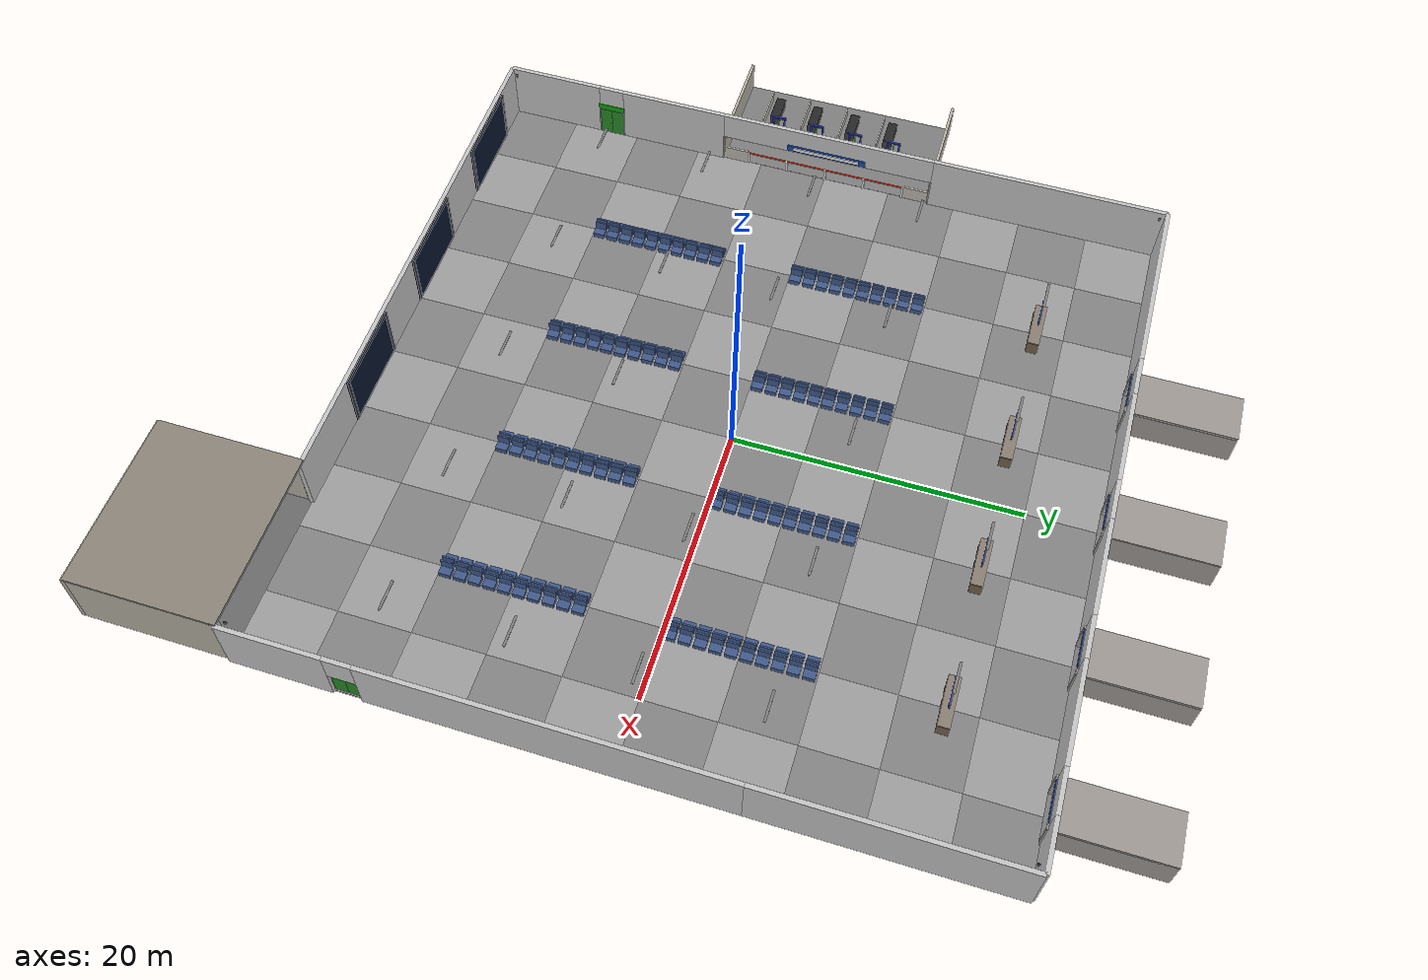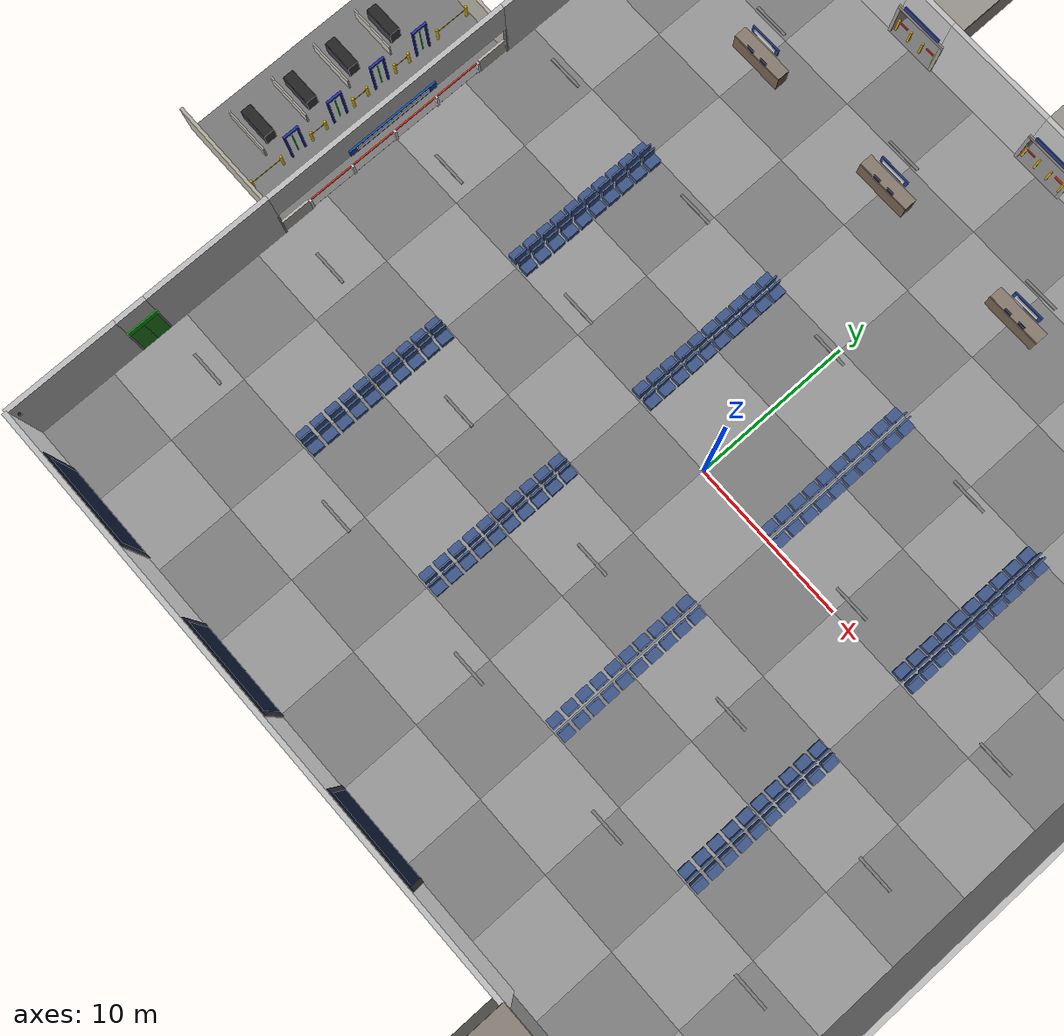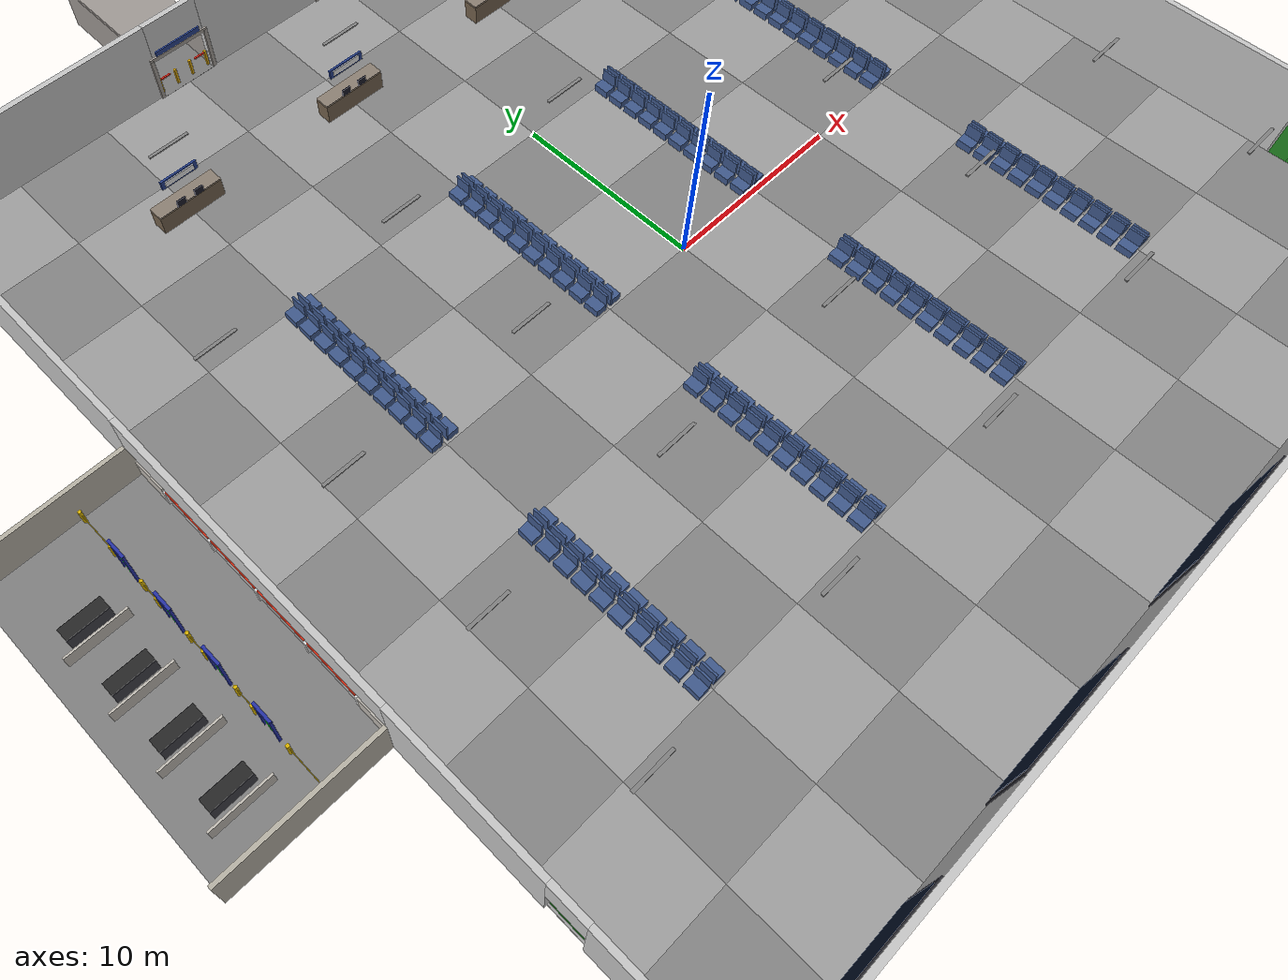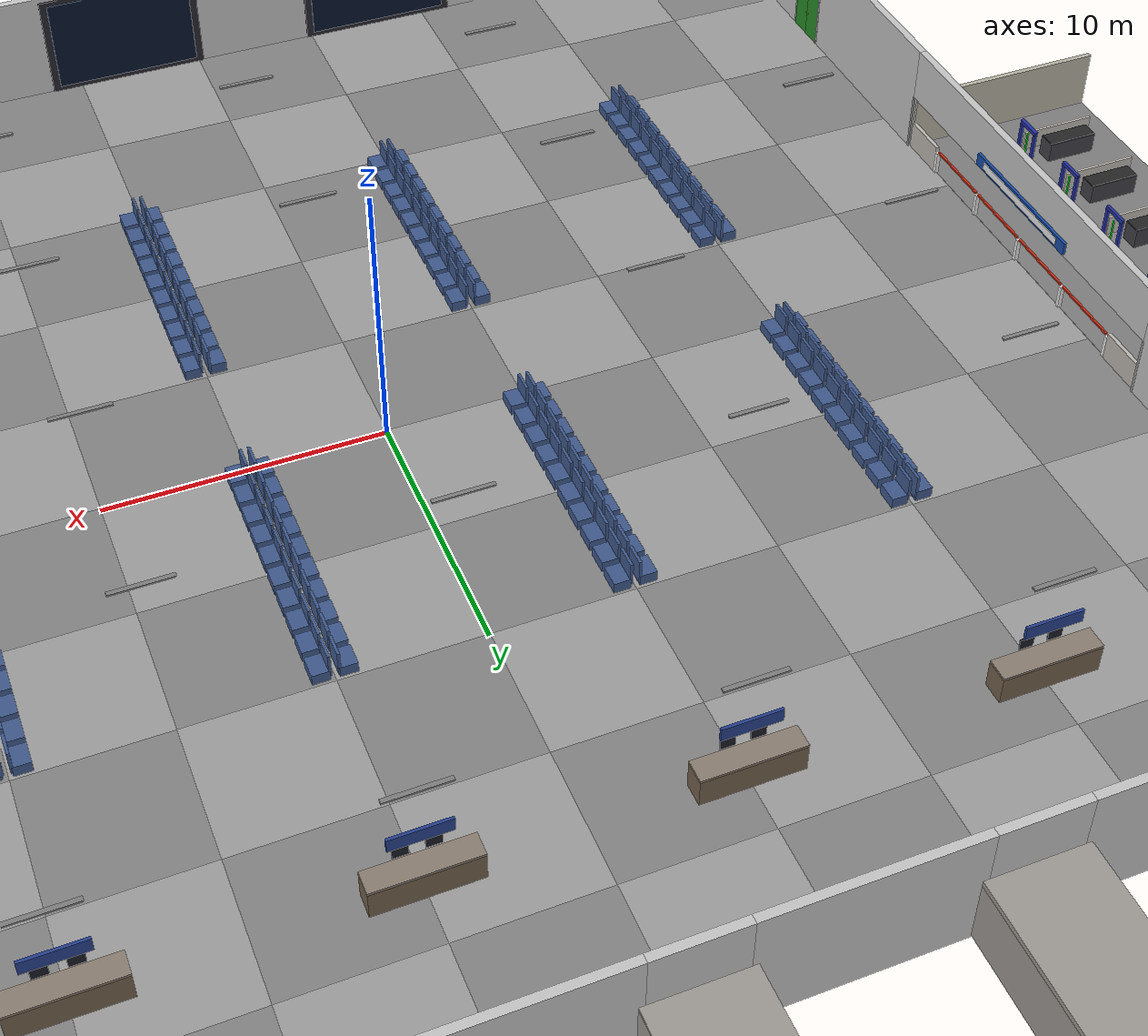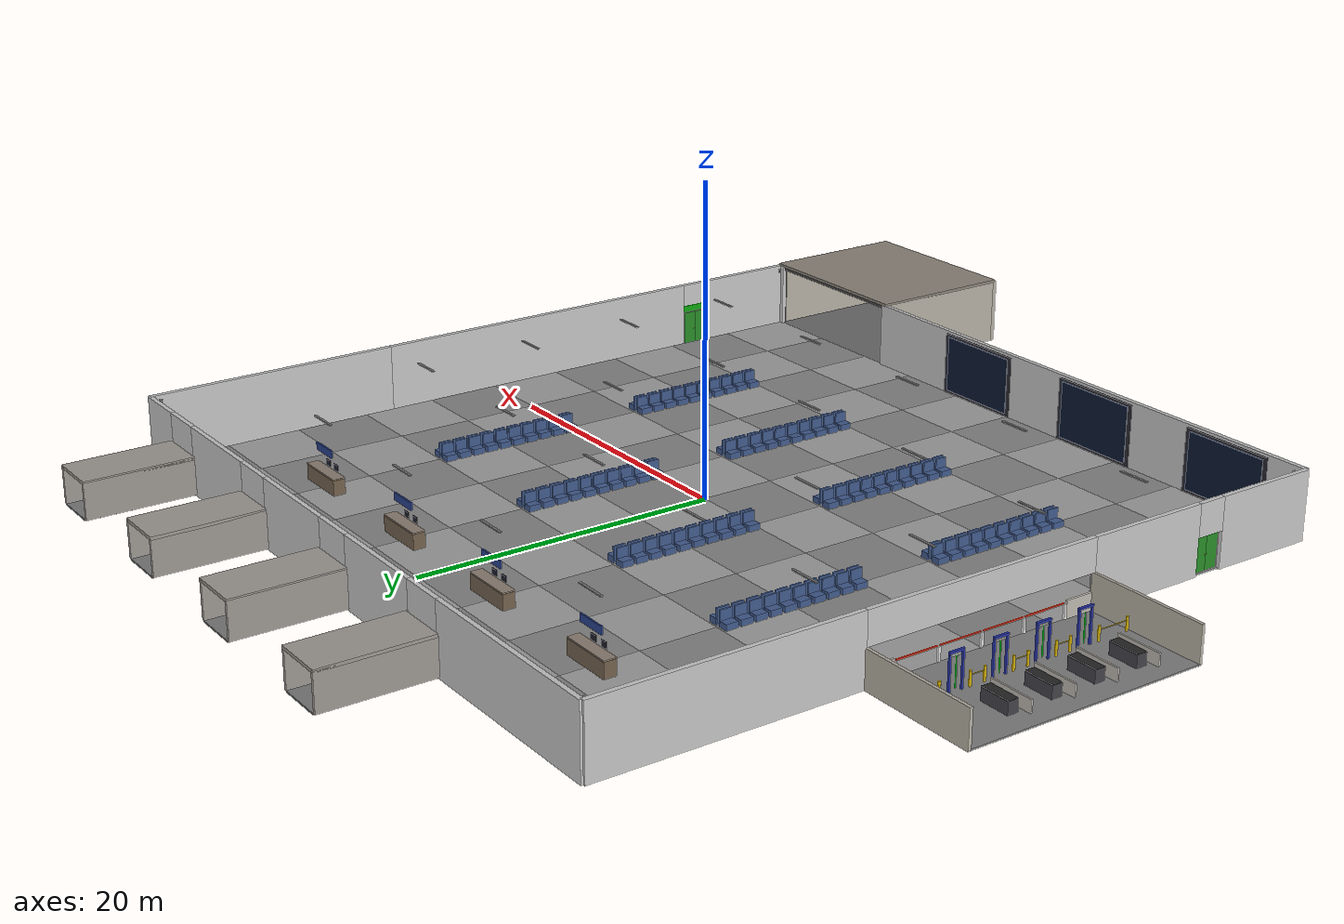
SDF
<?xml version="1.0" ?>
<sdf version="1.10">
  <world name="my_world">

  <!--  SYSTEM PLUGINS                                             -->
  <plugin filename="gz-sim-physics-system" name="gz::sim::systems::Physics"/>
  <plugin filename="gz-sim-scene-broadcaster-system" name="gz::sim::systems::SceneBroadcaster"/>
  <plugin filename="gz-sim-user-commands-system" name="gz::sim::systems::UserCommands"/>
  <plugin filename="gz-sim-contact-system" name="gz::sim::systems::Contact"/>
  <plugin filename="gz-sim-sensors-system" name="gz::sim::systems::Sensors">
     <render_engine>ogre2</render_engine>
  </plugin>

  <!--  PHYSICS                                                    -->
  <physics name="default_physics" type="ignored">
      <real_time_factor>1.0</real_time_factor>
      <real_time_update_rate>100</real_time_update_rate>
      <max_step_size>0.01</max_step_size>  <!-- explizit setzen -->
  </physics>

  <!--  SCENE & LIGHTING                                           -->
  <scene>
    <ambient>0.5 0.5 0.5 1</ambient>
    <background>0.53 0.81 0.98 1</background>
    <shadows>false</shadows>
  </scene>

  <light name="light_main" type="directional">
    <pose>0 0 10 0 0 0</pose>
    <cast_shadows>false</cast_shadows>
    <diffuse>0.6 0.6 0.6 1</diffuse>
    <specular>0.1 0.1 0.1 1</specular>
    <direction>0.1 0.1 -1</direction>
    <attenuation><range>1000</range><constant>1.0</constant><linear>0.0</linear><quadratic>0.0</quadratic></attenuation>
  </light>

  <!--  FLOOR					                   -->
  <model name="floor"><static>true</static><pose>0 0 0.05 0 0 0</pose>
    <link name="link">
      <collision name="col">
        <geometry><box><size>50 50 0.1</size></box></geometry>
        <surface>
          <friction><ode><mu>0.8</mu><mu2>0.8</mu2></ode></friction>
          <contact><ode>
            <kp>1000000.0</kp>
            <kd>1.0</kd>
            <max_vel>0.1</max_vel>
            <min_depth>0.001</min_depth>
          </ode></contact>
        </surface>
      </collision>
    </link>
  </model>

  <model name="vtile_0_0"><static>true</static><pose>-22.5 -22.5 0.05 0 0 0</pose>
    <link name="link">
      <visual name="vis"><geometry><box><size>5 5 0.1</size></box></geometry>
        <material><ambient>0.52 0.52 0.52 1</ambient><diffuse>0.52 0.52 0.52 1</diffuse></material></visual>
    </link></model>

  <model name="vtile_0_1"><static>true</static><pose>-22.5 -17.5 0.05 0 0 0</pose>
    <link name="link">
      <visual name="vis"><geometry><box><size>5 5 0.1</size></box></geometry>
        <material><ambient>0.62 0.62 0.62 1</ambient><diffuse>0.62 0.62 0.62 1</diffuse></material></visual>
    </link></model>

  <model name="vtile_0_2"><static>true</static><pose>-22.5 -12.5 0.05 0 0 0</pose>
    <link name="link">
      <visual name="vis"><geometry><box><size>5 5 0.1</size></box></geometry>
        <material><ambient>0.52 0.52 0.52 1</ambient><diffuse>0.52 0.52 0.52 1</diffuse></material></visual>
    </link></model>

  <model name="vtile_0_3"><static>true</static><pose>-22.5 -7.5 0.05 0 0 0</pose>
    <link name="link">
      <visual name="vis"><geometry><box><size>5 5 0.1</size></box></geometry>
        <material><ambient>0.62 0.62 0.62 1</ambient><diffuse>0.62 0.62 0.62 1</diffuse></material></visual>
    </link></model>

  <model name="vtile_0_4"><static>true</static><pose>-22.5 -2.5 0.05 0 0 0</pose>
    <link name="link">
      <visual name="vis"><geometry><box><size>5 5 0.1</size></box></geometry>
        <material><ambient>0.52 0.52 0.52 1</ambient><diffuse>0.52 0.52 0.52 1</diffuse></material></visual>
    </link></model>

  <model name="vtile_0_5"><static>true</static><pose>-22.5 2.5 0.05 0 0 0</pose>
    <link name="link">
      <visual name="vis"><geometry><box><size>5 5 0.1</size></box></geometry>
        <material><ambient>0.62 0.62 0.62 1</ambient><diffuse>0.62 0.62 0.62 1</diffuse></material></visual>
    </link></model>

  <model name="vtile_0_6"><static>true</static><pose>-22.5 7.5 0.05 0 0 0</pose>
    <link name="link">
      <visual name="vis"><geometry><box><size>5 5 0.1</size></box></geometry>
        <material><ambient>0.52 0.52 0.52 1</ambient><diffuse>0.52 0.52 0.52 1</diffuse></material></visual>
    </link></model>

  <model name="vtile_0_7"><static>true</static><pose>-22.5 12.5 0.05 0 0 0</pose>
    <link name="link">
      <visual name="vis"><geometry><box><size>5 5 0.1</size></box></geometry>
        <material><ambient>0.62 0.62 0.62 1</ambient><diffuse>0.62 0.62 0.62 1</diffuse></material></visual>
    </link></model>

  <model name="vtile_0_8"><static>true</static><pose>-22.5 17.5 0.05 0 0 0</pose>
    <link name="link">
      <visual name="vis"><geometry><box><size>5 5 0.1</size></box></geometry>
        <material><ambient>0.52 0.52 0.52 1</ambient><diffuse>0.52 0.52 0.52 1</diffuse></material></visual>
    </link></model>

  <model name="vtile_0_9"><static>true</static><pose>-22.5 22.5 0.05 0 0 0</pose>
    <link name="link">
      <visual name="vis"><geometry><box><size>5 5 0.1</size></box></geometry>
        <material><ambient>0.62 0.62 0.62 1</ambient><diffuse>0.62 0.62 0.62 1</diffuse></material></visual>
    </link></model>

  <model name="vtile_1_0"><static>true</static><pose>-17.5 -22.5 0.05 0 0 0</pose>
    <link name="link">
      <visual name="vis"><geometry><box><size>5 5 0.1</size></box></geometry>
        <material><ambient>0.62 0.62 0.62 1</ambient><diffuse>0.62 0.62 0.62 1</diffuse></material></visual>
    </link></model>

  <model name="vtile_1_1"><static>true</static><pose>-17.5 -17.5 0.05 0 0 0</pose>
    <link name="link">
      <visual name="vis"><geometry><box><size>5 5 0.1</size></box></geometry>
        <material><ambient>0.52 0.52 0.52 1</ambient><diffuse>0.52 0.52 0.52 1</diffuse></material></visual>
    </link></model>

  <model name="vtile_1_2"><static>true</static><pose>-17.5 -12.5 0.05 0 0 0</pose>
    <link name="link">
      <visual name="vis"><geometry><box><size>5 5 0.1</size></box></geometry>
        <material><ambient>0.62 0.62 0.62 1</ambient><diffuse>0.62 0.62 0.62 1</diffuse></material></visual>
    </link></model>

  <model name="vtile_1_3"><static>true</static><pose>-17.5 -7.5 0.05 0 0 0</pose>
    <link name="link">
      <visual name="vis"><geometry><box><size>5 5 0.1</size></box></geometry>
        <material><ambient>0.52 0.52 0.52 1</ambient><diffuse>0.52 0.52 0.52 1</diffuse></material></visual>
    </link></model>

  <model name="vtile_1_4"><static>true</static><pose>-17.5 -2.5 0.05 0 0 0</pose>
    <link name="link">
      <visual name="vis"><geometry><box><size>5 5 0.1</size></box></geometry>
        <material><ambient>0.62 0.62 0.62 1</ambient><diffuse>0.62 0.62 0.62 1</diffuse></material></visual>
    </link></model>

  <model name="vtile_1_5"><static>true</static><pose>-17.5 2.5 0.05 0 0 0</pose>
    <link name="link">
      <visual name="vis"><geometry><box><size>5 5 0.1</size></box></geometry>
        <material><ambient>0.52 0.52 0.52 1</ambient><diffuse>0.52 0.52 0.52 1</diffuse></material></visual>
    </link></model>

  <model name="vtile_1_6"><static>true</static><pose>-17.5 7.5 0.05 0 0 0</pose>
    <link name="link">
      <visual name="vis"><geometry><box><size>5 5 0.1</size></box></geometry>
        <material><ambient>0.62 0.62 0.62 1</ambient><diffuse>0.62 0.62 0.62 1</diffuse></material></visual>
    </link></model>

  <model name="vtile_1_7"><static>true</static><pose>-17.5 12.5 0.05 0 0 0</pose>
    <link name="link">
      <visual name="vis"><geometry><box><size>5 5 0.1</size></box></geometry>
        <material><ambient>0.52 0.52 0.52 1</ambient><diffuse>0.52 0.52 0.52 1</diffuse></material></visual>
    </link></model>

  <model name="vtile_1_8"><static>true</static><pose>-17.5 17.5 0.05 0 0 0</pose>
    <link name="link">
      <visual name="vis"><geometry><box><size>5 5 0.1</size></box></geometry>
        <material><ambient>0.62 0.62 0.62 1</ambient><diffuse>0.62 0.62 0.62 1</diffuse></material></visual>
    </link></model>

  <model name="vtile_1_9"><static>true</static><pose>-17.5 22.5 0.05 0 0 0</pose>
    <link name="link">
      <visual name="vis"><geometry><box><size>5 5 0.1</size></box></geometry>
        <material><ambient>0.52 0.52 0.52 1</ambient><diffuse>0.52 0.52 0.52 1</diffuse></material></visual>
    </link></model>

  <model name="vtile_2_0"><static>true</static><pose>-12.5 -22.5 0.05 0 0 0</pose>
    <link name="link">
      <visual name="vis"><geometry><box><size>5 5 0.1</size></box></geometry>
        <material><ambient>0.52 0.52 0.52 1</ambient><diffuse>0.52 0.52 0.52 1</diffuse></material></visual>
    </link></model>

  <model name="vtile_2_1"><static>true</static><pose>-12.5 -17.5 0.05 0 0 0</pose>
    <link name="link">
      <visual name="vis"><geometry><box><size>5 5 0.1</size></box></geometry>
        <material><ambient>0.62 0.62 0.62 1</ambient><diffuse>0.62 0.62 0.62 1</diffuse></material></visual>
    </link></model>

  <model name="vtile_2_2"><static>true</static><pose>-12.5 -12.5 0.05 0 0 0</pose>
    <link name="link">
      <visual name="vis"><geometry><box><size>5 5 0.1</size></box></geometry>
        <material><ambient>0.52 0.52 0.52 1</ambient><diffuse>0.52 0.52 0.52 1</diffuse></material></visual>
    </link></model>

  <model name="vtile_2_3"><static>true</static><pose>-12.5 -7.5 0.05 0 0 0</pose>
    <link name="link">
      <visual name="vis"><geometry><box><size>5 5 0.1</size></box></geometry>
        <material><ambient>0.62 0.62 0.62 1</ambient><diffuse>0.62 0.62 0.62 1</diffuse></material></visual>
    </link></model>

  <model name="vtile_2_4"><static>true</static><pose>-12.5 -2.5 0.05 0 0 0</pose>
    <link name="link">
      <visual name="vis"><geometry><box><size>5 5 0.1</size></box></geometry>
        <material><ambient>0.52 0.52 0.52 1</ambient><diffuse>0.52 0.52 0.52 1</diffuse></material></visual>
    </link></model>

  <model name="vtile_2_5"><static>true</static><pose>-12.5 2.5 0.05 0 0 0</pose>
    <link name="link">
      <visual name="vis"><geometry><box><size>5 5 0.1</size></box></geometry>
        <material><ambient>0.62 0.62 0.62 1</ambient><diffuse>0.62 0.62 0.62 1</diffuse></material></visual>
    </link></model>

  <model name="vtile_2_6"><static>true</static><pose>-12.5 7.5 0.05 0 0 0</pose>
    <link name="link">
      <visual name="vis"><geometry><box><size>5 5 0.1</size></box></geometry>
        <material><ambient>0.52 0.52 0.52 1</ambient><diffuse>0.52 0.52 0.52 1</diffuse></material></visual>
    </link></model>

  <model name="vtile_2_7"><static>true</static><pose>-12.5 12.5 0.05 0 0 0</pose>
    <link name="link">
      <visual name="vis"><geometry><box><size>5 5 0.1</size></box></geometry>
        <material><ambient>0.62 0.62 0.62 1</ambient><diffuse>0.62 0.62 0.62 1</diffuse></material></visual>
    </link></model>

  <model name="vtile_2_8"><static>true</static><pose>-12.5 17.5 0.05 0 0 0</pose>
    <link name="link">
      <visual name="vis"><geometry><box><size>5 5 0.1</size></box></geometry>
        <material><ambient>0.52 0.52 0.52 1</ambient><diffuse>0.52 0.52 0.52 1</diffuse></material></visual>
    </link></model>

  <model name="vtile_2_9"><static>true</static><pose>-12.5 22.5 0.05 0 0 0</pose>
    <link name="link">
      <visual name="vis"><geometry><box><size>5 5 0.1</size></box></geometry>
        <material><ambient>0.62 0.62 0.62 1</ambient><diffuse>0.62 0.62 0.62 1</diffuse></material></visual>
    </link></model>

  <model name="vtile_3_0"><static>true</static><pose>-7.5 -22.5 0.05 0 0 0</pose>
    <link name="link">
      <visual name="vis"><geometry><box><size>5 5 0.1</size></box></geometry>
        <material><ambient>0.62 0.62 0.62 1</ambient><diffuse>0.62 0.62 0.62 1</diffuse></material></visual>
    </link></model>

  <model name="vtile_3_1"><static>true</static><pose>-7.5 -17.5 0.05 0 0 0</pose>
    <link name="link">
      <visual name="vis"><geometry><box><size>5 5 0.1</size></box></geometry>
        <material><ambient>0.52 0.52 0.52 1</ambient><diffuse>0.52 0.52 0.52 1</diffuse></material></visual>
    </link></model>

  <model name="vtile_3_2"><static>true</static><pose>-7.5 -12.5 0.05 0 0 0</pose>
    <link name="link">
      <visual name="vis"><geometry><box><size>5 5 0.1</size></box></geometry>
        <material><ambient>0.62 0.62 0.62 1</ambient><diffuse>0.62 0.62 0.62 1</diffuse></material></visual>
    </link></model>

  <model name="vtile_3_3"><static>true</static><pose>-7.5 -7.5 0.05 0 0 0</pose>
    <link name="link">
      <visual name="vis"><geometry><box><size>5 5 0.1</size></box></geometry>
        <material><ambient>0.52 0.52 0.52 1</ambient><diffuse>0.52 0.52 0.52 1</diffuse></material></visual>
    </link></model>

  <model name="vtile_3_4"><static>true</static><pose>-7.5 -2.5 0.05 0 0 0</pose>
    <link name="link">
      <visual name="vis"><geometry><box><size>5 5 0.1</size></box></geometry>
        <material><ambient>0.62 0.62 0.62 1</ambient><diffuse>0.62 0.62 0.62 1</diffuse></material></visual>
    </link></model>

  <model name="vtile_3_5"><static>true</static><pose>-7.5 2.5 0.05 0 0 0</pose>
    <link name="link">
      <visual name="vis"><geometry><box><size>5 5 0.1</size></box></geometry>
        <material><ambient>0.52 0.52 0.52 1</ambient><diffuse>0.52 0.52 0.52 1</diffuse></material></visual>
    </link></model>

  <model name="vtile_3_6"><static>true</static><pose>-7.5 7.5 0.05 0 0 0</pose>
    <link name="link">
      <visual name="vis"><geometry><box><size>5 5 0.1</size></box></geometry>
        <material><ambient>0.62 0.62 0.62 1</ambient><diffuse>0.62 0.62 0.62 1</diffuse></material></visual>
    </link></model>

  <model name="vtile_3_7"><static>true</static><pose>-7.5 12.5 0.05 0 0 0</pose>
    <link name="link">
      <visual name="vis"><geometry><box><size>5 5 0.1</size></box></geometry>
        <material><ambient>0.52 0.52 0.52 1</ambient><diffuse>0.52 0.52 0.52 1</diffuse></material></visual>
    </link></model>

  <model name="vtile_3_8"><static>true</static><pose>-7.5 17.5 0.05 0 0 0</pose>
    <link name="link">
      <visual name="vis"><geometry><box><size>5 5 0.1</size></box></geometry>
        <material><ambient>0.62 0.62 0.62 1</ambient><diffuse>0.62 0.62 0.62 1</diffuse></material></visual>
    </link></model>

  <model name="vtile_3_9"><static>true</static><pose>-7.5 22.5 0.05 0 0 0</pose>
    <link name="link">
      <visual name="vis"><geometry><box><size>5 5 0.1</size></box></geometry>
        <material><ambient>0.52 0.52 0.52 1</ambient><diffuse>0.52 0.52 0.52 1</diffuse></material></visual>
    </link></model>

  <model name="vtile_4_0"><static>true</static><pose>-2.5 -22.5 0.05 0 0 0</pose>
    <link name="link">
      <visual name="vis"><geometry><box><size>5 5 0.1</size></box></geometry>
        <material><ambient>0.52 0.52 0.52 1</ambient><diffuse>0.52 0.52 0.52 1</diffuse></material></visual>
    </link></model>

  <model name="vtile_4_1"><static>true</static><pose>-2.5 -17.5 0.05 0 0 0</pose>
    <link name="link">
      <visual name="vis"><geometry><box><size>5 5 0.1</size></box></geometry>
        <material><ambient>0.62 0.62 0.62 1</ambient><diffuse>0.62 0.62 0.62 1</diffuse></material></visual>
    </link></model>

  <model name="vtile_4_2"><static>true</static><pose>-2.5 -12.5 0.05 0 0 0</pose>
    <link name="link">
      <visual name="vis"><geometry><box><size>5 5 0.1</size></box></geometry>
        <material><ambient>0.52 0.52 0.52 1</ambient><diffuse>0.52 0.52 0.52 1</diffuse></material></visual>
    </link></model>

  <model name="vtile_4_3"><static>true</static><pose>-2.5 -7.5 0.05 0 0 0</pose>
    <link name="link">
      <visual name="vis"><geometry><box><size>5 5 0.1</size></box></geometry>
        <material><ambient>0.62 0.62 0.62 1</ambient><diffuse>0.62 0.62 0.62 1</diffuse></material></visual>
    </link></model>

  <model name="vtile_4_4"><static>true</static><pose>-2.5 -2.5 0.05 0 0 0</pose>
    <link name="link">
      <visual name="vis"><geometry><box><size>5 5 0.1</size></box></geometry>
        <material><ambient>0.52 0.52 0.52 1</ambient><diffuse>0.52 0.52 0.52 1</diffuse></material></visual>
    </link></model>

  <model name="vtile_4_5"><static>true</static><pose>-2.5 2.5 0.05 0 0 0</pose>
    <link name="link">
      <visual name="vis"><geometry><box><size>5 5 0.1</size></box></geometry>
        <material><ambient>0.62 0.62 0.62 1</ambient><diffuse>0.62 0.62 0.62 1</diffuse></material></visual>
    </link></model>

  <model name="vtile_4_6"><static>true</static><pose>-2.5 7.5 0.05 0 0 0</pose>
    <link name="link">
      <visual name="vis"><geometry><box><size>5 5 0.1</size></box></geometry>
        <material><ambient>0.52 0.52 0.52 1</ambient><diffuse>0.52 0.52 0.52 1</diffuse></material></visual>
    </link></model>

  <model name="vtile_4_7"><static>true</static><pose>-2.5 12.5 0.05 0 0 0</pose>
    <link name="link">
      <visual name="vis"><geometry><box><size>5 5 0.1</size></box></geometry>
        <material><ambient>0.62 0.62 0.62 1</ambient><diffuse>0.62 0.62 0.62 1</diffuse></material></visual>
    </link></model>

  <model name="vtile_4_8"><static>true</static><pose>-2.5 17.5 0.05 0 0 0</pose>
    <link name="link">
      <visual name="vis"><geometry><box><size>5 5 0.1</size></box></geometry>
        <material><ambient>0.52 0.52 0.52 1</ambient><diffuse>0.52 0.52 0.52 1</diffuse></material></visual>
    </link></model>

  <model name="vtile_4_9"><static>true</static><pose>-2.5 22.5 0.05 0 0 0</pose>
    <link name="link">
      <visual name="vis"><geometry><box><size>5 5 0.1</size></box></geometry>
        <material><ambient>0.62 0.62 0.62 1</ambient><diffuse>0.62 0.62 0.62 1</diffuse></material></visual>
    </link></model>

  <model name="vtile_5_0"><static>true</static><pose>2.5 -22.5 0.05 0 0 0</pose>
    <link name="link">
      <visual name="vis"><geometry><box><size>5 5 0.1</size></box></geometry>
        <material><ambient>0.62 0.62 0.62 1</ambient><diffuse>0.62 0.62 0.62 1</diffuse></material></visual>
    </link></model>

  <model name="vtile_5_1"><static>true</static><pose>2.5 -17.5 0.05 0 0 0</pose>
    <link name="link">
      <visual name="vis"><geometry><box><size>5 5 0.1</size></box></geometry>
        <material><ambient>0.52 0.52 0.52 1</ambient><diffuse>0.52 0.52 0.52 1</diffuse></material></visual>
    </link></model>

  <model name="vtile_5_2"><static>true</static><pose>2.5 -12.5 0.05 0 0 0</pose>
    <link name="link">
      <visual name="vis"><geometry><box><size>5 5 0.1</size></box></geometry>
        <material><ambient>0.62 0.62 0.62 1</ambient><diffuse>0.62 0.62 0.62 1</diffuse></material></visual>
    </link></model>

  <model name="vtile_5_3"><static>true</static><pose>2.5 -7.5 0.05 0 0 0</pose>
    <link name="link">
      <visual name="vis"><geometry><box><size>5 5 0.1</size></box></geometry>
        <material><ambient>0.52 0.52 0.52 1</ambient><diffuse>0.52 0.52 0.52 1</diffuse></material></visual>
    </link></model>

  <model name="vtile_5_4"><static>true</static><pose>2.5 -2.5 0.05 0 0 0</pose>
    <link name="link">
      <visual name="vis"><geometry><box><size>5 5 0.1</size></box></geometry>
        <material><ambient>0.62 0.62 0.62 1</ambient><diffuse>0.62 0.62 0.62 1</diffuse></material></visual>
    </link></model>

  <model name="vtile_5_5"><static>true</static><pose>2.5 2.5 0.05 0 0 0</pose>
    <link name="link">
      <visual name="vis"><geometry><box><size>5 5 0.1</size></box></geometry>
        <material><ambient>0.52 0.52 0.52 1</ambient><diffuse>0.52 0.52 0.52 1</diffuse></material></visual>
    </link></model>

  <model name="vtile_5_6"><static>true</static><pose>2.5 7.5 0.05 0 0 0</pose>
    <link name="link">
      <visual name="vis"><geometry><box><size>5 5 0.1</size></box></geometry>
        <material><ambient>0.62 0.62 0.62 1</ambient><diffuse>0.62 0.62 0.62 1</diffuse></material></visual>
    </link></model>

  <model name="vtile_5_7"><static>true</static><pose>2.5 12.5 0.05 0 0 0</pose>
    <link name="link">
      <visual name="vis"><geometry><box><size>5 5 0.1</size></box></geometry>
        <material><ambient>0.52 0.52 0.52 1</ambient><diffuse>0.52 0.52 0.52 1</diffuse></material></visual>
    </link></model>

  <model name="vtile_5_8"><static>true</static><pose>2.5 17.5 0.05 0 0 0</pose>
    <link name="link">
      <visual name="vis"><geometry><box><size>5 5 0.1</size></box></geometry>
        <material><ambient>0.62 0.62 0.62 1</ambient><diffuse>0.62 0.62 0.62 1</diffuse></material></visual>
    </link></model>

  <model name="vtile_5_9"><static>true</static><pose>2.5 22.5 0.05 0 0 0</pose>
    <link name="link">
      <visual name="vis"><geometry><box><size>5 5 0.1</size></box></geometry>
        <material><ambient>0.52 0.52 0.52 1</ambient><diffuse>0.52 0.52 0.52 1</diffuse></material></visual>
    </link></model>

  <model name="vtile_6_0"><static>true</static><pose>7.5 -22.5 0.05 0 0 0</pose>
    <link name="link">
      <visual name="vis"><geometry><box><size>5 5 0.1</size></box></geometry>
        <material><ambient>0.52 0.52 0.52 1</ambient><diffuse>0.52 0.52 0.52 1</diffuse></material></visual>
    </link></model>

  <model name="vtile_6_1"><static>true</static><pose>7.5 -17.5 0.05 0 0 0</pose>
    <link name="link">
      <visual name="vis"><geometry><box><size>5 5 0.1</size></box></geometry>
        <material><ambient>0.62 0.62 0.62 1</ambient><diffuse>0.62 0.62 0.62 1</diffuse></material></visual>
    </link></model>

  <model name="vtile_6_2"><static>true</static><pose>7.5 -12.5 0.05 0 0 0</pose>
    <link name="link">
      <visual name="vis"><geometry><box><size>5 5 0.1</size></box></geometry>
        <material><ambient>0.52 0.52 0.52 1</ambient><diffuse>0.52 0.52 0.52 1</diffuse></material></visual>
    </link></model>

  <model name="vtile_6_3"><static>true</static><pose>7.5 -7.5 0.05 0 0 0</pose>
    <link name="link">
      <visual name="vis"><geometry><box><size>5 5 0.1</size></box></geometry>
        <material><ambient>0.62 0.62 0.62 1</ambient><diffuse>0.62 0.62 0.62 1</diffuse></material></visual>
    </link></model>

  <model name="vtile_6_4"><static>true</static><pose>7.5 -2.5 0.05 0 0 0</pose>
    <link name="link">
      <visual name="vis"><geometry><box><size>5 5 0.1</size></box></geometry>
        <material><ambient>0.52 0.52 0.52 1</ambient><diffuse>0.52 0.52 0.52 1</diffuse></material></visual>
    </link></model>

  <model name="vtile_6_5"><static>true</static><pose>7.5 2.5 0.05 0 0 0</pose>
    <link name="link">
      <visual name="vis"><geometry><box><size>5 5 0.1</size></box></geometry>
        <material><ambient>0.62 0.62 0.62 1</ambient><diffuse>0.62 0.62 0.62 1</diffuse></material></visual>
    </link></model>

  <model name="vtile_6_6"><static>true</static><pose>7.5 7.5 0.05 0 0 0</pose>
    <link name="link">
      <visual name="vis"><geometry><box><size>5 5 0.1</size></box></geometry>
        <material><ambient>0.52 0.52 0.52 1</ambient><diffuse>0.52 0.52 0.52 1</diffuse></material></visual>
    </link></model>

  <model name="vtile_6_7"><static>true</static><pose>7.5 12.5 0.05 0 0 0</pose>
    <link name="link">
      <visual name="vis"><geometry><box><size>5 5 0.1</size></box></geometry>
        <material><ambient>0.62 0.62 0.62 1</ambient><diffuse>0.62 0.62 0.62 1</diffuse></material></visual>
    </link></model>

  <model name="vtile_6_8"><static>true</static><pose>7.5 17.5 0.05 0 0 0</pose>
    <link name="link">
      <visual name="vis"><geometry><box><size>5 5 0.1</size></box></geometry>
        <material><ambient>0.52 0.52 0.52 1</ambient><diffuse>0.52 0.52 0.52 1</diffuse></material></visual>
    </link></model>

  <model name="vtile_6_9"><static>true</static><pose>7.5 22.5 0.05 0 0 0</pose>
    <link name="link">
      <visual name="vis"><geometry><box><size>5 5 0.1</size></box></geometry>
        <material><ambient>0.62 0.62 0.62 1</ambient><diffuse>0.62 0.62 0.62 1</diffuse></material></visual>
    </link></model>

  <model name="vtile_7_0"><static>true</static><pose>12.5 -22.5 0.05 0 0 0</pose>
    <link name="link">
      <visual name="vis"><geometry><box><size>5 5 0.1</size></box></geometry>
        <material><ambient>0.62 0.62 0.62 1</ambient><diffuse>0.62 0.62 0.62 1</diffuse></material></visual>
    </link></model>

  <model name="vtile_7_1"><static>true</static><pose>12.5 -17.5 0.05 0 0 0</pose>
    <link name="link">
      <visual name="vis"><geometry><box><size>5 5 0.1</size></box></geometry>
        <material><ambient>0.52 0.52 0.52 1</ambient><diffuse>0.52 0.52 0.52 1</diffuse></material></visual>
    </link></model>

  <model name="vtile_7_2"><static>true</static><pose>12.5 -12.5 0.05 0 0 0</pose>
    <link name="link">
      <visual name="vis"><geometry><box><size>5 5 0.1</size></box></geometry>
        <material><ambient>0.62 0.62 0.62 1</ambient><diffuse>0.62 0.62 0.62 1</diffuse></material></visual>
    </link></model>

  <model name="vtile_7_3"><static>true</static><pose>12.5 -7.5 0.05 0 0 0</pose>
    <link name="link">
      <visual name="vis"><geometry><box><size>5 5 0.1</size></box></geometry>
        <material><ambient>0.52 0.52 0.52 1</ambient><diffuse>0.52 0.52 0.52 1</diffuse></material></visual>
    </link></model>

  <model name="vtile_7_4"><static>true</static><pose>12.5 -2.5 0.05 0 0 0</pose>
    <link name="link">
      <visual name="vis"><geometry><box><size>5 5 0.1</size></box></geometry>
        <material><ambient>0.62 0.62 0.62 1</ambient><diffuse>0.62 0.62 0.62 1</diffuse></material></visual>
    </link></model>

  <model name="vtile_7_5"><static>true</static><pose>12.5 2.5 0.05 0 0 0</pose>
    <link name="link">
      <visual name="vis"><geometry><box><size>5 5 0.1</size></box></geometry>
        <material><ambient>0.52 0.52 0.52 1</ambient><diffuse>0.52 0.52 0.52 1</diffuse></material></visual>
    </link></model>

  <model name="vtile_7_6"><static>true</static><pose>12.5 7.5 0.05 0 0 0</pose>
    <link name="link">
      <visual name="vis"><geometry><box><size>5 5 0.1</size></box></geometry>
        <material><ambient>0.62 0.62 0.62 1</ambient><diffuse>0.62 0.62 0.62 1</diffuse></material></visual>
    </link></model>

  <model name="vtile_7_7"><static>true</static><pose>12.5 12.5 0.05 0 0 0</pose>
    <link name="link">
      <visual name="vis"><geometry><box><size>5 5 0.1</size></box></geometry>
        <material><ambient>0.52 0.52 0.52 1</ambient><diffuse>0.52 0.52 0.52 1</diffuse></material></visual>
    </link></model>

  <model name="vtile_7_8"><static>true</static><pose>12.5 17.5 0.05 0 0 0</pose>
    <link name="link">
      <visual name="vis"><geometry><box><size>5 5 0.1</size></box></geometry>
        <material><ambient>0.62 0.62 0.62 1</ambient><diffuse>0.62 0.62 0.62 1</diffuse></material></visual>
    </link></model>

  <model name="vtile_7_9"><static>true</static><pose>12.5 22.5 0.05 0 0 0</pose>
    <link name="link">
      <visual name="vis"><geometry><box><size>5 5 0.1</size></box></geometry>
        <material><ambient>0.52 0.52 0.52 1</ambient><diffuse>0.52 0.52 0.52 1</diffuse></material></visual>
    </link></model>

  <model name="vtile_8_0"><static>true</static><pose>17.5 -22.5 0.05 0 0 0</pose>
    <link name="link">
      <visual name="vis"><geometry><box><size>5 5 0.1</size></box></geometry>
        <material><ambient>0.52 0.52 0.52 1</ambient><diffuse>0.52 0.52 0.52 1</diffuse></material></visual>
    </link></model>

  <model name="vtile_8_1"><static>true</static><pose>17.5 -17.5 0.05 0 0 0</pose>
    <link name="link">
      <visual name="vis"><geometry><box><size>5 5 0.1</size></box></geometry>
        <material><ambient>0.62 0.62 0.62 1</ambient><diffuse>0.62 0.62 0.62 1</diffuse></material></visual>
    </link></model>

  <model name="vtile_8_2"><static>true</static><pose>17.5 -12.5 0.05 0 0 0</pose>
    <link name="link">
      <visual name="vis"><geometry><box><size>5 5 0.1</size></box></geometry>
        <material><ambient>0.52 0.52 0.52 1</ambient><diffuse>0.52 0.52 0.52 1</diffuse></material></visual>
    </link></model>

  <model name="vtile_8_3"><static>true</static><pose>17.5 -7.5 0.05 0 0 0</pose>
    <link name="link">
      <visual name="vis"><geometry><box><size>5 5 0.1</size></box></geometry>
        <material><ambient>0.62 0.62 0.62 1</ambient><diffuse>0.62 0.62 0.62 1</diffuse></material></visual>
    </link></model>

  <model name="vtile_8_4"><static>true</static><pose>17.5 -2.5 0.05 0 0 0</pose>
    <link name="link">
      <visual name="vis"><geometry><box><size>5 5 0.1</size></box></geometry>
        <material><ambient>0.52 0.52 0.52 1</ambient><diffuse>0.52 0.52 0.52 1</diffuse></material></visual>
    </link></model>

  <model name="vtile_8_5"><static>true</static><pose>17.5 2.5 0.05 0 0 0</pose>
    <link name="link">
      <visual name="vis"><geometry><box><size>5 5 0.1</size></box></geometry>
        <material><ambient>0.62 0.62 0.62 1</ambient><diffuse>0.62 0.62 0.62 1</diffuse></material></visual>
    </link></model>

  <model name="vtile_8_6"><static>true</static><pose>17.5 7.5 0.05 0 0 0</pose>
    <link name="link">
      <visual name="vis"><geometry><box><size>5 5 0.1</size></box></geometry>
        <material><ambient>0.52 0.52 0.52 1</ambient><diffuse>0.52 0.52 0.52 1</diffuse></material></visual>
    </link></model>

  <model name="vtile_8_7"><static>true</static><pose>17.5 12.5 0.05 0 0 0</pose>
    <link name="link">
      <visual name="vis"><geometry><box><size>5 5 0.1</size></box></geometry>
        <material><ambient>0.62 0.62 0.62 1</ambient><diffuse>0.62 0.62 0.62 1</diffuse></material></visual>
    </link></model>

  <model name="vtile_8_8"><static>true</static><pose>17.5 17.5 0.05 0 0 0</pose>
    <link name="link">
      <visual name="vis"><geometry><box><size>5 5 0.1</size></box></geometry>
        <material><ambient>0.52 0.52 0.52 1</ambient><diffuse>0.52 0.52 0.52 1</diffuse></material></visual>
    </link></model>

  <model name="vtile_8_9"><static>true</static><pose>17.5 22.5 0.05 0 0 0</pose>
    <link name="link">
      <visual name="vis"><geometry><box><size>5 5 0.1</size></box></geometry>
        <material><ambient>0.62 0.62 0.62 1</ambient><diffuse>0.62 0.62 0.62 1</diffuse></material></visual>
    </link></model>

  <model name="vtile_9_0"><static>true</static><pose>22.5 -22.5 0.05 0 0 0</pose>
    <link name="link">
      <visual name="vis"><geometry><box><size>5 5 0.1</size></box></geometry>
        <material><ambient>0.62 0.62 0.62 1</ambient><diffuse>0.62 0.62 0.62 1</diffuse></material></visual>
    </link></model>

  <model name="vtile_9_1"><static>true</static><pose>22.5 -17.5 0.05 0 0 0</pose>
    <link name="link">
      <visual name="vis"><geometry><box><size>5 5 0.1</size></box></geometry>
        <material><ambient>0.52 0.52 0.52 1</ambient><diffuse>0.52 0.52 0.52 1</diffuse></material></visual>
    </link></model>

  <model name="vtile_9_2"><static>true</static><pose>22.5 -12.5 0.05 0 0 0</pose>
    <link name="link">
      <visual name="vis"><geometry><box><size>5 5 0.1</size></box></geometry>
        <material><ambient>0.62 0.62 0.62 1</ambient><diffuse>0.62 0.62 0.62 1</diffuse></material></visual>
    </link></model>

  <model name="vtile_9_3"><static>true</static><pose>22.5 -7.5 0.05 0 0 0</pose>
    <link name="link">
      <visual name="vis"><geometry><box><size>5 5 0.1</size></box></geometry>
        <material><ambient>0.52 0.52 0.52 1</ambient><diffuse>0.52 0.52 0.52 1</diffuse></material></visual>
    </link></model>

  <model name="vtile_9_4"><static>true</static><pose>22.5 -2.5 0.05 0 0 0</pose>
    <link name="link">
      <visual name="vis"><geometry><box><size>5 5 0.1</size></box></geometry>
        <material><ambient>0.62 0.62 0.62 1</ambient><diffuse>0.62 0.62 0.62 1</diffuse></material></visual>
    </link></model>

  <model name="vtile_9_5"><static>true</static><pose>22.5 2.5 0.05 0 0 0</pose>
    <link name="link">
      <visual name="vis"><geometry><box><size>5 5 0.1</size></box></geometry>
        <material><ambient>0.52 0.52 0.52 1</ambient><diffuse>0.52 0.52 0.52 1</diffuse></material></visual>
    </link></model>

  <model name="vtile_9_6"><static>true</static><pose>22.5 7.5 0.05 0 0 0</pose>
    <link name="link">
      <visual name="vis"><geometry><box><size>5 5 0.1</size></box></geometry>
        <material><ambient>0.62 0.62 0.62 1</ambient><diffuse>0.62 0.62 0.62 1</diffuse></material></visual>
    </link></model>

  <model name="vtile_9_7"><static>true</static><pose>22.5 12.5 0.05 0 0 0</pose>
    <link name="link">
      <visual name="vis"><geometry><box><size>5 5 0.1</size></box></geometry>
        <material><ambient>0.52 0.52 0.52 1</ambient><diffuse>0.52 0.52 0.52 1</diffuse></material></visual>
    </link></model>

  <model name="vtile_9_8"><static>true</static><pose>22.5 17.5 0.05 0 0 0</pose>
    <link name="link">
      <visual name="vis"><geometry><box><size>5 5 0.1</size></box></geometry>
        <material><ambient>0.62 0.62 0.62 1</ambient><diffuse>0.62 0.62 0.62 1</diffuse></material></visual>
    </link></model>

  <model name="vtile_9_9"><static>true</static><pose>22.5 22.5 0.05 0 0 0</pose>
    <link name="link">
      <visual name="vis"><geometry><box><size>5 5 0.1</size></box></geometry>
        <material><ambient>0.52 0.52 0.52 1</ambient><diffuse>0.52 0.52 0.52 1</diffuse></material></visual>
    </link></model>

  <!--  WALLS                                                      -->
  <model name="wall_north_1"><static>true</static><pose>-18.25 25 2.25 0 0 0</pose>
    <link name="link">
      <collision name="col"><geometry><box><size>13.5 0.3 4.5</size></box></geometry></collision>
      <visual name="vis"><geometry><box><size>13.5 0.3 4.5</size></box></geometry>
        <material><ambient>0.78 0.78 0.78 1</ambient><diffuse>0.78 0.78 0.78 1</diffuse></material></visual>
    </link></model>

    <model name="wall_north_2"><static>true</static><pose>-5.0 25 2.25 0 0 0</pose>
      <link name="link">
        <collision name="col"><geometry><box><size>7.0 0.3 4.5</size></box></geometry></collision>
        <visual name="vis"><geometry><box><size>7.0 0.3 4.5</size></box></geometry>
          <material><ambient>0.78 0.78 0.78 1</ambient><diffuse>0.78 0.78 0.78 1</diffuse></material></visual>
      </link></model>

    <model name="wall_north_3"><static>true</static><pose>5.0 25 2.25 0 0 0</pose>
      <link name="link">
        <collision name="col"><geometry><box><size>7.0 0.3 4.5</size></box></geometry></collision>
        <visual name="vis"><geometry><box><size>7.0 0.3 4.5</size></box></geometry>
          <material><ambient>0.78 0.78 0.78 1</ambient><diffuse>0.78 0.78 0.78 1</diffuse></material></visual>
      </link></model>

    <model name="wall_north_4"><static>true</static><pose>15.0 25 2.25 0 0 0</pose>
      <link name="link">
        <collision name="col"><geometry><box><size>7.0 0.3 4.5</size></box></geometry></collision>
        <visual name="vis"><geometry><box><size>7.0 0.3 4.5</size></box></geometry>
          <material><ambient>0.78 0.78 0.78 1</ambient><diffuse>0.78 0.78 0.78 1</diffuse></material></visual>
      </link></model>

    <model name="wall_north_5"><static>true</static><pose>23.25 25 2.25 0 0 0</pose>
      <link name="link">
        <collision name="col"><geometry><box><size>3.5 0.3 4.5</size></box></geometry></collision>
        <visual name="vis"><geometry><box><size>3.5 0.3 4.5</size></box></geometry>
          <material><ambient>0.78 0.78 0.78 1</ambient><diffuse>0.78 0.78 0.78 1</diffuse></material></visual>
      </link></model>

    <model name="wall_north_top_-10"><static>true</static><pose>-10 25 3.5 0 0 0</pose>
      <link name="link">
        <collision name="col"><geometry><box><size>3.0 0.3 2.0</size></box></geometry></collision>
        <visual name="vis"><geometry><box><size>3.0 0.3 2.0</size></box></geometry>
          <material><ambient>0.78 0.78 0.78 1</ambient><diffuse>0.78 0.78 0.78 1</diffuse></material></visual>
      </link></model>

    <model name="wall_north_top_0"><static>true</static><pose>0 25 3.5 0 0 0</pose>
      <link name="link">
        <collision name="col"><geometry><box><size>3.0 0.3 2.0</size></box></geometry></collision>
        <visual name="vis"><geometry><box><size>3.0 0.3 2.0</size></box></geometry>
          <material><ambient>0.78 0.78 0.78 1</ambient><diffuse>0.78 0.78 0.78 1</diffuse></material></visual>
      </link></model>

    <model name="wall_north_top_10"><static>true</static><pose>10 25 3.5 0 0 0</pose>
      <link name="link">
        <collision name="col"><geometry><box><size>3.0 0.3 2.0</size></box></geometry></collision>
        <visual name="vis"><geometry><box><size>3.0 0.3 2.0</size></box></geometry>
          <material><ambient>0.78 0.78 0.78 1</ambient><diffuse>0.78 0.78 0.78 1</diffuse></material></visual>
      </link></model>

    <model name="wall_north_top_20"><static>true</static><pose>20 25 3.5 0 0 0</pose>
      <link name="link">
        <collision name="col"><geometry><box><size>3.0 0.3 2.0</size></box></geometry></collision>
        <visual name="vis"><geometry><box><size>3.0 0.3 2.0</size></box></geometry>
          <material><ambient>0.78 0.78 0.78 1</ambient><diffuse>0.78 0.78 0.78 1</diffuse></material></visual>
      </link></model>

    <model name="wall_south_w"><static>true</static><pose>-5.925 -25 2.25 0 0 0</pose>
      <link name="link">
        <collision name="col"><geometry><box><size>38.15 0.3 4.5</size></box></geometry></collision>
        <visual name="vis"><geometry><box><size>38.15 0.3 4.5</size></box></geometry>
          <material><ambient>0.78 0.78 0.78 1</ambient><diffuse>0.78 0.78 0.78 1</diffuse></material></visual>
      </link></model>

    <model name="wall_south_e"><static>true</static><pose>24.775 -25 2.25 0 0 0</pose>
      <link name="link">
        <collision name="col"><geometry><box><size>0.45 0.3 4.5</size></box></geometry></collision>
        <visual name="vis"><geometry><box><size>0.45 0.3 4.5</size></box></geometry>
          <material><ambient>0.78 0.78 0.78 1</ambient><diffuse>0.78 0.78 0.78 1</diffuse></material></visual>
      </link></model>

    <model name="wall_east_s"><static>true</static><pose>25 -21.475 2.25 0 0 0</pose>
      <link name="link">
        <collision name="col"><geometry><box><size>0.3 7.05 4.5</size></box></geometry></collision>
        <visual name="vis"><geometry><box><size>0.3 7.05 4.5</size></box></geometry>
          <material><ambient>0.78 0.78 0.78 1</ambient><diffuse>0.78 0.78 0.78 1</diffuse></material></visual>
      </link></model>

    <model name="wall_east_s2"><static>true</static><pose>25 -4.05 2.25 0 0 0</pose>
      <link name="link">
        <collision name="col"><geometry><box><size>0.3 24.0 4.5</size></box></geometry></collision>
        <visual name="vis"><geometry><box><size>0.3 24.0 4.5</size></box></geometry>
          <material><ambient>0.78 0.78 0.78 1</ambient><diffuse>0.78 0.78 0.78 1</diffuse></material></visual>
      </link></model>

    <model name="wall_east_exit_top"><static>true</static><pose>25 -17 3.45 0 0 0</pose>
      <link name="link">
        <collision name="col"><geometry><box><size>0.3 1.9 2.1</size></box></geometry></collision>
        <visual name="vis"><geometry><box><size>0.3 1.9 2.1</size></box></geometry>
          <material><ambient>0.78 0.78 0.78 1</ambient><diffuse>0.78 0.78 0.78 1</diffuse></material></visual>
      </link></model>

    <model name="wall_east_n"><static>true</static><pose>25 16.475 2.25 0 0 0</pose>
      <link name="link">
        <collision name="col"><geometry><box><size>0.3 17.05 4.5</size></box></geometry></collision>
        <visual name="vis"><geometry><box><size>0.3 17.05 4.5</size></box></geometry>
          <material><ambient>0.78 0.78 0.78 1</ambient><diffuse>0.78 0.78 0.78 1</diffuse></material></visual>
      </link></model>

    <model name="wall_east_top"><static>true</static><pose>25 16.475 2.25 0 0 0</pose>
      <link name="link">
        <collision name="col"><geometry><box><size>0.001 0.001 0.001</size></box></geometry></collision>
        <visual name="vis"><geometry><box><size>0.001 0.001 0.001</size></box></geometry>
          <material><ambient>0.78 0.78 0.78 1</ambient><diffuse>0.78 0.78 0.78 1</diffuse></material></visual>
      </link></model>

    <model name="wall_west_s"><static>true</static><pose>-25 -21.475 2.25 0 0 0</pose>
      <link name="link">
        <collision name="col"><geometry><box><size>0.3 7.05 4.5</size></box></geometry></collision>
        <visual name="vis"><geometry><box><size>0.3 7.05 4.5</size></box></geometry>
          <material><ambient>0.78 0.78 0.78 1</ambient><diffuse>0.78 0.78 0.78 1</diffuse></material></visual>
      </link></model>

    <model name="wall_west_s2"><static>true</static><pose>-25 -12.025 2.25 0 0 0</pose>
      <link name="link">
        <collision name="col"><geometry><box><size>0.3 8.05 4.5</size></box></geometry></collision>
        <visual name="vis"><geometry><box><size>0.3 8.05 4.5</size></box></geometry>
          <material><ambient>0.78 0.78 0.78 1</ambient><diffuse>0.78 0.78 0.78 1</diffuse></material></visual>
      </link></model>

    <model name="wall_west_exit_top"><static>true</static><pose>-25 -17 3.45 0 0 0</pose>
      <link name="link">
        <collision name="col"><geometry><box><size>0.3 1.9 2.1</size></box></geometry></collision>
        <visual name="vis"><geometry><box><size>0.3 1.9 2.1</size></box></geometry>
          <material><ambient>0.78 0.78 0.78 1</ambient><diffuse>0.78 0.78 0.78 1</diffuse></material></visual>
      </link></model>

    <model name="wall_west_n"><static>true</static><pose>-25 16.5 2.25 0 0 0</pose>
      <link name="link">
        <collision name="col"><geometry><box><size>0.3 17 4.5</size></box></geometry></collision>
        <visual name="vis"><geometry><box><size>0.3 17 4.5</size></box></geometry>
          <material><ambient>0.78 0.78 0.78 1</ambient><diffuse>0.78 0.78 0.78 1</diffuse></material></visual>
      </link></model>

    <model name="wall_west_top"><static>true</static><pose>-25 0 3.45 0 0 0</pose>
      <link name="link">
        <collision name="col"><geometry><box><size>0.3 16 2.1</size></box></geometry></collision>
        <visual name="vis"><geometry><box><size>0.3 16 2.1</size></box></geometry>
          <material><ambient>0.78 0.78 0.78 1</ambient><diffuse>0.78 0.78 0.78 1</diffuse></material></visual>
      </link></model>

  <!--  EMERGENCY EXIT						   -->
    <model name="exit_east_door_l"><static>true</static><pose>24.87 -17.45 1.2 0 0 0</pose>
      <link name="link">
        <collision name="col"><geometry><box><size>0.06 0.9 2.4</size></box></geometry></collision>
        <visual name="vis"><geometry><box><size>0.06 0.9 2.4</size></box></geometry>
          <material><ambient>0.15 0.55 0.15 1</ambient><diffuse>0.15 0.55 0.15 1</diffuse></material></visual>
      </link></model>

    <model name="exit_east_door_r"><static>true</static><pose>24.87 -16.55 1.2 0 0 0</pose>
      <link name="link">
        <collision name="col"><geometry><box><size>0.06 0.9 2.4</size></box></geometry></collision>
        <visual name="vis"><geometry><box><size>0.06 0.9 2.4</size></box></geometry>
          <material><ambient>0.15 0.55 0.15 1</ambient><diffuse>0.15 0.55 0.15 1</diffuse></material></visual>
      </link></model>

    <model name="exit_east_handle_l"><static>true</static><pose>24.87 -17.1 1.1 0 0 0</pose>
      <link name="link">
        <visual name="vis"><geometry><box><size>0.08 0.06 0.06</size></box></geometry>
          <material><ambient>0.7 0.6 0.1 1</ambient><diffuse>0.7 0.6 0.1 1</diffuse></material></visual>
      </link></model>

    <model name="exit_east_handle_r"><static>true</static><pose>24.87 -16.9 1.1 0 0 0</pose>
      <link name="link">
        <visual name="vis"><geometry><box><size>0.08 0.06 0.06</size></box></geometry>
          <material><ambient>0.7 0.6 0.1 1</ambient><diffuse>0.7 0.6 0.1 1</diffuse></material></visual>
      </link></model>

    <model name="exit_east_sign"><static>true</static><pose>24.87 -17 2.7 0 0 0</pose>
      <link name="link">
        <visual name="vis"><geometry><box><size>0.12 2.0 0.45</size></box></geometry>
          <material><ambient>0.05 0.65 0.05 1</ambient><diffuse>0.05 0.65 0.05 1</diffuse></material></visual>
      </link></model>

    <model name="exit_east_sign_txt"><static>true</static><pose>24.87 -17 2.7 0 0 0</pose>
      <link name="link">
        <visual name="vis"><geometry><box><size>0.05 1.8 0.28</size></box></geometry>
          <material><ambient>0.92 0.92 0.92 1</ambient><diffuse>0.92 0.92 0.92 1</diffuse></material></visual>
      </link></model>

    <model name="exit_east_frame_l"><static>true</static><pose>24.87 -17.95 1.2 0 0 0</pose>
      <link name="link">
        <collision name="col"><geometry><box><size>0.06 0.1 2.4</size></box></geometry></collision>
        <visual name="vis"><geometry><box><size>0.06 0.1 2.4</size></box></geometry>
          <material><ambient>0.6 0.6 0.6 1</ambient><diffuse>0.6 0.6 0.6 1</diffuse></material></visual>
      </link></model>

    <model name="exit_east_frame_r"><static>true</static><pose>24.87 -16.05 1.2 0 0 0</pose>
      <link name="link">
        <collision name="col"><geometry><box><size>0.06 0.1 2.4</size></box></geometry></collision>
        <visual name="vis"><geometry><box><size>0.06 0.1 2.4</size></box></geometry>
          <material><ambient>0.6 0.6 0.6 1</ambient><diffuse>0.6 0.6 0.6 1</diffuse></material></visual>
      </link></model>

    <model name="exit_east_frame_t"><static>true</static><pose>24.87 -17 2.45 0 0 0</pose>
      <link name="link">
        <visual name="vis"><geometry><box><size>0.06 2.0 0.1</size></box></geometry>
          <material><ambient>0.6 0.6 0.6 1</ambient><diffuse>0.6 0.6 0.6 1</diffuse></material></visual>
      </link></model>

    <model name="exit_west_door_l"><static>true</static><pose>-24.87 -17.45 1.2 0 0 0</pose>
      <link name="link">
        <collision name="col"><geometry><box><size>0.06 0.9 2.4</size></box></geometry></collision>
        <visual name="vis"><geometry><box><size>0.06 0.9 2.4</size></box></geometry>
          <material><ambient>0.15 0.55 0.15 1</ambient><diffuse>0.15 0.55 0.15 1</diffuse></material></visual>
      </link></model>

    <model name="exit_west_door_r"><static>true</static><pose>-24.87 -16.55 1.2 0 0 0</pose>
      <link name="link">
        <collision name="col"><geometry><box><size>0.06 0.9 2.4</size></box></geometry></collision>
        <visual name="vis"><geometry><box><size>0.06 0.9 2.4</size></box></geometry>
          <material><ambient>0.15 0.55 0.15 1</ambient><diffuse>0.15 0.55 0.15 1</diffuse></material></visual>
      </link></model>

    <model name="exit_west_handle_l"><static>true</static><pose>-24.87 -17.1 1.1 0 0 0</pose>
      <link name="link">
        <visual name="vis"><geometry><box><size>0.08 0.06 0.06</size></box></geometry>
          <material><ambient>0.7 0.6 0.1 1</ambient><diffuse>0.7 0.6 0.1 1</diffuse></material></visual>
      </link></model>

    <model name="exit_west_handle_r"><static>true</static><pose>-24.87 -16.9 1.1 0 0 0</pose>
      <link name="link">
        <visual name="vis"><geometry><box><size>0.08 0.06 0.06</size></box></geometry>
          <material><ambient>0.7 0.6 0.1 1</ambient><diffuse>0.7 0.6 0.1 1</diffuse></material></visual>
      </link></model>

    <model name="exit_west_sign"><static>true</static><pose>-24.87 -17 2.7 0 0 0</pose>
      <link name="link">
        <visual name="vis"><geometry><box><size>0.12 2.0 0.45</size></box></geometry>
          <material><ambient>0.05 0.65 0.05 1</ambient><diffuse>0.05 0.65 0.05 1</diffuse></material></visual>
      </link></model>

    <model name="exit_west_sign_txt"><static>true</static><pose>-24.87 -17 2.7 0 0 0</pose>
      <link name="link">
        <visual name="vis"><geometry><box><size>0.05 1.8 0.28</size></box></geometry>
          <material><ambient>0.92 0.92 0.92 1</ambient><diffuse>0.92 0.92 0.92 1</diffuse></material></visual>
      </link></model>

    <model name="exit_west_frame_l"><static>true</static><pose>-24.87 -17.95 1.2 0 0 0</pose>
      <link name="link">
        <collision name="col"><geometry><box><size>0.06 0.1 2.4</size></box></geometry></collision>
        <visual name="vis"><geometry><box><size>0.06 0.1 2.4</size></box></geometry>
          <material><ambient>0.6 0.6 0.6 1</ambient><diffuse>0.6 0.6 0.6 1</diffuse></material></visual>
      </link></model>

    <model name="exit_west_frame_r"><static>true</static><pose>-24.87 -16.05 1.2 0 0 0</pose>
      <link name="link">
        <collision name="col"><geometry><box><size>0.06 0.1 2.4</size></box></geometry></collision>
        <visual name="vis"><geometry><box><size>0.06 0.1 2.4</size></box></geometry>
          <material><ambient>0.6 0.6 0.6 1</ambient><diffuse>0.6 0.6 0.6 1</diffuse></material></visual>
      </link></model>

    <model name="exit_west_frame_t"><static>true</static><pose>-24.87 -17 2.45 0 0 0</pose>
      <link name="link">
        <visual name="vis"><geometry><box><size>0.06 2.0 0.1</size></box></geometry>
          <material><ambient>0.6 0.6 0.6 1</ambient><diffuse>0.6 0.6 0.6 1</diffuse></material></visual>
      </link></model>

  <!--  ENTRANCE				                   -->
    <model name="entrance_frame_s"><static>true</static><pose>-24.87 -8 1.2 0 0 0</pose>
      <link name="link">
        <collision name="col"><geometry><box><size>0.06 0.1 2.4</size></box></geometry></collision>
        <visual name="vis"><geometry><box><size>0.06 0.1 2.4</size></box></geometry>
          <material><ambient>0.6 0.6 0.6 1</ambient><diffuse>0.6 0.6 0.6 1</diffuse></material></visual>
      </link></model>

    <model name="entrance_frame_n"><static>true</static><pose>-24.87 8 1.2 0 0 0</pose>
      <link name="link">
        <collision name="col"><geometry><box><size>0.06 0.1 2.4</size></box></geometry></collision>
        <visual name="vis"><geometry><box><size>0.06 0.1 2.4</size></box></geometry>
          <material><ambient>0.6 0.6 0.6 1</ambient><diffuse>0.6 0.6 0.6 1</diffuse></material></visual>
      </link></model>

    <model name="entrance_sign"><static>true</static><pose>-24.78 0 2.8 0 0 0</pose>
      <link name="link">
        <visual name="vis"><geometry><box><size>0.12 6.0 0.5</size></box></geometry>
          <material><ambient>0.1 0.3 0.65 1</ambient><diffuse>0.1 0.3 0.65 1</diffuse></material></visual>
      </link></model>

    <model name="entrance_sign_text"><static>true</static><pose>-24.72 0 2.8 0 0 0</pose>
      <link name="link">
        <visual name="vis"><geometry><box><size>0.05 5.0 0.3</size></box></geometry>
          <material><ambient>0.92 0.92 0.92 1</ambient><diffuse>0.92 0.92 0.92 1</diffuse></material></visual>
      </link></model>

  <!--  BOARDING GATE A1		                           -->
    <model name="gate_a1_counter"><static>true</static><pose>-15.0 18.0 0.5500 0 0 0</pose>
      <link name="link">
        <collision name="col"><geometry><box><size>3.5 0.8 1.1</size></box></geometry></collision>
        <visual name="vis"><geometry><box><size>3.5 0.8 1.1</size></box></geometry>
          <material><ambient>0.45 0.38 0.3 1</ambient><diffuse>0.45 0.38 0.3 1</diffuse></material></visual>
      </link></model>

    <model name="gate_a1_counter_top"><static>true</static><pose>-15.0 18.0 1.1500 0 0 0</pose>
      <link name="link">
        <collision name="col"><geometry><box><size>3.5 0.8 0.08</size></box></geometry></collision>
        <visual name="vis"><geometry><box><size>3.5 0.8 0.08</size></box></geometry>
          <material><ambient>0.55 0.5 0.45 1</ambient><diffuse>0.55 0.5 0.45 1</diffuse></material></visual>
      </link></model>

    <model name="gate_a1_monitor"><static>true</static><pose>-15.5 17.55 1.4000 0 0 0</pose>
      <link name="link">
        <visual name="vis"><geometry><box><size>0.5 0.05 0.4</size></box></geometry>
          <material><ambient>0.1 0.1 0.15 1</ambient><diffuse>0.1 0.1 0.15 1</diffuse></material></visual>
      </link></model>

    <model name="gate_a1_monitor2"><static>true</static><pose>-14.5 17.55 1.4000 0 0 0</pose>
      <link name="link">
        <visual name="vis"><geometry><box><size>0.5 0.05 0.4</size></box></geometry>
          <material><ambient>0.1 0.1 0.15 1</ambient><diffuse>0.1 0.1 0.15 1</diffuse></material></visual>
      </link></model>

    <model name="gate_a1_sign"><static>true</static><pose>-15.0 18.0 2.5000 0 0 0</pose>
      <link name="link">
        <visual name="vis"><geometry><box><size>2.0 0.1 0.5</size></box></geometry>
          <material><ambient>0.15 0.25 0.55 1</ambient><diffuse>0.15 0.25 0.55 1</diffuse></material></visual>
      </link></model>

    <model name="gate_a1_sign_text"><static>true</static><pose>-15.0 17.94 2.5000 0 0 0</pose>
      <link name="link">
        <visual name="vis"><geometry><box><size>1.6 0.05 0.3</size></box></geometry>
          <material><ambient>0.9 0.9 0.9 1</ambient><diffuse>0.9 0.9 0.9 1</diffuse></material></visual>
      </link></model>

  <!--  BOARDING GATE A2		                           -->
    <model name="gate_a2_counter"><static>true</static><pose>-5.0 18.0 0.5500 0 0 0</pose>
      <link name="link">
        <collision name="col"><geometry><box><size>3.5 0.8 1.1</size></box></geometry></collision>
        <visual name="vis"><geometry><box><size>3.5 0.8 1.1</size></box></geometry>
          <material><ambient>0.45 0.38 0.3 1</ambient><diffuse>0.45 0.38 0.3 1</diffuse></material></visual>
      </link></model>

    <model name="gate_a2_counter_top"><static>true</static><pose>-5.0 18.0 1.1500 0 0 0</pose>
      <link name="link">
        <collision name="col"><geometry><box><size>3.5 0.8 0.08</size></box></geometry></collision>
        <visual name="vis"><geometry><box><size>3.5 0.8 0.08</size></box></geometry>
          <material><ambient>0.55 0.5 0.45 1</ambient><diffuse>0.55 0.5 0.45 1</diffuse></material></visual>
      </link></model>

    <model name="gate_a2_monitor"><static>true</static><pose>-5.5 17.55 1.4000 0 0 0</pose>
      <link name="link">
        <visual name="vis"><geometry><box><size>0.5 0.05 0.4</size></box></geometry>
          <material><ambient>0.1 0.1 0.15 1</ambient><diffuse>0.1 0.1 0.15 1</diffuse></material></visual>
      </link></model>

    <model name="gate_a2_monitor2"><static>true</static><pose>-4.5 17.55 1.4000 0 0 0</pose>
      <link name="link">
        <visual name="vis"><geometry><box><size>0.5 0.05 0.4</size></box></geometry>
          <material><ambient>0.1 0.1 0.15 1</ambient><diffuse>0.1 0.1 0.15 1</diffuse></material></visual>
      </link></model>

    <model name="gate_a2_sign"><static>true</static><pose>-5.0 18.0 2.5000 0 0 0</pose>
      <link name="link">
        <visual name="vis"><geometry><box><size>2.0 0.1 0.5</size></box></geometry>
          <material><ambient>0.15 0.25 0.55 1</ambient><diffuse>0.15 0.25 0.55 1</diffuse></material></visual>
      </link></model>

    <model name="gate_a2_sign_text"><static>true</static><pose>-5.0 17.94 2.5000 0 0 0</pose>
      <link name="link">
        <visual name="vis"><geometry><box><size>1.6 0.05 0.3</size></box></geometry>
          <material><ambient>0.9 0.9 0.9 1</ambient><diffuse>0.9 0.9 0.9 1</diffuse></material></visual>
      </link></model>

  <!--  BOARDING GATE A3		                           -->
    <model name="gate_a3_counter"><static>true</static><pose>5.0 18.00 0.5500 0 0 0</pose>
      <link name="link">
        <collision name="col"><geometry><box><size>3.5 0.8 1.1</size></box></geometry></collision>
        <visual name="vis"><geometry><box><size>3.5 0.8 1.1</size></box></geometry>
          <material><ambient>0.45 0.38 0.3 1</ambient><diffuse>0.45 0.38 0.3 1</diffuse></material></visual>
      </link></model>

    <model name="gate_a3_counter_top"><static>true</static><pose>5.0 18.00 1.1500 0 0 0</pose>
      <link name="link">
        <collision name="col"><geometry><box><size>3.5 0.8 0.08</size></box></geometry></collision>
        <visual name="vis"><geometry><box><size>3.5 0.8 0.08</size></box></geometry>
          <material><ambient>0.55 0.5 0.45 1</ambient><diffuse>0.55 0.5 0.45 1</diffuse></material></visual>
      </link></model>

    <model name="gate_a3_monitor"><static>true</static><pose>5.5 17.55 1.4000 0 0 0</pose>
      <link name="link">
        <visual name="vis"><geometry><box><size>0.5 0.05 0.4</size></box></geometry>
          <material><ambient>0.1 0.1 0.15 1</ambient><diffuse>0.1 0.1 0.15 1</diffuse></material></visual>
      </link></model>

    <model name="gate_a3_monitor2"><static>true</static><pose>4.5 17.55 1.4000 0 0 0</pose>
      <link name="link">
        <visual name="vis"><geometry><box><size>0.5 0.05 0.4</size></box></geometry>
          <material><ambient>0.1 0.1 0.15 1</ambient><diffuse>0.1 0.1 0.15 1</diffuse></material></visual>
      </link></model>

    <model name="gate_a3_sign"><static>true</static><pose>5.0 18.00 2.5000 0 0 0</pose>
      <link name="link">
        <visual name="vis"><geometry><box><size>2.0 0.1 0.5</size></box></geometry>
          <material><ambient>0.15 0.25 0.55 1</ambient><diffuse>0.15 0.25 0.55 1</diffuse></material></visual>
      </link></model>

    <model name="gate_a3_sign_text"><static>true</static><pose>5.0 17.94 2.5000 0 0 0</pose>
      <link name="link">
        <visual name="vis"><geometry><box><size>1.6 0.05 0.3</size></box></geometry>
          <material><ambient>0.9 0.9 0.9 1</ambient><diffuse>0.9 0.9 0.9 1</diffuse></material></visual>
      </link></model>

  <!--  BOARDING GATE A4		                           -->
  <model name="gate_a4_counter"><static>true</static><pose>15.0 18.0 0.55 0 0 0</pose>
      <link name="link">
        <collision name="col"><geometry><box><size>3.5 0.8 1.1</size></box></geometry></collision>
        <visual name="vis"><geometry><box><size>3.5 0.8 1.1</size></box></geometry>
          <material><ambient>0.45 0.38 0.3 1</ambient><diffuse>0.45 0.38 0.3 1</diffuse></material></visual>
      </link></model>

    <model name="gate_a4_counter_top"><static>true</static><pose>15.0 18.0 1.1500 0 0 0</pose>
      <link name="link">
        <collision name="col"><geometry><box><size>3.5 0.8 0.08</size></box></geometry></collision>
        <visual name="vis"><geometry><box><size>3.5 0.8 0.08</size></box></geometry>
          <material><ambient>0.55 0.5 0.45 1</ambient><diffuse>0.55 0.5 0.45 1</diffuse></material></visual>
      </link></model>

    <model name="gate_a4_monitor"><static>true</static><pose>15.5 17.55 1.4000 0 0 0</pose>
      <link name="link">
        <visual name="vis"><geometry><box><size>0.5 0.05 0.4</size></box></geometry>
          <material><ambient>0.1 0.1 0.15 1</ambient><diffuse>0.1 0.1 0.15 1</diffuse></material></visual>
      </link></model>

    <model name="gate_a4_monitor2"><static>true</static><pose>14.5 17.55 1.4000 0 0 0</pose>
      <link name="link">
        <visual name="vis"><geometry><box><size>0.5 0.05 0.4</size></box></geometry>
          <material><ambient>0.1 0.1 0.15 1</ambient><diffuse>0.1 0.1 0.15 1</diffuse></material></visual>
      </link></model>

    <model name="gate_a4_sign"><static>true</static><pose>15.0 18.0 2.5000 0 0 0</pose>
      <link name="link">
        <visual name="vis"><geometry><box><size>2.0 0.1 0.5</size></box></geometry>
          <material><ambient>0.15 0.25 0.55 1</ambient><diffuse>0.15 0.25 0.55 1</diffuse></material></visual>
      </link></model>

    <model name="gate_a4_sign_text"><static>true</static><pose>15.0 17.94 2.5000 0 0 0</pose>
      <link name="link">
        <visual name="vis"><geometry><box><size>1.6 0.05 0.3</size></box></geometry>
          <material><ambient>0.9 0.9 0.9 1</ambient><diffuse>0.9 0.9 0.9 1</diffuse></material></visual>
      </link></model>

  <!--  FLIGHT INFO DISPLAYS					   -->
  <model name="fid_1_frame"><static>true</static><pose>-19 -24.85 2.2 0 0 0</pose>
    <link name="link">
      <collision name="col"><geometry><box><size>6.4 0.12 4.2</size></box></geometry></collision>
      <visual name="vis"><geometry><box><size>6.4 0.12 4.2</size></box></geometry>
        <material><ambient>0.15 0.15 0.18 1</ambient><diffuse>0.15 0.15 0.18 1</diffuse></material></visual>
    </link></model>

  <model name="fid_1_screen"><static>true</static><pose>-19 -24.78 2.2 0 0 0</pose>
    <link name="link">
      <visual name="vis"><geometry><box><size>5.8 0.04 3.8</size></box></geometry>
        <material><ambient>0.03 0.08 0.18 1</ambient><diffuse>0.03 0.08 0.18 1</diffuse>
          <emissive>0.04 0.12 0.30 1</emissive></material></visual>
    </link></model>

  <model name="fid_2_frame"><static>true</static><pose>-8 -24.85 2.2 0 0 0</pose>
    <link name="link">
      <collision name="col"><geometry><box><size>6.4 0.12 4.2</size></box></geometry></collision>
      <visual name="vis"><geometry><box><size>6.4 0.12 4.2</size></box></geometry>
        <material><ambient>0.15 0.15 0.18 1</ambient><diffuse>0.15 0.15 0.18 1</diffuse></material></visual>
    </link></model>

  <model name="fid_2_screen"><static>true</static><pose>-8 -24.78 2.2 0 0 0</pose>
    <link name="link">
      <visual name="vis"><geometry><box><size>5.8 0.04 3.8</size></box></geometry>
        <material><ambient>0.03 0.08 0.18 1</ambient><diffuse>0.03 0.08 0.18 1</diffuse>
          <emissive>0.04 0.12 0.30 1</emissive></material></visual>
    </link></model>

  <model name="fid_3_frame"><static>true</static><pose>3 -24.85 2.2 0 0 0</pose>
    <link name="link">
      <collision name="col"><geometry><box><size>6.4 0.12 4.2</size></box></geometry></collision>
      <visual name="vis"><geometry><box><size>6.4 0.12 4.2</size></box></geometry>
        <material><ambient>0.15 0.15 0.18 1</ambient><diffuse>0.15 0.15 0.18 1</diffuse></material></visual>
    </link></model>

  <model name="fid_3_screen"><static>true</static><pose>3 -24.78 2.2 0 0 0</pose>
    <link name="link">
      <visual name="vis"><geometry><box><size>5.8 0.04 3.8</size></box></geometry>
        <material><ambient>0.03 0.08 0.18 1</ambient><diffuse>0.03 0.08 0.18 1</diffuse>
          <emissive>0.04 0.12 0.30 1</emissive></material></visual>
    </link></model>

  <!--  LAMPS							   -->
  <model name="lamp_a_n20_strip"><static>true</static><pose>-20 -8 4.42 0 0 0</pose>
    <link name="link">
      <visual name="strip"><geometry><box><size>2.0 0.12 0.04</size></box></geometry>
        <material><ambient>0.95 0.95 0.88 1</ambient><diffuse>0.95 0.95 0.88 1</diffuse>
          <emissive>0.35 0.35 0.30 1</emissive></material></visual>
      <visual name="housing"><pose>0 0 0.03 0 0 0</pose>
        <geometry><box><size>2.1 0.16 0.06</size></box></geometry>
        <material><ambient>0.5 0.5 0.5 1</ambient><diffuse>0.5 0.5 0.5 1</diffuse></material></visual>
    </link></model>

  <light name="lamp_a_n20_light" type="point">
    <pose>-20 -8 4.1 0 0 0</pose>
    <cast_shadows>false</cast_shadows>
    <diffuse>0.85 0.83 0.78 1</diffuse>
    <specular>0.03 0.03 0.03 1</specular>
    <attenuation><range>10</range><constant>0.5</constant><linear>0.12</linear><quadratic>0.03</quadratic></attenuation>
  </light>

  <model name="lamp_a_n10_strip"><static>true</static><pose>-10 -8 4.42 0 0 0</pose>
    <link name="link">
      <visual name="strip"><geometry><box><size>2.0 0.12 0.04</size></box></geometry>
        <material><ambient>0.95 0.95 0.88 1</ambient><diffuse>0.95 0.95 0.88 1</diffuse>
          <emissive>0.35 0.35 0.30 1</emissive></material></visual>
      <visual name="housing"><pose>0 0 0.03 0 0 0</pose>
        <geometry><box><size>2.1 0.16 0.06</size></box></geometry>
        <material><ambient>0.5 0.5 0.5 1</ambient><diffuse>0.5 0.5 0.5 1</diffuse></material></visual>
    </link></model>

  <light name="lamp_a_n10_light" type="point">
    <pose>-10 -8 4.1 0 0 0</pose>
    <cast_shadows>false</cast_shadows>
    <diffuse>0.85 0.83 0.78 1</diffuse>
    <specular>0.03 0.03 0.03 1</specular>
    <attenuation><range>10</range><constant>0.5</constant><linear>0.12</linear><quadratic>0.03</quadratic></attenuation>
  </light>

  <model name="lamp_a_0_strip"><static>true</static><pose>0 -8 4.42 0 0 0</pose>
    <link name="link">
      <visual name="strip"><geometry><box><size>2.0 0.12 0.04</size></box></geometry>
        <material><ambient>0.95 0.95 0.88 1</ambient><diffuse>0.95 0.95 0.88 1</diffuse>
          <emissive>0.35 0.35 0.30 1</emissive></material></visual>
      <visual name="housing"><pose>0 0 0.03 0 0 0</pose>
        <geometry><box><size>2.1 0.16 0.06</size></box></geometry>
        <material><ambient>0.5 0.5 0.5 1</ambient><diffuse>0.5 0.5 0.5 1</diffuse></material></visual>
    </link></model>

  <light name="lamp_a_0_light" type="point">
    <pose>0 -8 4.1 0 0 0</pose>
    <cast_shadows>false</cast_shadows>
    <diffuse>0.85 0.83 0.78 1</diffuse>
    <specular>0.03 0.03 0.03 1</specular>
    <attenuation><range>10</range><constant>0.5</constant><linear>0.12</linear><quadratic>0.03</quadratic></attenuation>
  </light>

  <model name="lamp_a_10_strip"><static>true</static><pose>10 -8 4.42 0 0 0</pose>
    <link name="link">
      <visual name="strip"><geometry><box><size>2.0 0.12 0.04</size></box></geometry>
        <material><ambient>0.95 0.95 0.88 1</ambient><diffuse>0.95 0.95 0.88 1</diffuse>
          <emissive>0.35 0.35 0.30 1</emissive></material></visual>
      <visual name="housing"><pose>0 0 0.03 0 0 0</pose>
        <geometry><box><size>2.1 0.16 0.06</size></box></geometry>
        <material><ambient>0.5 0.5 0.5 1</ambient><diffuse>0.5 0.5 0.5 1</diffuse></material></visual>
    </link></model>

  <light name="lamp_a_10_light" type="point">
    <pose>10 -8 4.1 0 0 0</pose>
    <cast_shadows>false</cast_shadows>
    <diffuse>0.85 0.83 0.78 1</diffuse>
    <specular>0.03 0.03 0.03 1</specular>
    <attenuation><range>10</range><constant>0.5</constant><linear>0.12</linear><quadratic>0.03</quadratic></attenuation>
  </light>

  <model name="lamp_a_20_strip"><static>true</static><pose>20 -8 4.42 0 0 0</pose>
    <link name="link">
      <visual name="strip"><geometry><box><size>2.0 0.12 0.04</size></box></geometry>
        <material><ambient>0.95 0.95 0.88 1</ambient><diffuse>0.95 0.95 0.88 1</diffuse>
          <emissive>0.35 0.35 0.30 1</emissive></material></visual>
      <visual name="housing"><pose>0 0 0.03 0 0 0</pose>
        <geometry><box><size>2.1 0.16 0.06</size></box></geometry>
        <material><ambient>0.5 0.5 0.5 1</ambient><diffuse>0.5 0.5 0.5 1</diffuse></material></visual>
    </link></model>

  <light name="lamp_a_20_light" type="point">
    <pose>20 -8 4.1 0 0 0</pose>
    <cast_shadows>false</cast_shadows>
    <diffuse>0.85 0.83 0.78 1</diffuse>
    <specular>0.03 0.03 0.03 1</specular>
    <attenuation><range>10</range><constant>0.5</constant><linear>0.12</linear><quadratic>0.03</quadratic></attenuation>
  </light>

  <model name="lamp_b_n20_strip"><static>true</static><pose>-20 0 4.42 0 0 0</pose>
    <link name="link">
      <visual name="strip"><geometry><box><size>2.0 0.12 0.04</size></box></geometry>
        <material><ambient>0.95 0.95 0.88 1</ambient><diffuse>0.95 0.95 0.88 1</diffuse>
          <emissive>0.35 0.35 0.30 1</emissive></material></visual>
      <visual name="housing"><pose>0 0 0.03 0 0 0</pose>
        <geometry><box><size>2.1 0.16 0.06</size></box></geometry>
        <material><ambient>0.5 0.5 0.5 1</ambient><diffuse>0.5 0.5 0.5 1</diffuse></material></visual>
    </link></model>

  <light name="lamp_b_n20_light" type="point">
    <pose>-20 0 4.1 0 0 0</pose>
    <cast_shadows>false</cast_shadows>
    <diffuse>0.85 0.83 0.78 1</diffuse>
    <specular>0.03 0.03 0.03 1</specular>
    <attenuation><range>10</range><constant>0.5</constant><linear>0.12</linear><quadratic>0.03</quadratic></attenuation>
  </light>

  <model name="lamp_b_n10_strip"><static>true</static><pose>-10 0 4.42 0 0 0</pose>
    <link name="link">
      <visual name="strip"><geometry><box><size>2.0 0.12 0.04</size></box></geometry>
        <material><ambient>0.95 0.95 0.88 1</ambient><diffuse>0.95 0.95 0.88 1</diffuse>
          <emissive>0.35 0.35 0.30 1</emissive></material></visual>
      <visual name="housing"><pose>0 0 0.03 0 0 0</pose>
        <geometry><box><size>2.1 0.16 0.06</size></box></geometry>
        <material><ambient>0.5 0.5 0.5 1</ambient><diffuse>0.5 0.5 0.5 1</diffuse></material></visual>
    </link></model>

  <light name="lamp_b_n10_light" type="point">
    <pose>-10 0 4.1 0 0 0</pose>
    <cast_shadows>false</cast_shadows>
    <diffuse>0.85 0.83 0.78 1</diffuse>
    <specular>0.03 0.03 0.03 1</specular>
    <attenuation><range>10</range><constant>0.5</constant><linear>0.12</linear><quadratic>0.03</quadratic></attenuation>
  </light>

  <model name="lamp_b_10_strip"><static>true</static><pose>10 0 4.42 0 0 0</pose>
    <link name="link">
      <visual name="strip"><geometry><box><size>2.0 0.12 0.04</size></box></geometry>
        <material><ambient>0.95 0.95 0.88 1</ambient><diffuse>0.95 0.95 0.88 1</diffuse>
          <emissive>0.35 0.35 0.30 1</emissive></material></visual>
      <visual name="housing"><pose>0 0 0.03 0 0 0</pose>
        <geometry><box><size>2.1 0.16 0.06</size></box></geometry>
        <material><ambient>0.5 0.5 0.5 1</ambient><diffuse>0.5 0.5 0.5 1</diffuse></material></visual>
    </link></model>

  <light name="lamp_b_10_light" type="point">
    <pose>10 0 4.1 0 0 0</pose>
    <cast_shadows>false</cast_shadows>
    <diffuse>0.85 0.83 0.78 1</diffuse>
    <specular>0.03 0.03 0.03 1</specular>
    <attenuation><range>10</range><constant>0.5</constant><linear>0.12</linear><quadratic>0.03</quadratic></attenuation>
  </light>

  <model name="lamp_b_20_strip"><static>true</static><pose>20 0 4.42 0 0 0</pose>
    <link name="link">
      <visual name="strip"><geometry><box><size>2.0 0.12 0.04</size></box></geometry>
        <material><ambient>0.95 0.95 0.88 1</ambient><diffuse>0.95 0.95 0.88 1</diffuse>
          <emissive>0.35 0.35 0.30 1</emissive></material></visual>
      <visual name="housing"><pose>0 0 0.03 0 0 0</pose>
        <geometry><box><size>2.1 0.16 0.06</size></box></geometry>
        <material><ambient>0.5 0.5 0.5 1</ambient><diffuse>0.5 0.5 0.5 1</diffuse></material></visual>
    </link></model>

  <light name="lamp_b_20_light" type="point">
    <pose>20 0 4.1 0 0 0</pose>
    <cast_shadows>false</cast_shadows>
    <diffuse>0.85 0.83 0.78 1</diffuse>
    <specular>0.03 0.03 0.03 1</specular>
    <attenuation><range>10</range><constant>0.5</constant><linear>0.12</linear><quadratic>0.03</quadratic></attenuation>
  </light>

  <model name="lamp_c_n20_strip"><static>true</static><pose>-20 8 4.42 0 0 0</pose>
    <link name="link">
      <visual name="strip"><geometry><box><size>2.0 0.12 0.04</size></box></geometry>
        <material><ambient>0.95 0.95 0.88 1</ambient><diffuse>0.95 0.95 0.88 1</diffuse>
          <emissive>0.35 0.35 0.30 1</emissive></material></visual>
      <visual name="housing"><pose>0 0 0.03 0 0 0</pose>
        <geometry><box><size>2.1 0.16 0.06</size></box></geometry>
        <material><ambient>0.5 0.5 0.5 1</ambient><diffuse>0.5 0.5 0.5 1</diffuse></material></visual>
    </link></model>

  <light name="lamp_c_n20_light" type="point">
    <pose>-20 8 4.1 0 0 0</pose>
    <cast_shadows>false</cast_shadows>
    <diffuse>0.85 0.83 0.78 1</diffuse>
    <specular>0.03 0.03 0.03 1</specular>
    <attenuation><range>10</range><constant>0.5</constant><linear>0.12</linear><quadratic>0.03</quadratic></attenuation>
  </light>

  <model name="lamp_c_n10_strip"><static>true</static><pose>-10 8 4.42 0 0 0</pose>
    <link name="link">
      <visual name="strip"><geometry><box><size>2.0 0.12 0.04</size></box></geometry>
        <material><ambient>0.95 0.95 0.88 1</ambient><diffuse>0.95 0.95 0.88 1</diffuse>
          <emissive>0.35 0.35 0.30 1</emissive></material></visual>
      <visual name="housing"><pose>0 0 0.03 0 0 0</pose>
        <geometry><box><size>2.1 0.16 0.06</size></box></geometry>
        <material><ambient>0.5 0.5 0.5 1</ambient><diffuse>0.5 0.5 0.5 1</diffuse></material></visual>
    </link></model>

  <light name="lamp_c_n10_light" type="point">
    <pose>-10 8 4.1 0 0 0</pose>
    <cast_shadows>false</cast_shadows>
    <diffuse>0.85 0.83 0.78 1</diffuse>
    <specular>0.03 0.03 0.03 1</specular>
    <attenuation><range>10</range><constant>0.5</constant><linear>0.12</linear><quadratic>0.03</quadratic></attenuation>
  </light>

  <model name="lamp_c_0_strip"><static>true</static><pose>0 8 4.42 0 0 0</pose>
    <link name="link">
      <visual name="strip"><geometry><box><size>2.0 0.12 0.04</size></box></geometry>
        <material><ambient>0.95 0.95 0.88 1</ambient><diffuse>0.95 0.95 0.88 1</diffuse>
          <emissive>0.35 0.35 0.30 1</emissive></material></visual>
      <visual name="housing"><pose>0 0 0.03 0 0 0</pose>
        <geometry><box><size>2.1 0.16 0.06</size></box></geometry>
        <material><ambient>0.5 0.5 0.5 1</ambient><diffuse>0.5 0.5 0.5 1</diffuse></material></visual>
    </link></model>

  <light name="lamp_c_0_light" type="point">
    <pose>0 8 4.1 0 0 0</pose>
    <cast_shadows>false</cast_shadows>
    <diffuse>0.85 0.83 0.78 1</diffuse>
    <specular>0.03 0.03 0.03 1</specular>
    <attenuation><range>10</range><constant>0.5</constant><linear>0.12</linear><quadratic>0.03</quadratic></attenuation>
  </light>

  <model name="lamp_c_10_strip"><static>true</static><pose>10 8 4.42 0 0 0</pose>
    <link name="link">
      <visual name="strip"><geometry><box><size>2.0 0.12 0.04</size></box></geometry>
        <material><ambient>0.95 0.95 0.88 1</ambient><diffuse>0.95 0.95 0.88 1</diffuse>
          <emissive>0.35 0.35 0.30 1</emissive></material></visual>
      <visual name="housing"><pose>0 0 0.03 0 0 0</pose>
        <geometry><box><size>2.1 0.16 0.06</size></box></geometry>
        <material><ambient>0.5 0.5 0.5 1</ambient><diffuse>0.5 0.5 0.5 1</diffuse></material></visual>
    </link></model>

  <light name="lamp_c_10_light" type="point">
    <pose>10 8 4.1 0 0 0</pose>
    <cast_shadows>false</cast_shadows>
    <diffuse>0.85 0.83 0.78 1</diffuse>
    <specular>0.03 0.03 0.03 1</specular>
    <attenuation><range>10</range><constant>0.5</constant><linear>0.12</linear><quadratic>0.03</quadratic></attenuation>
  </light>

  <model name="lamp_c_20_strip"><static>true</static><pose>20 8 4.42 0 0 0</pose>
    <link name="link">
      <visual name="strip"><geometry><box><size>2.0 0.12 0.04</size></box></geometry>
        <material><ambient>0.95 0.95 0.88 1</ambient><diffuse>0.95 0.95 0.88 1</diffuse>
          <emissive>0.35 0.35 0.30 1</emissive></material></visual>
      <visual name="housing"><pose>0 0 0.03 0 0 0</pose>
        <geometry><box><size>2.1 0.16 0.06</size></box></geometry>
        <material><ambient>0.5 0.5 0.5 1</ambient><diffuse>0.5 0.5 0.5 1</diffuse></material></visual>
    </link></model>

  <light name="lamp_c_20_light" type="point">
    <pose>20 8 4.1 0 0 0</pose>
    <cast_shadows>false</cast_shadows>
    <diffuse>0.85 0.83 0.78 1</diffuse>
    <specular>0.03 0.03 0.03 1</specular>
    <attenuation><range>10</range><constant>0.5</constant><linear>0.12</linear><quadratic>0.03</quadratic></attenuation>
  </light>

  <model name="lamp_d_n20_strip"><static>true</static><pose>-20 -16 4.42 0 0 0</pose>
    <link name="link">
      <visual name="strip"><geometry><box><size>2.0 0.12 0.04</size></box></geometry>
        <material><ambient>0.95 0.95 0.88 1</ambient><diffuse>0.95 0.95 0.88 1</diffuse>
          <emissive>0.35 0.35 0.30 1</emissive></material></visual>
      <visual name="housing"><pose>0 0 0.03 0 0 0</pose>
        <geometry><box><size>2.1 0.16 0.06</size></box></geometry>
        <material><ambient>0.5 0.5 0.5 1</ambient><diffuse>0.5 0.5 0.5 1</diffuse></material></visual>
    </link></model>

  <light name="lamp_d_n20_light" type="point">
    <pose>-20 -16 4.1 0 0 0</pose>
    <cast_shadows>false</cast_shadows>
    <diffuse>0.85 0.83 0.78 1</diffuse>
    <specular>0.03 0.03 0.03 1</specular>
    <attenuation><range>10</range><constant>0.5</constant><linear>0.12</linear><quadratic>0.03</quadratic></attenuation>
  </light>

  <model name="lamp_d_n10_strip"><static>true</static><pose>-10 -16 4.42 0 0 0</pose>
    <link name="link">
      <visual name="strip"><geometry><box><size>2.0 0.12 0.04</size></box></geometry>
        <material><ambient>0.95 0.95 0.88 1</ambient><diffuse>0.95 0.95 0.88 1</diffuse>
          <emissive>0.35 0.35 0.30 1</emissive></material></visual>
      <visual name="housing"><pose>0 0 0.03 0 0 0</pose>
        <geometry><box><size>2.1 0.16 0.06</size></box></geometry>
        <material><ambient>0.5 0.5 0.5 1</ambient><diffuse>0.5 0.5 0.5 1</diffuse></material></visual>
    </link></model>

  <light name="lamp_d_n10_light" type="point">
    <pose>-10 -16 4.1 0 0 0</pose>
    <cast_shadows>false</cast_shadows>
    <diffuse>0.85 0.83 0.78 1</diffuse>
    <specular>0.03 0.03 0.03 1</specular>
    <attenuation><range>10</range><constant>0.5</constant><linear>0.12</linear><quadratic>0.03</quadratic></attenuation>
  </light>

  <model name="lamp_d_0_strip"><static>true</static><pose>0 -16 4.42 0 0 0</pose>
    <link name="link">
      <visual name="strip"><geometry><box><size>2.0 0.12 0.04</size></box></geometry>
        <material><ambient>0.95 0.95 0.88 1</ambient><diffuse>0.95 0.95 0.88 1</diffuse>
          <emissive>0.35 0.35 0.30 1</emissive></material></visual>
      <visual name="housing"><pose>0 0 0.03 0 0 0</pose>
        <geometry><box><size>2.1 0.16 0.06</size></box></geometry>
        <material><ambient>0.5 0.5 0.5 1</ambient><diffuse>0.5 0.5 0.5 1</diffuse></material></visual>
    </link></model>

  <light name="lamp_d_0_light" type="point">
    <pose>0 -16 4.1 0 0 0</pose>
    <cast_shadows>false</cast_shadows>
    <diffuse>0.85 0.83 0.78 1</diffuse>
    <specular>0.03 0.03 0.03 1</specular>
    <attenuation><range>10</range><constant>0.5</constant><linear>0.12</linear><quadratic>0.03</quadratic></attenuation>
  </light>

  <model name="lamp_d_10_strip"><static>true</static><pose>10 -16 4.42 0 0 0</pose>
    <link name="link">
      <visual name="strip"><geometry><box><size>2.0 0.12 0.04</size></box></geometry>
        <material><ambient>0.95 0.95 0.88 1</ambient><diffuse>0.95 0.95 0.88 1</diffuse>
          <emissive>0.35 0.35 0.30 1</emissive></material></visual>
      <visual name="housing"><pose>0 0 0.03 0 0 0</pose>
        <geometry><box><size>2.1 0.16 0.06</size></box></geometry>
        <material><ambient>0.5 0.5 0.5 1</ambient><diffuse>0.5 0.5 0.5 1</diffuse></material></visual>
    </link></model>

  <light name="lamp_d_10_light" type="point">
    <pose>10 -16 4.1 0 0 0</pose>
    <cast_shadows>false</cast_shadows>
    <diffuse>0.85 0.83 0.78 1</diffuse>
    <specular>0.03 0.03 0.03 1</specular>
    <attenuation><range>10</range><constant>0.5</constant><linear>0.12</linear><quadratic>0.03</quadratic></attenuation>
  </light>

  <model name="lamp_d_20_strip"><static>true</static><pose>20 -16 4.42 0 0 0</pose>
    <link name="link">
      <visual name="strip"><geometry><box><size>2.0 0.12 0.04</size></box></geometry>
        <material><ambient>0.95 0.95 0.88 1</ambient><diffuse>0.95 0.95 0.88 1</diffuse>
          <emissive>0.35 0.35 0.30 1</emissive></material></visual>
      <visual name="housing"><pose>0 0 0.03 0 0 0</pose>
        <geometry><box><size>2.1 0.16 0.06</size></box></geometry>
        <material><ambient>0.5 0.5 0.5 1</ambient><diffuse>0.5 0.5 0.5 1</diffuse></material></visual>
    </link></model>

  <light name="lamp_d_20_light" type="point">
    <pose>20 -16 4.1 0 0 0</pose>
    <cast_shadows>false</cast_shadows>
    <diffuse>0.85 0.83 0.78 1</diffuse>
    <specular>0.03 0.03 0.03 1</specular>
    <attenuation><range>10</range><constant>0.5</constant><linear>0.12</linear><quadratic>0.03</quadratic></attenuation>
  </light>

  <model name="lamp_gate_a1_strip"><static>true</static><pose>-15 18.0 4.42 0 0 0</pose>
    <link name="link">
      <visual name="strip"><geometry><box><size>2.0 0.12 0.04</size></box></geometry>
        <material><ambient>0.95 0.95 0.88 1</ambient><diffuse>0.95 0.95 0.88 1</diffuse>
          <emissive>0.35 0.35 0.30 1</emissive></material></visual>
      <visual name="housing"><pose>0 0 0.03 0 0 0</pose>
        <geometry><box><size>2.1 0.16 0.06</size></box></geometry>
        <material><ambient>0.5 0.5 0.5 1</ambient><diffuse>0.5 0.5 0.5 1</diffuse></material></visual>
    </link></model>

  <light name="lamp_gate_a1_light" type="point">
    <pose>-15 18.0 4.1 0 0 0</pose>
    <cast_shadows>false</cast_shadows>
    <diffuse>0.85 0.83 0.78 1</diffuse>
    <specular>0.03 0.03 0.03 1</specular>
    <attenuation><range>10</range><constant>0.5</constant><linear>0.12</linear><quadratic>0.03</quadratic></attenuation>
  </light>

  <model name="lamp_gate_a2_strip"><static>true</static><pose>-5.0 18.0 4.42 0 0 0</pose>
    <link name="link">
      <visual name="strip"><geometry><box><size>2.0 0.12 0.04</size></box></geometry>
        <material><ambient>0.95 0.95 0.88 1</ambient><diffuse>0.95 0.95 0.88 1</diffuse>
          <emissive>0.35 0.35 0.30 1</emissive></material></visual>
      <visual name="housing"><pose>0 0 0.03 0 0 0</pose>
        <geometry><box><size>2.1 0.16 0.06</size></box></geometry>
        <material><ambient>0.5 0.5 0.5 1</ambient><diffuse>0.5 0.5 0.5 1</diffuse></material></visual>
    </link></model>

  <light name="lamp_gate_a2_light" type="point">
    <pose>-5.0 18.0 4.1 0 0 0</pose>
    <cast_shadows>false</cast_shadows>
    <diffuse>0.85 0.83 0.78 1</diffuse>
    <specular>0.03 0.03 0.03 1</specular>
    <attenuation><range>10</range><constant>0.5</constant><linear>0.12</linear><quadratic>0.03</quadratic></attenuation>
    </light>

  <model name="lamp_gate_a3_strip"><static>true</static><pose>5.0 18 4.42 0 0 0</pose>
    <link name="link">
      <visual name="strip"><geometry><box><size>2.0 0.12 0.04</size></box></geometry>
        <material><ambient>0.95 0.95 0.88 1</ambient><diffuse>0.95 0.95 0.88 1</diffuse>
          <emissive>0.35 0.35 0.30 1</emissive></material></visual>
      <visual name="housing"><pose>0 0 0.03 0 0 0</pose>
        <geometry><box><size>2.1 0.16 0.06</size></box></geometry>
        <material><ambient>0.5 0.5 0.5 1</ambient><diffuse>0.5 0.5 0.5 1</diffuse></material></visual>
    </link></model>

  <light name="lamp_gate_a3_light" type="point">
    <pose>5.0 18 4.1 0 0 0</pose>
    <cast_shadows>false</cast_shadows>
    <diffuse>0.85 0.83 0.78 1</diffuse>
    <specular>0.03 0.03 0.03 1</specular>
    <attenuation><range>10</range><constant>0.5</constant><linear>0.12</linear><quadratic>0.03</quadratic></attenuation>
  </light>

  <model name="lamp_gate_a4_strip"><static>true</static><pose>15.0 18 4.42 0 0 0</pose>
    <link name="link">
      <visual name="strip"><geometry><box><size>2.0 0.12 0.04</size></box></geometry>
        <material><ambient>0.95 0.95 0.88 1</ambient><diffuse>0.95 0.95 0.88 1</diffuse>
          <emissive>0.35 0.35 0.30 1</emissive></material></visual>
      <visual name="housing"><pose>0 0 0.03 0 0 0</pose>
        <geometry><box><size>2.1 0.16 0.06</size></box></geometry>
        <material><ambient>0.5 0.5 0.5 1</ambient><diffuse>0.5 0.5 0.5 1</diffuse></material></visual>
    </link></model>

  <light name="lamp_gate_a4_light" type="point">
    <pose>15.0 18 4.1 0 0 0</pose>
    <cast_shadows>false</cast_shadows>
    <diffuse>0.85 0.83 0.78 1</diffuse>
    <specular>0.03 0.03 0.03 1</specular>
    <attenuation><range>10</range><constant>0.5</constant><linear>0.12</linear><quadratic>0.03</quadratic></attenuation>
  </light>

  <!--  ROBOTS GARAGE					           -->
  <model name="garage_wall_east"><static>true</static><pose>24.85 -30.0 2.25 0 0 0</pose>
    <link name="link">
      <collision name="col"><geometry><box><size>0.3 10 4.5</size></box></geometry></collision>
      <visual name="vis"><geometry><box><size>0.3 10 4.5</size></box></geometry>
        <material><ambient>0.72 0.70 0.65 1</ambient><diffuse>0.72 0.70 0.65 1</diffuse></material></visual>
    </link></model>

  <model name="garage_wall_west"><static>true</static><pose>12.85 -30.0 2.25 0 0 0</pose>
    <link name="link">
      <collision name="col"><geometry><box><size>0.3 10 4.5</size></box></geometry></collision>
      <visual name="vis"><geometry><box><size>0.3 10 4.5</size></box></geometry>
        <material><ambient>0.72 0.70 0.65 1</ambient><diffuse>0.72 0.70 0.65 1</diffuse></material></visual>
    </link></model>

  <model name="garage_wall_south"><static>true</static><pose>18.85 -35.15 2.25 0 0 0</pose>
    <link name="link">
      <collision name="col"><geometry><box><size>12.3 0.3 4.5</size></box></geometry></collision>
      <visual name="vis"><geometry><box><size>12.3 0.3 4.5</size></box></geometry>
        <material><ambient>0.72 0.70 0.65 1</ambient><diffuse>0.72 0.70 0.65 1</diffuse></material></visual>
    </link></model>

  <model name="garage_roof"><static>true</static><pose>18.85 -30.0 4.55 0 0 0</pose>
    <link name="link">
      <collision name="col"><geometry><box><size>12.3 10.3 0.2</size></box></geometry></collision>
      <visual name="vis"><geometry><box><size>12.3 10.3 0.2</size></box></geometry>
        <material><ambient>0.55 0.52 0.48 1</ambient><diffuse>0.55 0.52 0.48 1</diffuse></material></visual>
    </link></model>

  <model name="garage_floor"><static>true</static><pose>18.85 -30.0 0.05 0 0 0</pose>
    <link name="link">
      <collision name="col"><geometry><box><size>11.8 10 0.1</size></box></geometry></collision>
      <visual name="vis"><geometry><box><size>11.8 10 0.1</size></box></geometry>
        <material><ambient>0.42 0.42 0.42 1</ambient><diffuse>0.42 0.42 0.42 1</diffuse></material></visual>
    </link></model>

  <model name="garage_door_frame_l"><static>true</static><pose>12.85 -25.15 2.25 0 0 0</pose>
    <link name="link">
      <collision name="col"><geometry><box><size>0.3 0.3 4.5</size></box></geometry></collision>
      <visual name="vis"><geometry><box><size>0.3 0.3 4.5</size></box></geometry>
        <material><ambient>0.3 0.3 0.3 1</ambient><diffuse>0.3 0.3 0.3 1</diffuse></material></visual>
    </link></model>

  <model name="garage_door_frame_r"><static>true</static><pose>24.8 -25.15 2.25 0 0 0</pose>
    <link name="link">
      <collision name="col"><geometry><box><size>0.3 0.3 4.5</size></box></geometry></collision>
      <visual name="vis"><geometry><box><size>0.3 0.3 4.5</size></box></geometry>
        <material><ambient>0.3 0.3 0.3 1</ambient><diffuse>0.3 0.3 0.3 1</diffuse></material></visual>
    </link></model>

  <model name="garage_door_frame_t"><static>true</static><pose>18.85 -25.15 4.35 0 0 0</pose>
    <link name="link">
      <collision name="col"><geometry><box><size>12.3 0.3 0.3</size></box></geometry></collision>
      <visual name="vis"><geometry><box><size>12.3 0.3 0.3</size></box></geometry>
        <material><ambient>0.3 0.3 0.3 1</ambient><diffuse>0.3 0.3 0.3 1</diffuse></material></visual>
    </link></model>

  <model name="garage_lamp_strip"><static>true</static><pose>18.85 -28 4.42 0 0 0</pose>
    <link name="link">
      <visual name="strip"><geometry><box><size>8.0 0.12 0.04</size></box></geometry>
        <material><ambient>0.95 0.95 0.88 1</ambient><diffuse>0.95 0.95 0.88 1</diffuse>
          <emissive>0.35 0.35 0.30 1</emissive></material></visual>
      <visual name="housing"><pose>0 0 0.03 0 0 0</pose>
        <geometry><box><size>8.1 0.16 0.06</size></box></geometry>
        <material><ambient>0.5 0.5 0.5 1</ambient><diffuse>0.5 0.5 0.5 1</diffuse></material></visual>
    </link></model>

  <light name="garage_lamp_light" type="point">
    <pose>19 -28 4.1 0 0 0</pose>
    <cast_shadows>false</cast_shadows>
    <diffuse>0.85 0.83 0.78 1</diffuse>
    <specular>0.03 0.03 0.03 1</specular>
    <attenuation><range>10</range><constant>0.5</constant><linear>0.12</linear><quadratic>0.03</quadratic></attenuation>
  </light>

  <!--  CAMERA GARAGE				           -->
  <model name="camera_garage_mount"><static>true</static><pose>18.85 -34.5 4.3 0 0 0</pose>
    <link name="link">
      <visual name="vis"><geometry><box><size>0.15 0.15 0.08</size></box></geometry>
        <material><ambient>0.1 0.1 0.1 1</ambient><diffuse>0.1 0.1 0.1 1</diffuse></material></visual>
    </link></model>

  <model name="camera_garage_body"><static>true</static><pose>18.85 -34.5 4.15 0 0.9 -1.5708</pose>
    <link name="link">
      <visual name="vis"><geometry><cylinder><radius>0.05</radius><length>0.16</length></cylinder></geometry>
        <material><ambient>0.12 0.12 0.12 1</ambient><diffuse>0.12 0.12 0.12 1</diffuse></material></visual>
      <sensor name="camera_garage" type="camera">
        <pose>0 0 0 0 0 0</pose>
        <topic>/surveillance/garage</topic>
        <update_rate>10</update_rate>
        <camera>
          <horizontal_fov>1.3</horizontal_fov>
          <image><width>640</width><height>480</height></image>
          <clip><near>0.1</near><far>20.0</far></clip>
        </camera>
        <always_on>true</always_on>
        <visualize>false</visualize>
      </sensor>
    </link></model>

  <!--  CAMERA NORTH WEST				           -->
    <model name="camera_nw_mount"><static>true</static><pose>-24.5 24.5 4.3 0 0 0</pose>
      <link name="link">
        <visual name="vis"><geometry><box><size>0.15 0.15 0.08</size></box></geometry>
          <material><ambient>0.1 0.1 0.1 1</ambient><diffuse>0.1 0.1 0.1 1</diffuse></material></visual>
      </link></model>

    <model name="camera_nw_body"><static>true</static><pose>-24.5 24.5 4.15 0 1.9199 -0.7854</pose>
      <link name="link">
        <visual name="vis"><geometry><cylinder><radius>0.05</radius><length>0.16</length></cylinder></geometry>
          <material><ambient>0.12 0.12 0.12 1</ambient><diffuse>0.12 0.12 0.12 1</diffuse></material></visual>
        <sensor name="camera_nw" type="camera">
          <pose>0 0 0 0 -1.5708 0</pose>
          <topic>/surveillance/nw</topic>
          <update_rate>10</update_rate>
          <camera>
            <horizontal_fov>1.9199</horizontal_fov>
            <image><width>1280</width><height>720</height></image>
            <clip><near>0.1</near><far>70.0</far></clip>
          </camera>
          <always_on>true</always_on>
          <visualize>false</visualize>
        </sensor>
      </link></model>

  <!--  CAMERA NORTH EAST				           -->
    <model name="camera_ne_mount"><static>true</static><pose>24.5 24.5 4.3 0 0 0</pose>
      <link name="link">
        <visual name="vis"><geometry><box><size>0.15 0.15 0.08</size></box></geometry>
          <material><ambient>0.1 0.1 0.1 1</ambient><diffuse>0.1 0.1 0.1 1</diffuse></material></visual>
      </link></model>

    <model name="camera_ne_body"><static>true</static><pose>24.5 24.5 4.15 0 1.9199 -2.3562</pose>
      <link name="link">
        <visual name="vis"><geometry><cylinder><radius>0.05</radius><length>0.16</length></cylinder></geometry>
          <material><ambient>0.12 0.12 0.12 1</ambient><diffuse>0.12 0.12 0.12 1</diffuse></material></visual>
        <sensor name="camera_ne" type="camera">
          <pose>0 0 0 0 -1.5708 0</pose>
          <topic>/surveillance/ne</topic>
          <update_rate>10</update_rate>
          <camera>
            <horizontal_fov>1.9199</horizontal_fov>
            <image><width>1280</width><height>720</height></image>
            <clip><near>0.1</near><far>70.0</far></clip>
          </camera>
          <always_on>true</always_on>
          <visualize>false</visualize>
        </sensor>
      </link></model>

  <!--  CAMERA SOUTH WEST				           -->
    <model name="camera_sw_mount"><static>true</static><pose>-24.5 -24.5 4.3 0 0 0</pose>
      <link name="link">
        <visual name="vis"><geometry><box><size>0.15 0.15 0.08</size></box></geometry>
          <material><ambient>0.1 0.1 0.1 1</ambient><diffuse>0.1 0.1 0.1 1</diffuse></material></visual>
      </link></model>

    <model name="camera_sw_body"><static>true</static><pose>-24.5 -24.5 4.15 0 1.9199 0.7854</pose>
      <link name="link">
        <visual name="vis"><geometry><cylinder><radius>0.05</radius><length>0.16</length></cylinder></geometry>
          <material><ambient>0.12 0.12 0.12 1</ambient><diffuse>0.12 0.12 0.12 1</diffuse></material></visual>
        <sensor name="camera_sw" type="camera">
          <pose>0 0 0 0 -1.5708 0</pose>
          <topic>/surveillance/sw</topic>
          <update_rate>10</update_rate>
          <camera>
            <horizontal_fov>1.9199</horizontal_fov>
            <image><width>1280</width><height>720</height></image>
            <clip><near>0.1</near><far>70.0</far></clip>
          </camera>
          <always_on>true</always_on>
          <visualize>false</visualize>
        </sensor>
      </link></model>

  <!--  CAMERA SOUTH EAST				           -->
    <model name="camera_se_mount"><static>true</static><pose>24.5 -24.5 4.3 0 0 0</pose>
      <link name="link">
        <visual name="vis"><geometry><box><size>0.15 0.15 0.08</size></box></geometry>
          <material><ambient>0.1 0.1 0.1 1</ambient><diffuse>0.1 0.1 0.1 1</diffuse></material></visual>
      </link></model>

    <model name="camera_se_body"><static>true</static><pose>24.5 -24.5 4.15 0 1.9199 2.3562</pose>
      <link name="link">
        <visual name="vis"><geometry><cylinder><radius>0.05</radius><length>0.16</length></cylinder></geometry>
          <material><ambient>0.12 0.12 0.12 1</ambient><diffuse>0.12 0.12 0.12 1</diffuse></material></visual>
        <sensor name="camera_se" type="camera">
          <pose>0 0 0 0 -1.5708 0</pose>
          <topic>/surveillance/se</topic>
          <update_rate>10</update_rate>
          <camera>
            <horizontal_fov>1.9199</horizontal_fov>
            <image><width>1280</width><height>720</height></image>
            <clip><near>0.1</near><far>70.0</far></clip>
          </camera>
          <always_on>true</always_on>
          <visualize>false</visualize>
        </sensor>
      </link></model>

  <!--  CAMERA CENTER					           -->
    <model name="camera_center_dome"><static>true</static><pose>0 0 4.38 0 0 0</pose>
      <link name="link">
        <visual name="dome_body"><geometry><sphere><radius>0.14</radius></sphere></geometry>
          <material><ambient>0.08 0.08 0.08 1</ambient><diffuse>0.08 0.08 0.08 1</diffuse></material></visual>
        <visual name="dome_ring"><pose>0 0 0.02 0 0 0</pose>
          <geometry><cylinder><radius>0.15</radius><length>0.03</length></cylinder></geometry>
          <material><ambient>0.2 0.2 0.2 1</ambient><diffuse>0.2 0.2 0.2 1</diffuse></material></visual>
        <visual name="dome_mount"><pose>0 0 0.16 0 0 0</pose>
          <geometry><cylinder><radius>0.04</radius><length>0.1</length></cylinder></geometry>
          <material><ambient>0.15 0.15 0.15 1</ambient><diffuse>0.15 0.15 0.15 1</diffuse></material></visual>

        <sensor name="camera_center_down" type="camera">
          <pose>0 0 0 0 1.5708 0</pose>
          <topic>/surveillance/center/down</topic>
          <update_rate>10</update_rate>
          <camera><horizontal_fov>1.5708</horizontal_fov>
            <image><width>640</width><height>640</height></image>
            <clip><near>0.1</near><far>50.0</far></clip></camera>
          <always_on>true</always_on><visualize>false</visualize>
        </sensor>

        <sensor name="camera_center_north" type="camera">
          <pose>0 0 0 0 0.7854 0</pose>
          <topic>/surveillance/center/north</topic>
          <update_rate>10</update_rate>
          <camera><horizontal_fov>1.7708</horizontal_fov>
            <image><width>640</width><height>480</height></image>
            <clip><near>0.1</near><far>50.0</far></clip></camera>
          <always_on>true</always_on><visualize>false</visualize>
        </sensor>

        <sensor name="camera_center_south" type="camera">
          <pose>0 0 0 0 0.7854 3.1416</pose>
          <topic>/surveillance/center/south</topic>
          <update_rate>10</update_rate>
          <camera><horizontal_fov>1.7708</horizontal_fov>
            <image><width>640</width><height>480</height></image>
            <clip><near>0.1</near><far>50.0</far></clip></camera>
          <always_on>true</always_on><visualize>false</visualize>
        </sensor>

        <sensor name="camera_center_east" type="camera">
          <pose>0 0 0 0 0.7854 -1.5708</pose>
          <topic>/surveillance/center/east</topic>
          <update_rate>10</update_rate>
          <camera><horizontal_fov>1.7708</horizontal_fov>
            <image><width>640</width><height>480</height></image>
            <clip><near>0.1</near><far>50.0</far></clip></camera>
          <always_on>true</always_on><visualize>false</visualize>
        </sensor>

        <sensor name="camera_center_west" type="camera">
          <pose>0 0 0 0 0.7854 1.5708</pose>
          <topic>/surveillance/center/west</topic>
          <update_rate>10</update_rate>
          <camera><horizontal_fov>1.7708</horizontal_fov>
            <image><width>640</width><height>480</height></image>
            <clip><near>0.1</near><far>50.0</far></clip></camera>
          <always_on>true</always_on><visualize>false</visualize>
        </sensor>
      </link></model>

  <!--  BOARDING TUNNELS			                   -->

    <model name="tunnel_a1_wall_l"><static>true</static><pose>-11.6 28.5 1.3 0 0 0</pose>
      <link name="link">
        <collision name="col"><geometry><box><size>0.2 7.5 2.4</size></box></geometry></collision>
        <visual name="vis"><geometry><box><size>0.2 7.5 2.4</size></box></geometry>
          <material><ambient>0.62 0.60 0.58 1</ambient><diffuse>0.62 0.60 0.58 1</diffuse></material></visual>
      </link></model>

    <model name="tunnel_a1_wall_r"><static>true</static><pose>-8.4 28.5 1.3 0 0 0</pose>
      <link name="link">
        <collision name="col"><geometry><box><size>0.2 7.5 2.4</size></box></geometry></collision>
        <visual name="vis"><geometry><box><size>0.2 7.5 2.4</size></box></geometry>
          <material><ambient>0.62 0.60 0.58 1</ambient><diffuse>0.62 0.60 0.58 1</diffuse></material></visual>
      </link></model>

    <model name="tunnel_a1_roof"><static>true</static><pose>-10 28.5 2.5 0 0 0</pose>
      <link name="link">
        <collision name="col"><geometry><box><size>3.4 7.5 0.2</size></box></geometry></collision>
        <visual name="vis"><geometry><box><size>3.4 7.5 0.2</size></box></geometry>
          <material><ambient>0.62 0.60 0.58 1</ambient><diffuse>0.62 0.60 0.58 1</diffuse></material></visual>
      </link></model>

    <model name="tunnel_a1_floor"><static>true</static><pose>-10 28.5 0.06 0 0 0</pose>
      <link name="link">
        <collision name="col"><geometry><box><size>3.0 7.5 0.1</size></box></geometry></collision>
        <visual name="vis"><geometry><box><size>3.0 7.5 0.1</size></box></geometry>
          <material><ambient>0.48 0.48 0.48 1</ambient><diffuse>0.48 0.48 0.48 1</diffuse></material></visual>
      </link></model>

    <model name="tunnel_a1_sign"><static>true</static><pose>-10 24.8 2.7 0 0 0</pose>
      <link name="link">
        <visual name="vis"><geometry><box><size>2.6 0.08 0.35</size></box></geometry>
          <material><ambient>0.15 0.25 0.55 1</ambient><diffuse>0.15 0.25 0.55 1</diffuse></material></visual>
      </link></model>

    <model name="tunnel_a2_wall_l"><static>true</static><pose>-1.6 28.5 1.3 0 0 0</pose>
      <link name="link">
        <collision name="col"><geometry><box><size>0.2 7.5 2.4</size></box></geometry></collision>
        <visual name="vis"><geometry><box><size>0.2 7.5 2.4</size></box></geometry>
          <material><ambient>0.62 0.60 0.58 1</ambient><diffuse>0.62 0.60 0.58 1</diffuse></material></visual>
      </link></model>

    <model name="tunnel_a2_wall_r"><static>true</static><pose>1.6 28.5 1.3 0 0 0</pose>
      <link name="link">
        <collision name="col"><geometry><box><size>0.2 7.5 2.4</size></box></geometry></collision>
        <visual name="vis"><geometry><box><size>0.2 7.5 2.4</size></box></geometry>
          <material><ambient>0.62 0.60 0.58 1</ambient><diffuse>0.62 0.60 0.58 1</diffuse></material></visual>
      </link></model>

    <model name="tunnel_a2_roof"><static>true</static><pose>0 28.5 2.5 0 0 0</pose>
      <link name="link">
        <collision name="col"><geometry><box><size>3.4 7.5 0.2</size></box></geometry></collision>
        <visual name="vis"><geometry><box><size>3.4 7.5 0.2</size></box></geometry>
          <material><ambient>0.62 0.60 0.58 1</ambient><diffuse>0.62 0.60 0.58 1</diffuse></material></visual>
      </link></model>

    <model name="tunnel_a2_floor"><static>true</static><pose>0 28.5 0.06 0 0 0</pose>
      <link name="link">
        <collision name="col"><geometry><box><size>3.0 7.5 0.1</size></box></geometry></collision>
        <visual name="vis"><geometry><box><size>3.0 7.5 0.1</size></box></geometry>
          <material><ambient>0.48 0.48 0.48 1</ambient><diffuse>0.48 0.48 0.48 1</diffuse></material></visual>
      </link></model>

    <model name="tunnel_a2_sign"><static>true</static><pose>0 24.8 2.7 0 0 0</pose>
      <link name="link">
        <visual name="vis"><geometry><box><size>2.6 0.08 0.35</size></box></geometry>
          <material><ambient>0.15 0.25 0.55 1</ambient><diffuse>0.15 0.25 0.55 1</diffuse></material></visual>
      </link></model>

    <model name="tunnel_a3_wall_l"><static>true</static><pose>8.4 28.5 1.3 0 0 0</pose>
      <link name="link">
        <collision name="col"><geometry><box><size>0.2 7.5 2.4</size></box></geometry></collision>
        <visual name="vis"><geometry><box><size>0.2 7.5 2.4</size></box></geometry>
          <material><ambient>0.62 0.60 0.58 1</ambient><diffuse>0.62 0.60 0.58 1</diffuse></material></visual>
      </link></model>

    <model name="tunnel_a3_wall_r"><static>true</static><pose>11.6 28.5 1.3 0 0 0</pose>
      <link name="link">
        <collision name="col"><geometry><box><size>0.2 7.5 2.4</size></box></geometry></collision>
        <visual name="vis"><geometry><box><size>0.2 7.5 2.4</size></box></geometry>
          <material><ambient>0.62 0.60 0.58 1</ambient><diffuse>0.62 0.60 0.58 1</diffuse></material></visual>
      </link></model>

    <model name="tunnel_a3_roof"><static>true</static><pose>10 28.5 2.5 0 0 0</pose>
      <link name="link">
        <collision name="col"><geometry><box><size>3.4 7.5 0.2</size></box></geometry></collision>
        <visual name="vis"><geometry><box><size>3.4 7.5 0.2</size></box></geometry>
          <material><ambient>0.62 0.60 0.58 1</ambient><diffuse>0.62 0.60 0.58 1</diffuse></material></visual>
      </link></model>

    <model name="tunnel_a3_floor"><static>true</static><pose>10 28.5 0.06 0 0 0</pose>
      <link name="link">
        <collision name="col"><geometry><box><size>3.0 7.5 0.1</size></box></geometry></collision>
        <visual name="vis"><geometry><box><size>3.0 7.5 0.1</size></box></geometry>
          <material><ambient>0.48 0.48 0.48 1</ambient><diffuse>0.48 0.48 0.48 1</diffuse></material></visual>
      </link></model>

    <model name="tunnel_a3_sign"><static>true</static><pose>10 24.8 2.7 0 0 0</pose>
      <link name="link">
        <visual name="vis"><geometry><box><size>2.6 0.08 0.35</size></box></geometry>
          <material><ambient>0.15 0.25 0.55 1</ambient><diffuse>0.15 0.25 0.55 1</diffuse></material></visual>
      </link></model>

    <model name="tunnel_a4_wall_l"><static>true</static><pose>18.4 28.5 1.3 0 0 0</pose>
      <link name="link">
        <collision name="col"><geometry><box><size>0.2 7.5 2.4</size></box></geometry></collision>
        <visual name="vis"><geometry><box><size>0.2 7.5 2.4</size></box></geometry>
          <material><ambient>0.62 0.60 0.58 1</ambient><diffuse>0.62 0.60 0.58 1</diffuse></material></visual>
      </link></model>

    <model name="tunnel_a4_wall_r"><static>true</static><pose>21.6 28.5 1.3 0 0 0</pose>
      <link name="link">
        <collision name="col"><geometry><box><size>0.2 7.5 2.4</size></box></geometry></collision>
        <visual name="vis"><geometry><box><size>0.2 7.5 2.4</size></box></geometry>
          <material><ambient>0.62 0.60 0.58 1</ambient><diffuse>0.62 0.60 0.58 1</diffuse></material></visual>
      </link></model>

    <model name="tunnel_a4_roof"><static>true</static><pose>20 28.5 2.5 0 0 0</pose>
      <link name="link">
        <collision name="col"><geometry><box><size>3.4 7.5 0.2</size></box></geometry></collision>
        <visual name="vis"><geometry><box><size>3.4 7.5 0.2</size></box></geometry>
          <material><ambient>0.62 0.60 0.58 1</ambient><diffuse>0.62 0.60 0.58 1</diffuse></material></visual>
      </link></model>

    <model name="tunnel_a4_floor"><static>true</static><pose>20 28.5 0.06 0 0 0</pose>
      <link name="link">
        <collision name="col"><geometry><box><size>3.0 7.5 0.1</size></box></geometry></collision>
        <visual name="vis"><geometry><box><size>3.0 7.5 0.1</size></box></geometry>
          <material><ambient>0.48 0.48 0.48 1</ambient><diffuse>0.48 0.48 0.48 1</diffuse></material></visual>
      </link></model>

    <model name="tunnel_a4_sign"><static>true</static><pose>20 24.8 2.7 0 0 0</pose>
      <link name="link">
        <visual name="vis"><geometry><box><size>2.6 0.08 0.35</size></box></geometry>
          <material><ambient>0.15 0.25 0.55 1</ambient><diffuse>0.15 0.25 0.55 1</diffuse></material></visual>
      </link></model>

    <model name="cluster_0_a_0"><static>true</static><pose>-15.45 -14.50 0.25 0 0 0</pose>
      <link name="link">
        <collision name="col"><geometry><box><size>0.6 0.8 0.5</size></box></geometry></collision>
        <visual name="vis"><geometry><box><size>0.6 0.8 0.5</size></box></geometry>
          <material><ambient>0.25 0.35 0.55 1</ambient><diffuse>0.25 0.35 0.55 1</diffuse></material></visual>
      </link></model>
    <model name="cluster_0_a_0_back"><static>true</static><pose>-15.15 -14.50 0.7 0 0 0</pose>
      <link name="link">
        <collision name="col"><geometry><box><size>0.1 0.8 0.9</size></box></geometry></collision>
        <visual name="vis"><geometry><box><size>0.1 0.8 0.9</size></box></geometry>
          <material><ambient>0.25 0.35 0.55 1</ambient><diffuse>0.25 0.35 0.55 1</diffuse></material></visual>
      </link></model>
    <model name="cluster_0_b_0"><static>true</static><pose>-14.55 -14.50 0.25 0 0 0</pose>
      <link name="link">
        <collision name="col"><geometry><box><size>0.6 0.8 0.5</size></box></geometry></collision>
        <visual name="vis"><geometry><box><size>0.6 0.8 0.5</size></box></geometry>
          <material><ambient>0.25 0.35 0.55 1</ambient><diffuse>0.25 0.35 0.55 1</diffuse></material></visual>
      </link></model>
    <model name="cluster_0_b_0_back"><static>true</static><pose>-14.85 -14.50 0.7 0 0 0</pose>
      <link name="link">
        <collision name="col"><geometry><box><size>0.1 0.8 0.9</size></box></geometry></collision>
        <visual name="vis"><geometry><box><size>0.1 0.8 0.9</size></box></geometry>
          <material><ambient>0.25 0.35 0.55 1</ambient><diffuse>0.25 0.35 0.55 1</diffuse></material></visual>
      </link></model>
    <model name="cluster_0_a_1"><static>true</static><pose>-15.45 -13.50 0.25 0 0 0</pose>
      <link name="link">
        <collision name="col"><geometry><box><size>0.6 0.8 0.5</size></box></geometry></collision>
        <visual name="vis"><geometry><box><size>0.6 0.8 0.5</size></box></geometry>
          <material><ambient>0.25 0.35 0.55 1</ambient><diffuse>0.25 0.35 0.55 1</diffuse></material></visual>
      </link></model>
    <model name="cluster_0_a_1_back"><static>true</static><pose>-15.15 -13.50 0.7 0 0 0</pose>
      <link name="link">
        <collision name="col"><geometry><box><size>0.1 0.8 0.9</size></box></geometry></collision>
        <visual name="vis"><geometry><box><size>0.1 0.8 0.9</size></box></geometry>
          <material><ambient>0.25 0.35 0.55 1</ambient><diffuse>0.25 0.35 0.55 1</diffuse></material></visual>
      </link></model>
    <model name="cluster_0_b_1"><static>true</static><pose>-14.55 -13.50 0.25 0 0 0</pose>
      <link name="link">
        <collision name="col"><geometry><box><size>0.6 0.8 0.5</size></box></geometry></collision>
        <visual name="vis"><geometry><box><size>0.6 0.8 0.5</size></box></geometry>
          <material><ambient>0.25 0.35 0.55 1</ambient><diffuse>0.25 0.35 0.55 1</diffuse></material></visual>
      </link></model>
    <model name="cluster_0_b_1_back"><static>true</static><pose>-14.85 -13.50 0.7 0 0 0</pose>
      <link name="link">
        <collision name="col"><geometry><box><size>0.1 0.8 0.9</size></box></geometry></collision>
        <visual name="vis"><geometry><box><size>0.1 0.8 0.9</size></box></geometry>
          <material><ambient>0.25 0.35 0.55 1</ambient><diffuse>0.25 0.35 0.55 1</diffuse></material></visual>
      </link></model>
    <model name="cluster_0_a_2"><static>true</static><pose>-15.45 -12.50 0.25 0 0 0</pose>
      <link name="link">
        <collision name="col"><geometry><box><size>0.6 0.8 0.5</size></box></geometry></collision>
        <visual name="vis"><geometry><box><size>0.6 0.8 0.5</size></box></geometry>
          <material><ambient>0.25 0.35 0.55 1</ambient><diffuse>0.25 0.35 0.55 1</diffuse></material></visual>
      </link></model>
    <model name="cluster_0_a_2_back"><static>true</static><pose>-15.15 -12.50 0.7 0 0 0</pose>
      <link name="link">
        <collision name="col"><geometry><box><size>0.1 0.8 0.9</size></box></geometry></collision>
        <visual name="vis"><geometry><box><size>0.1 0.8 0.9</size></box></geometry>
          <material><ambient>0.25 0.35 0.55 1</ambient><diffuse>0.25 0.35 0.55 1</diffuse></material></visual>
      </link></model>
    <model name="cluster_0_b_2"><static>true</static><pose>-14.55 -12.50 0.25 0 0 0</pose>
      <link name="link">
        <collision name="col"><geometry><box><size>0.6 0.8 0.5</size></box></geometry></collision>
        <visual name="vis"><geometry><box><size>0.6 0.8 0.5</size></box></geometry>
          <material><ambient>0.25 0.35 0.55 1</ambient><diffuse>0.25 0.35 0.55 1</diffuse></material></visual>
      </link></model>
    <model name="cluster_0_b_2_back"><static>true</static><pose>-14.85 -12.50 0.7 0 0 0</pose>
      <link name="link">
        <collision name="col"><geometry><box><size>0.1 0.8 0.9</size></box></geometry></collision>
        <visual name="vis"><geometry><box><size>0.1 0.8 0.9</size></box></geometry>
          <material><ambient>0.25 0.35 0.55 1</ambient><diffuse>0.25 0.35 0.55 1</diffuse></material></visual>
      </link></model>
    <model name="cluster_0_a_3"><static>true</static><pose>-15.45 -11.50 0.25 0 0 0</pose>
      <link name="link">
        <collision name="col"><geometry><box><size>0.6 0.8 0.5</size></box></geometry></collision>
        <visual name="vis"><geometry><box><size>0.6 0.8 0.5</size></box></geometry>
          <material><ambient>0.25 0.35 0.55 1</ambient><diffuse>0.25 0.35 0.55 1</diffuse></material></visual>
      </link></model>
    <model name="cluster_0_a_3_back"><static>true</static><pose>-15.15 -11.50 0.7 0 0 0</pose>
      <link name="link">
        <collision name="col"><geometry><box><size>0.1 0.8 0.9</size></box></geometry></collision>
        <visual name="vis"><geometry><box><size>0.1 0.8 0.9</size></box></geometry>
          <material><ambient>0.25 0.35 0.55 1</ambient><diffuse>0.25 0.35 0.55 1</diffuse></material></visual>
      </link></model>
    <model name="cluster_0_b_3"><static>true</static><pose>-14.55 -11.50 0.25 0 0 0</pose>
      <link name="link">
        <collision name="col"><geometry><box><size>0.6 0.8 0.5</size></box></geometry></collision>
        <visual name="vis"><geometry><box><size>0.6 0.8 0.5</size></box></geometry>
          <material><ambient>0.25 0.35 0.55 1</ambient><diffuse>0.25 0.35 0.55 1</diffuse></material></visual>
      </link></model>
    <model name="cluster_0_b_3_back"><static>true</static><pose>-14.85 -11.50 0.7 0 0 0</pose>
      <link name="link">
        <collision name="col"><geometry><box><size>0.1 0.8 0.9</size></box></geometry></collision>
        <visual name="vis"><geometry><box><size>0.1 0.8 0.9</size></box></geometry>
          <material><ambient>0.25 0.35 0.55 1</ambient><diffuse>0.25 0.35 0.55 1</diffuse></material></visual>
      </link></model>
    <model name="cluster_0_a_4"><static>true</static><pose>-15.45 -10.50 0.25 0 0 0</pose>
      <link name="link">
        <collision name="col"><geometry><box><size>0.6 0.8 0.5</size></box></geometry></collision>
        <visual name="vis"><geometry><box><size>0.6 0.8 0.5</size></box></geometry>
          <material><ambient>0.25 0.35 0.55 1</ambient><diffuse>0.25 0.35 0.55 1</diffuse></material></visual>
      </link></model>
    <model name="cluster_0_a_4_back"><static>true</static><pose>-15.15 -10.50 0.7 0 0 0</pose>
      <link name="link">
        <collision name="col"><geometry><box><size>0.1 0.8 0.9</size></box></geometry></collision>
        <visual name="vis"><geometry><box><size>0.1 0.8 0.9</size></box></geometry>
          <material><ambient>0.25 0.35 0.55 1</ambient><diffuse>0.25 0.35 0.55 1</diffuse></material></visual>
      </link></model>
    <model name="cluster_0_b_4"><static>true</static><pose>-14.55 -10.50 0.25 0 0 0</pose>
      <link name="link">
        <collision name="col"><geometry><box><size>0.6 0.8 0.5</size></box></geometry></collision>
        <visual name="vis"><geometry><box><size>0.6 0.8 0.5</size></box></geometry>
          <material><ambient>0.25 0.35 0.55 1</ambient><diffuse>0.25 0.35 0.55 1</diffuse></material></visual>
      </link></model>
    <model name="cluster_0_b_4_back"><static>true</static><pose>-14.85 -10.50 0.7 0 0 0</pose>
      <link name="link">
        <collision name="col"><geometry><box><size>0.1 0.8 0.9</size></box></geometry></collision>
        <visual name="vis"><geometry><box><size>0.1 0.8 0.9</size></box></geometry>
          <material><ambient>0.25 0.35 0.55 1</ambient><diffuse>0.25 0.35 0.55 1</diffuse></material></visual>
      </link></model>
    <model name="cluster_0_a_5"><static>true</static><pose>-15.45 -9.50 0.25 0 0 0</pose>
      <link name="link">
        <collision name="col"><geometry><box><size>0.6 0.8 0.5</size></box></geometry></collision>
        <visual name="vis"><geometry><box><size>0.6 0.8 0.5</size></box></geometry>
          <material><ambient>0.25 0.35 0.55 1</ambient><diffuse>0.25 0.35 0.55 1</diffuse></material></visual>
      </link></model>
    <model name="cluster_0_a_5_back"><static>true</static><pose>-15.15 -9.50 0.7 0 0 0</pose>
      <link name="link">
        <collision name="col"><geometry><box><size>0.1 0.8 0.9</size></box></geometry></collision>
        <visual name="vis"><geometry><box><size>0.1 0.8 0.9</size></box></geometry>
          <material><ambient>0.25 0.35 0.55 1</ambient><diffuse>0.25 0.35 0.55 1</diffuse></material></visual>
      </link></model>
    <model name="cluster_0_b_5"><static>true</static><pose>-14.55 -9.50 0.25 0 0 0</pose>
      <link name="link">
        <collision name="col"><geometry><box><size>0.6 0.8 0.5</size></box></geometry></collision>
        <visual name="vis"><geometry><box><size>0.6 0.8 0.5</size></box></geometry>
          <material><ambient>0.25 0.35 0.55 1</ambient><diffuse>0.25 0.35 0.55 1</diffuse></material></visual>
      </link></model>
    <model name="cluster_0_b_5_back"><static>true</static><pose>-14.85 -9.50 0.7 0 0 0</pose>
      <link name="link">
        <collision name="col"><geometry><box><size>0.1 0.8 0.9</size></box></geometry></collision>
        <visual name="vis"><geometry><box><size>0.1 0.8 0.9</size></box></geometry>
          <material><ambient>0.25 0.35 0.55 1</ambient><diffuse>0.25 0.35 0.55 1</diffuse></material></visual>
      </link></model>
    <model name="cluster_0_a_6"><static>true</static><pose>-15.45 -8.50 0.25 0 0 0</pose>
      <link name="link">
        <collision name="col"><geometry><box><size>0.6 0.8 0.5</size></box></geometry></collision>
        <visual name="vis"><geometry><box><size>0.6 0.8 0.5</size></box></geometry>
          <material><ambient>0.25 0.35 0.55 1</ambient><diffuse>0.25 0.35 0.55 1</diffuse></material></visual>
      </link></model>
    <model name="cluster_0_a_6_back"><static>true</static><pose>-15.15 -8.50 0.7 0 0 0</pose>
      <link name="link">
        <collision name="col"><geometry><box><size>0.1 0.8 0.9</size></box></geometry></collision>
        <visual name="vis"><geometry><box><size>0.1 0.8 0.9</size></box></geometry>
          <material><ambient>0.25 0.35 0.55 1</ambient><diffuse>0.25 0.35 0.55 1</diffuse></material></visual>
      </link></model>
    <model name="cluster_0_b_6"><static>true</static><pose>-14.55 -8.50 0.25 0 0 0</pose>
      <link name="link">
        <collision name="col"><geometry><box><size>0.6 0.8 0.5</size></box></geometry></collision>
        <visual name="vis"><geometry><box><size>0.6 0.8 0.5</size></box></geometry>
          <material><ambient>0.25 0.35 0.55 1</ambient><diffuse>0.25 0.35 0.55 1</diffuse></material></visual>
      </link></model>
    <model name="cluster_0_b_6_back"><static>true</static><pose>-14.85 -8.50 0.7 0 0 0</pose>
      <link name="link">
        <collision name="col"><geometry><box><size>0.1 0.8 0.9</size></box></geometry></collision>
        <visual name="vis"><geometry><box><size>0.1 0.8 0.9</size></box></geometry>
          <material><ambient>0.25 0.35 0.55 1</ambient><diffuse>0.25 0.35 0.55 1</diffuse></material></visual>
      </link></model>
    <model name="cluster_0_a_7"><static>true</static><pose>-15.45 -7.50 0.25 0 0 0</pose>
      <link name="link">
        <collision name="col"><geometry><box><size>0.6 0.8 0.5</size></box></geometry></collision>
        <visual name="vis"><geometry><box><size>0.6 0.8 0.5</size></box></geometry>
          <material><ambient>0.25 0.35 0.55 1</ambient><diffuse>0.25 0.35 0.55 1</diffuse></material></visual>
      </link></model>
    <model name="cluster_0_a_7_back"><static>true</static><pose>-15.15 -7.50 0.7 0 0 0</pose>
      <link name="link">
        <collision name="col"><geometry><box><size>0.1 0.8 0.9</size></box></geometry></collision>
        <visual name="vis"><geometry><box><size>0.1 0.8 0.9</size></box></geometry>
          <material><ambient>0.25 0.35 0.55 1</ambient><diffuse>0.25 0.35 0.55 1</diffuse></material></visual>
      </link></model>
    <model name="cluster_0_b_7"><static>true</static><pose>-14.55 -7.50 0.25 0 0 0</pose>
      <link name="link">
        <collision name="col"><geometry><box><size>0.6 0.8 0.5</size></box></geometry></collision>
        <visual name="vis"><geometry><box><size>0.6 0.8 0.5</size></box></geometry>
          <material><ambient>0.25 0.35 0.55 1</ambient><diffuse>0.25 0.35 0.55 1</diffuse></material></visual>
      </link></model>
    <model name="cluster_0_b_7_back"><static>true</static><pose>-14.85 -7.50 0.7 0 0 0</pose>
      <link name="link">
        <collision name="col"><geometry><box><size>0.1 0.8 0.9</size></box></geometry></collision>
        <visual name="vis"><geometry><box><size>0.1 0.8 0.9</size></box></geometry>
          <material><ambient>0.25 0.35 0.55 1</ambient><diffuse>0.25 0.35 0.55 1</diffuse></material></visual>
      </link></model>
    <model name="cluster_0_a_8"><static>true</static><pose>-15.45 -6.50 0.25 0 0 0</pose>
      <link name="link">
        <collision name="col"><geometry><box><size>0.6 0.8 0.5</size></box></geometry></collision>
        <visual name="vis"><geometry><box><size>0.6 0.8 0.5</size></box></geometry>
          <material><ambient>0.25 0.35 0.55 1</ambient><diffuse>0.25 0.35 0.55 1</diffuse></material></visual>
      </link></model>
    <model name="cluster_0_a_8_back"><static>true</static><pose>-15.15 -6.50 0.7 0 0 0</pose>
      <link name="link">
        <collision name="col"><geometry><box><size>0.1 0.8 0.9</size></box></geometry></collision>
        <visual name="vis"><geometry><box><size>0.1 0.8 0.9</size></box></geometry>
          <material><ambient>0.25 0.35 0.55 1</ambient><diffuse>0.25 0.35 0.55 1</diffuse></material></visual>
      </link></model>
    <model name="cluster_0_b_8"><static>true</static><pose>-14.55 -6.50 0.25 0 0 0</pose>
      <link name="link">
        <collision name="col"><geometry><box><size>0.6 0.8 0.5</size></box></geometry></collision>
        <visual name="vis"><geometry><box><size>0.6 0.8 0.5</size></box></geometry>
          <material><ambient>0.25 0.35 0.55 1</ambient><diffuse>0.25 0.35 0.55 1</diffuse></material></visual>
      </link></model>
    <model name="cluster_0_b_8_back"><static>true</static><pose>-14.85 -6.50 0.7 0 0 0</pose>
      <link name="link">
        <collision name="col"><geometry><box><size>0.1 0.8 0.9</size></box></geometry></collision>
        <visual name="vis"><geometry><box><size>0.1 0.8 0.9</size></box></geometry>
          <material><ambient>0.25 0.35 0.55 1</ambient><diffuse>0.25 0.35 0.55 1</diffuse></material></visual>
      </link></model>
    <model name="cluster_0_a_9"><static>true</static><pose>-15.45 -5.50 0.25 0 0 0</pose>
      <link name="link">
        <collision name="col"><geometry><box><size>0.6 0.8 0.5</size></box></geometry></collision>
        <visual name="vis"><geometry><box><size>0.6 0.8 0.5</size></box></geometry>
          <material><ambient>0.25 0.35 0.55 1</ambient><diffuse>0.25 0.35 0.55 1</diffuse></material></visual>
      </link></model>
    <model name="cluster_0_a_9_back"><static>true</static><pose>-15.15 -5.50 0.7 0 0 0</pose>
      <link name="link">
        <collision name="col"><geometry><box><size>0.1 0.8 0.9</size></box></geometry></collision>
        <visual name="vis"><geometry><box><size>0.1 0.8 0.9</size></box></geometry>
          <material><ambient>0.25 0.35 0.55 1</ambient><diffuse>0.25 0.35 0.55 1</diffuse></material></visual>
      </link></model>
    <model name="cluster_0_b_9"><static>true</static><pose>-14.55 -5.50 0.25 0 0 0</pose>
      <link name="link">
        <collision name="col"><geometry><box><size>0.6 0.8 0.5</size></box></geometry></collision>
        <visual name="vis"><geometry><box><size>0.6 0.8 0.5</size></box></geometry>
          <material><ambient>0.25 0.35 0.55 1</ambient><diffuse>0.25 0.35 0.55 1</diffuse></material></visual>
      </link></model>
    <model name="cluster_0_b_9_back"><static>true</static><pose>-14.85 -5.50 0.7 0 0 0</pose>
      <link name="link">
        <collision name="col"><geometry><box><size>0.1 0.8 0.9</size></box></geometry></collision>
        <visual name="vis"><geometry><box><size>0.1 0.8 0.9</size></box></geometry>
          <material><ambient>0.25 0.35 0.55 1</ambient><diffuse>0.25 0.35 0.55 1</diffuse></material></visual>
      </link></model>

    <!-- Cluster 1 - Col X=-5.0, Zone 0 -->
    <model name="cluster_1_a_0"><static>true</static><pose>-5.45 -14.50 0.25 0 0 0</pose>
      <link name="link">
        <collision name="col"><geometry><box><size>0.6 0.8 0.5</size></box></geometry></collision>
        <visual name="vis"><geometry><box><size>0.6 0.8 0.5</size></box></geometry>
          <material><ambient>0.25 0.35 0.55 1</ambient><diffuse>0.25 0.35 0.55 1</diffuse></material></visual>
      </link></model>
    <model name="cluster_1_a_0_back"><static>true</static><pose>-5.15 -14.50 0.7 0 0 0</pose>
      <link name="link">
        <collision name="col"><geometry><box><size>0.1 0.8 0.9</size></box></geometry></collision>
        <visual name="vis"><geometry><box><size>0.1 0.8 0.9</size></box></geometry>
          <material><ambient>0.25 0.35 0.55 1</ambient><diffuse>0.25 0.35 0.55 1</diffuse></material></visual>
      </link></model>
    <model name="cluster_1_b_0"><static>true</static><pose>-4.55 -14.50 0.25 0 0 0</pose>
      <link name="link">
        <collision name="col"><geometry><box><size>0.6 0.8 0.5</size></box></geometry></collision>
        <visual name="vis"><geometry><box><size>0.6 0.8 0.5</size></box></geometry>
          <material><ambient>0.25 0.35 0.55 1</ambient><diffuse>0.25 0.35 0.55 1</diffuse></material></visual>
      </link></model>
    <model name="cluster_1_b_0_back"><static>true</static><pose>-4.85 -14.50 0.7 0 0 0</pose>
      <link name="link">
        <collision name="col"><geometry><box><size>0.1 0.8 0.9</size></box></geometry></collision>
        <visual name="vis"><geometry><box><size>0.1 0.8 0.9</size></box></geometry>
          <material><ambient>0.25 0.35 0.55 1</ambient><diffuse>0.25 0.35 0.55 1</diffuse></material></visual>
      </link></model>
    <model name="cluster_1_a_1"><static>true</static><pose>-5.45 -13.50 0.25 0 0 0</pose>
      <link name="link">
        <collision name="col"><geometry><box><size>0.6 0.8 0.5</size></box></geometry></collision>
        <visual name="vis"><geometry><box><size>0.6 0.8 0.5</size></box></geometry>
          <material><ambient>0.25 0.35 0.55 1</ambient><diffuse>0.25 0.35 0.55 1</diffuse></material></visual>
      </link></model>
    <model name="cluster_1_a_1_back"><static>true</static><pose>-5.15 -13.50 0.7 0 0 0</pose>
      <link name="link">
        <collision name="col"><geometry><box><size>0.1 0.8 0.9</size></box></geometry></collision>
        <visual name="vis"><geometry><box><size>0.1 0.8 0.9</size></box></geometry>
          <material><ambient>0.25 0.35 0.55 1</ambient><diffuse>0.25 0.35 0.55 1</diffuse></material></visual>
      </link></model>
    <model name="cluster_1_b_1"><static>true</static><pose>-4.55 -13.50 0.25 0 0 0</pose>
      <link name="link">
        <collision name="col"><geometry><box><size>0.6 0.8 0.5</size></box></geometry></collision>
        <visual name="vis"><geometry><box><size>0.6 0.8 0.5</size></box></geometry>
          <material><ambient>0.25 0.35 0.55 1</ambient><diffuse>0.25 0.35 0.55 1</diffuse></material></visual>
      </link></model>
    <model name="cluster_1_b_1_back"><static>true</static><pose>-4.85 -13.50 0.7 0 0 0</pose>
      <link name="link">
        <collision name="col"><geometry><box><size>0.1 0.8 0.9</size></box></geometry></collision>
        <visual name="vis"><geometry><box><size>0.1 0.8 0.9</size></box></geometry>
          <material><ambient>0.25 0.35 0.55 1</ambient><diffuse>0.25 0.35 0.55 1</diffuse></material></visual>
      </link></model>
    <model name="cluster_1_a_2"><static>true</static><pose>-5.45 -12.50 0.25 0 0 0</pose>
      <link name="link">
        <collision name="col"><geometry><box><size>0.6 0.8 0.5</size></box></geometry></collision>
        <visual name="vis"><geometry><box><size>0.6 0.8 0.5</size></box></geometry>
          <material><ambient>0.25 0.35 0.55 1</ambient><diffuse>0.25 0.35 0.55 1</diffuse></material></visual>
      </link></model>
    <model name="cluster_1_a_2_back"><static>true</static><pose>-5.15 -12.50 0.7 0 0 0</pose>
      <link name="link">
        <collision name="col"><geometry><box><size>0.1 0.8 0.9</size></box></geometry></collision>
        <visual name="vis"><geometry><box><size>0.1 0.8 0.9</size></box></geometry>
          <material><ambient>0.25 0.35 0.55 1</ambient><diffuse>0.25 0.35 0.55 1</diffuse></material></visual>
      </link></model>
    <model name="cluster_1_b_2"><static>true</static><pose>-4.55 -12.50 0.25 0 0 0</pose>
      <link name="link">
        <collision name="col"><geometry><box><size>0.6 0.8 0.5</size></box></geometry></collision>
        <visual name="vis"><geometry><box><size>0.6 0.8 0.5</size></box></geometry>
          <material><ambient>0.25 0.35 0.55 1</ambient><diffuse>0.25 0.35 0.55 1</diffuse></material></visual>
      </link></model>
    <model name="cluster_1_b_2_back"><static>true</static><pose>-4.85 -12.50 0.7 0 0 0</pose>
      <link name="link">
        <collision name="col"><geometry><box><size>0.1 0.8 0.9</size></box></geometry></collision>
        <visual name="vis"><geometry><box><size>0.1 0.8 0.9</size></box></geometry>
          <material><ambient>0.25 0.35 0.55 1</ambient><diffuse>0.25 0.35 0.55 1</diffuse></material></visual>
      </link></model>
    <model name="cluster_1_a_3"><static>true</static><pose>-5.45 -11.50 0.25 0 0 0</pose>
      <link name="link">
        <collision name="col"><geometry><box><size>0.6 0.8 0.5</size></box></geometry></collision>
        <visual name="vis"><geometry><box><size>0.6 0.8 0.5</size></box></geometry>
          <material><ambient>0.25 0.35 0.55 1</ambient><diffuse>0.25 0.35 0.55 1</diffuse></material></visual>
      </link></model>
    <model name="cluster_1_a_3_back"><static>true</static><pose>-5.15 -11.50 0.7 0 0 0</pose>
      <link name="link">
        <collision name="col"><geometry><box><size>0.1 0.8 0.9</size></box></geometry></collision>
        <visual name="vis"><geometry><box><size>0.1 0.8 0.9</size></box></geometry>
          <material><ambient>0.25 0.35 0.55 1</ambient><diffuse>0.25 0.35 0.55 1</diffuse></material></visual>
      </link></model>
    <model name="cluster_1_b_3"><static>true</static><pose>-4.55 -11.50 0.25 0 0 0</pose>
      <link name="link">
        <collision name="col"><geometry><box><size>0.6 0.8 0.5</size></box></geometry></collision>
        <visual name="vis"><geometry><box><size>0.6 0.8 0.5</size></box></geometry>
          <material><ambient>0.25 0.35 0.55 1</ambient><diffuse>0.25 0.35 0.55 1</diffuse></material></visual>
      </link></model>
    <model name="cluster_1_b_3_back"><static>true</static><pose>-4.85 -11.50 0.7 0 0 0</pose>
      <link name="link">
        <collision name="col"><geometry><box><size>0.1 0.8 0.9</size></box></geometry></collision>
        <visual name="vis"><geometry><box><size>0.1 0.8 0.9</size></box></geometry>
          <material><ambient>0.25 0.35 0.55 1</ambient><diffuse>0.25 0.35 0.55 1</diffuse></material></visual>
      </link></model>
    <model name="cluster_1_a_4"><static>true</static><pose>-5.45 -10.50 0.25 0 0 0</pose>
      <link name="link">
        <collision name="col"><geometry><box><size>0.6 0.8 0.5</size></box></geometry></collision>
        <visual name="vis"><geometry><box><size>0.6 0.8 0.5</size></box></geometry>
          <material><ambient>0.25 0.35 0.55 1</ambient><diffuse>0.25 0.35 0.55 1</diffuse></material></visual>
      </link></model>
    <model name="cluster_1_a_4_back"><static>true</static><pose>-5.15 -10.50 0.7 0 0 0</pose>
      <link name="link">
        <collision name="col"><geometry><box><size>0.1 0.8 0.9</size></box></geometry></collision>
        <visual name="vis"><geometry><box><size>0.1 0.8 0.9</size></box></geometry>
          <material><ambient>0.25 0.35 0.55 1</ambient><diffuse>0.25 0.35 0.55 1</diffuse></material></visual>
      </link></model>
    <model name="cluster_1_b_4"><static>true</static><pose>-4.55 -10.50 0.25 0 0 0</pose>
      <link name="link">
        <collision name="col"><geometry><box><size>0.6 0.8 0.5</size></box></geometry></collision>
        <visual name="vis"><geometry><box><size>0.6 0.8 0.5</size></box></geometry>
          <material><ambient>0.25 0.35 0.55 1</ambient><diffuse>0.25 0.35 0.55 1</diffuse></material></visual>
      </link></model>
    <model name="cluster_1_b_4_back"><static>true</static><pose>-4.85 -10.50 0.7 0 0 0</pose>
      <link name="link">
        <collision name="col"><geometry><box><size>0.1 0.8 0.9</size></box></geometry></collision>
        <visual name="vis"><geometry><box><size>0.1 0.8 0.9</size></box></geometry>
          <material><ambient>0.25 0.35 0.55 1</ambient><diffuse>0.25 0.35 0.55 1</diffuse></material></visual>
      </link></model>
    <model name="cluster_1_a_5"><static>true</static><pose>-5.45 -9.50 0.25 0 0 0</pose>
      <link name="link">
        <collision name="col"><geometry><box><size>0.6 0.8 0.5</size></box></geometry></collision>
        <visual name="vis"><geometry><box><size>0.6 0.8 0.5</size></box></geometry>
          <material><ambient>0.25 0.35 0.55 1</ambient><diffuse>0.25 0.35 0.55 1</diffuse></material></visual>
      </link></model>
    <model name="cluster_1_a_5_back"><static>true</static><pose>-5.15 -9.50 0.7 0 0 0</pose>
      <link name="link">
        <collision name="col"><geometry><box><size>0.1 0.8 0.9</size></box></geometry></collision>
        <visual name="vis"><geometry><box><size>0.1 0.8 0.9</size></box></geometry>
          <material><ambient>0.25 0.35 0.55 1</ambient><diffuse>0.25 0.35 0.55 1</diffuse></material></visual>
      </link></model>
    <model name="cluster_1_b_5"><static>true</static><pose>-4.55 -9.50 0.25 0 0 0</pose>
      <link name="link">
        <collision name="col"><geometry><box><size>0.6 0.8 0.5</size></box></geometry></collision>
        <visual name="vis"><geometry><box><size>0.6 0.8 0.5</size></box></geometry>
          <material><ambient>0.25 0.35 0.55 1</ambient><diffuse>0.25 0.35 0.55 1</diffuse></material></visual>
      </link></model>
    <model name="cluster_1_b_5_back"><static>true</static><pose>-4.85 -9.50 0.7 0 0 0</pose>
      <link name="link">
        <collision name="col"><geometry><box><size>0.1 0.8 0.9</size></box></geometry></collision>
        <visual name="vis"><geometry><box><size>0.1 0.8 0.9</size></box></geometry>
          <material><ambient>0.25 0.35 0.55 1</ambient><diffuse>0.25 0.35 0.55 1</diffuse></material></visual>
      </link></model>
    <model name="cluster_1_a_6"><static>true</static><pose>-5.45 -8.50 0.25 0 0 0</pose>
      <link name="link">
        <collision name="col"><geometry><box><size>0.6 0.8 0.5</size></box></geometry></collision>
        <visual name="vis"><geometry><box><size>0.6 0.8 0.5</size></box></geometry>
          <material><ambient>0.25 0.35 0.55 1</ambient><diffuse>0.25 0.35 0.55 1</diffuse></material></visual>
      </link></model>
    <model name="cluster_1_a_6_back"><static>true</static><pose>-5.15 -8.50 0.7 0 0 0</pose>
      <link name="link">
        <collision name="col"><geometry><box><size>0.1 0.8 0.9</size></box></geometry></collision>
        <visual name="vis"><geometry><box><size>0.1 0.8 0.9</size></box></geometry>
          <material><ambient>0.25 0.35 0.55 1</ambient><diffuse>0.25 0.35 0.55 1</diffuse></material></visual>
      </link></model>
    <model name="cluster_1_b_6"><static>true</static><pose>-4.55 -8.50 0.25 0 0 0</pose>
      <link name="link">
        <collision name="col"><geometry><box><size>0.6 0.8 0.5</size></box></geometry></collision>
        <visual name="vis"><geometry><box><size>0.6 0.8 0.5</size></box></geometry>
          <material><ambient>0.25 0.35 0.55 1</ambient><diffuse>0.25 0.35 0.55 1</diffuse></material></visual>
      </link></model>
    <model name="cluster_1_b_6_back"><static>true</static><pose>-4.85 -8.50 0.7 0 0 0</pose>
      <link name="link">
        <collision name="col"><geometry><box><size>0.1 0.8 0.9</size></box></geometry></collision>
        <visual name="vis"><geometry><box><size>0.1 0.8 0.9</size></box></geometry>
          <material><ambient>0.25 0.35 0.55 1</ambient><diffuse>0.25 0.35 0.55 1</diffuse></material></visual>
      </link></model>
    <model name="cluster_1_a_7"><static>true</static><pose>-5.45 -7.50 0.25 0 0 0</pose>
      <link name="link">
        <collision name="col"><geometry><box><size>0.6 0.8 0.5</size></box></geometry></collision>
        <visual name="vis"><geometry><box><size>0.6 0.8 0.5</size></box></geometry>
          <material><ambient>0.25 0.35 0.55 1</ambient><diffuse>0.25 0.35 0.55 1</diffuse></material></visual>
      </link></model>
    <model name="cluster_1_a_7_back"><static>true</static><pose>-5.15 -7.50 0.7 0 0 0</pose>
      <link name="link">
        <collision name="col"><geometry><box><size>0.1 0.8 0.9</size></box></geometry></collision>
        <visual name="vis"><geometry><box><size>0.1 0.8 0.9</size></box></geometry>
          <material><ambient>0.25 0.35 0.55 1</ambient><diffuse>0.25 0.35 0.55 1</diffuse></material></visual>
      </link></model>
    <model name="cluster_1_b_7"><static>true</static><pose>-4.55 -7.50 0.25 0 0 0</pose>
      <link name="link">
        <collision name="col"><geometry><box><size>0.6 0.8 0.5</size></box></geometry></collision>
        <visual name="vis"><geometry><box><size>0.6 0.8 0.5</size></box></geometry>
          <material><ambient>0.25 0.35 0.55 1</ambient><diffuse>0.25 0.35 0.55 1</diffuse></material></visual>
      </link></model>
    <model name="cluster_1_b_7_back"><static>true</static><pose>-4.85 -7.50 0.7 0 0 0</pose>
      <link name="link">
        <collision name="col"><geometry><box><size>0.1 0.8 0.9</size></box></geometry></collision>
        <visual name="vis"><geometry><box><size>0.1 0.8 0.9</size></box></geometry>
          <material><ambient>0.25 0.35 0.55 1</ambient><diffuse>0.25 0.35 0.55 1</diffuse></material></visual>
      </link></model>
    <model name="cluster_1_a_8"><static>true</static><pose>-5.45 -6.50 0.25 0 0 0</pose>
      <link name="link">
        <collision name="col"><geometry><box><size>0.6 0.8 0.5</size></box></geometry></collision>
        <visual name="vis"><geometry><box><size>0.6 0.8 0.5</size></box></geometry>
          <material><ambient>0.25 0.35 0.55 1</ambient><diffuse>0.25 0.35 0.55 1</diffuse></material></visual>
      </link></model>
    <model name="cluster_1_a_8_back"><static>true</static><pose>-5.15 -6.50 0.7 0 0 0</pose>
      <link name="link">
        <collision name="col"><geometry><box><size>0.1 0.8 0.9</size></box></geometry></collision>
        <visual name="vis"><geometry><box><size>0.1 0.8 0.9</size></box></geometry>
          <material><ambient>0.25 0.35 0.55 1</ambient><diffuse>0.25 0.35 0.55 1</diffuse></material></visual>
      </link></model>
    <model name="cluster_1_b_8"><static>true</static><pose>-4.55 -6.50 0.25 0 0 0</pose>
      <link name="link">
        <collision name="col"><geometry><box><size>0.6 0.8 0.5</size></box></geometry></collision>
        <visual name="vis"><geometry><box><size>0.6 0.8 0.5</size></box></geometry>
          <material><ambient>0.25 0.35 0.55 1</ambient><diffuse>0.25 0.35 0.55 1</diffuse></material></visual>
      </link></model>
    <model name="cluster_1_b_8_back"><static>true</static><pose>-4.85 -6.50 0.7 0 0 0</pose>
      <link name="link">
        <collision name="col"><geometry><box><size>0.1 0.8 0.9</size></box></geometry></collision>
        <visual name="vis"><geometry><box><size>0.1 0.8 0.9</size></box></geometry>
          <material><ambient>0.25 0.35 0.55 1</ambient><diffuse>0.25 0.35 0.55 1</diffuse></material></visual>
      </link></model>
    <model name="cluster_1_a_9"><static>true</static><pose>-5.45 -5.50 0.25 0 0 0</pose>
      <link name="link">
        <collision name="col"><geometry><box><size>0.6 0.8 0.5</size></box></geometry></collision>
        <visual name="vis"><geometry><box><size>0.6 0.8 0.5</size></box></geometry>
          <material><ambient>0.25 0.35 0.55 1</ambient><diffuse>0.25 0.35 0.55 1</diffuse></material></visual>
      </link></model>
    <model name="cluster_1_a_9_back"><static>true</static><pose>-5.15 -5.50 0.7 0 0 0</pose>
      <link name="link">
        <collision name="col"><geometry><box><size>0.1 0.8 0.9</size></box></geometry></collision>
        <visual name="vis"><geometry><box><size>0.1 0.8 0.9</size></box></geometry>
          <material><ambient>0.25 0.35 0.55 1</ambient><diffuse>0.25 0.35 0.55 1</diffuse></material></visual>
      </link></model>
    <model name="cluster_1_b_9"><static>true</static><pose>-4.55 -5.50 0.25 0 0 0</pose>
      <link name="link">
        <collision name="col"><geometry><box><size>0.6 0.8 0.5</size></box></geometry></collision>
        <visual name="vis"><geometry><box><size>0.6 0.8 0.5</size></box></geometry>
          <material><ambient>0.25 0.35 0.55 1</ambient><diffuse>0.25 0.35 0.55 1</diffuse></material></visual>
      </link></model>
    <model name="cluster_1_b_9_back"><static>true</static><pose>-4.85 -5.50 0.7 0 0 0</pose>
      <link name="link">
        <collision name="col"><geometry><box><size>0.1 0.8 0.9</size></box></geometry></collision>
        <visual name="vis"><geometry><box><size>0.1 0.8 0.9</size></box></geometry>
          <material><ambient>0.25 0.35 0.55 1</ambient><diffuse>0.25 0.35 0.55 1</diffuse></material></visual>
      </link></model>

    <!-- Cluster 2 - Col X=5.0, Zone 0 -->
    <model name="cluster_2_a_0"><static>true</static><pose>4.55 -14.50 0.25 0 0 0</pose>
      <link name="link">
        <collision name="col"><geometry><box><size>0.6 0.8 0.5</size></box></geometry></collision>
        <visual name="vis"><geometry><box><size>0.6 0.8 0.5</size></box></geometry>
          <material><ambient>0.25 0.35 0.55 1</ambient><diffuse>0.25 0.35 0.55 1</diffuse></material></visual>
      </link></model>
    <model name="cluster_2_a_0_back"><static>true</static><pose>4.85 -14.50 0.7 0 0 0</pose>
      <link name="link">
        <collision name="col"><geometry><box><size>0.1 0.8 0.9</size></box></geometry></collision>
        <visual name="vis"><geometry><box><size>0.1 0.8 0.9</size></box></geometry>
          <material><ambient>0.25 0.35 0.55 1</ambient><diffuse>0.25 0.35 0.55 1</diffuse></material></visual>
      </link></model>
    <model name="cluster_2_b_0"><static>true</static><pose>5.45 -14.50 0.25 0 0 0</pose>
      <link name="link">
        <collision name="col"><geometry><box><size>0.6 0.8 0.5</size></box></geometry></collision>
        <visual name="vis"><geometry><box><size>0.6 0.8 0.5</size></box></geometry>
          <material><ambient>0.25 0.35 0.55 1</ambient><diffuse>0.25 0.35 0.55 1</diffuse></material></visual>
      </link></model>
    <model name="cluster_2_b_0_back"><static>true</static><pose>5.15 -14.50 0.7 0 0 0</pose>
      <link name="link">
        <collision name="col"><geometry><box><size>0.1 0.8 0.9</size></box></geometry></collision>
        <visual name="vis"><geometry><box><size>0.1 0.8 0.9</size></box></geometry>
          <material><ambient>0.25 0.35 0.55 1</ambient><diffuse>0.25 0.35 0.55 1</diffuse></material></visual>
      </link></model>
    <model name="cluster_2_a_1"><static>true</static><pose>4.55 -13.50 0.25 0 0 0</pose>
      <link name="link">
        <collision name="col"><geometry><box><size>0.6 0.8 0.5</size></box></geometry></collision>
        <visual name="vis"><geometry><box><size>0.6 0.8 0.5</size></box></geometry>
          <material><ambient>0.25 0.35 0.55 1</ambient><diffuse>0.25 0.35 0.55 1</diffuse></material></visual>
      </link></model>
    <model name="cluster_2_a_1_back"><static>true</static><pose>4.85 -13.50 0.7 0 0 0</pose>
      <link name="link">
        <collision name="col"><geometry><box><size>0.1 0.8 0.9</size></box></geometry></collision>
        <visual name="vis"><geometry><box><size>0.1 0.8 0.9</size></box></geometry>
          <material><ambient>0.25 0.35 0.55 1</ambient><diffuse>0.25 0.35 0.55 1</diffuse></material></visual>
      </link></model>
    <model name="cluster_2_b_1"><static>true</static><pose>5.45 -13.50 0.25 0 0 0</pose>
      <link name="link">
        <collision name="col"><geometry><box><size>0.6 0.8 0.5</size></box></geometry></collision>
        <visual name="vis"><geometry><box><size>0.6 0.8 0.5</size></box></geometry>
          <material><ambient>0.25 0.35 0.55 1</ambient><diffuse>0.25 0.35 0.55 1</diffuse></material></visual>
      </link></model>
    <model name="cluster_2_b_1_back"><static>true</static><pose>5.15 -13.50 0.7 0 0 0</pose>
      <link name="link">
        <collision name="col"><geometry><box><size>0.1 0.8 0.9</size></box></geometry></collision>
        <visual name="vis"><geometry><box><size>0.1 0.8 0.9</size></box></geometry>
          <material><ambient>0.25 0.35 0.55 1</ambient><diffuse>0.25 0.35 0.55 1</diffuse></material></visual>
      </link></model>
    <model name="cluster_2_a_2"><static>true</static><pose>4.55 -12.50 0.25 0 0 0</pose>
      <link name="link">
        <collision name="col"><geometry><box><size>0.6 0.8 0.5</size></box></geometry></collision>
        <visual name="vis"><geometry><box><size>0.6 0.8 0.5</size></box></geometry>
          <material><ambient>0.25 0.35 0.55 1</ambient><diffuse>0.25 0.35 0.55 1</diffuse></material></visual>
      </link></model>
    <model name="cluster_2_a_2_back"><static>true</static><pose>4.85 -12.50 0.7 0 0 0</pose>
      <link name="link">
        <collision name="col"><geometry><box><size>0.1 0.8 0.9</size></box></geometry></collision>
        <visual name="vis"><geometry><box><size>0.1 0.8 0.9</size></box></geometry>
          <material><ambient>0.25 0.35 0.55 1</ambient><diffuse>0.25 0.35 0.55 1</diffuse></material></visual>
      </link></model>
    <model name="cluster_2_b_2"><static>true</static><pose>5.45 -12.50 0.25 0 0 0</pose>
      <link name="link">
        <collision name="col"><geometry><box><size>0.6 0.8 0.5</size></box></geometry></collision>
        <visual name="vis"><geometry><box><size>0.6 0.8 0.5</size></box></geometry>
          <material><ambient>0.25 0.35 0.55 1</ambient><diffuse>0.25 0.35 0.55 1</diffuse></material></visual>
      </link></model>
    <model name="cluster_2_b_2_back"><static>true</static><pose>5.15 -12.50 0.7 0 0 0</pose>
      <link name="link">
        <collision name="col"><geometry><box><size>0.1 0.8 0.9</size></box></geometry></collision>
        <visual name="vis"><geometry><box><size>0.1 0.8 0.9</size></box></geometry>
          <material><ambient>0.25 0.35 0.55 1</ambient><diffuse>0.25 0.35 0.55 1</diffuse></material></visual>
      </link></model>
    <model name="cluster_2_a_3"><static>true</static><pose>4.55 -11.50 0.25 0 0 0</pose>
      <link name="link">
        <collision name="col"><geometry><box><size>0.6 0.8 0.5</size></box></geometry></collision>
        <visual name="vis"><geometry><box><size>0.6 0.8 0.5</size></box></geometry>
          <material><ambient>0.25 0.35 0.55 1</ambient><diffuse>0.25 0.35 0.55 1</diffuse></material></visual>
      </link></model>
    <model name="cluster_2_a_3_back"><static>true</static><pose>4.85 -11.50 0.7 0 0 0</pose>
      <link name="link">
        <collision name="col"><geometry><box><size>0.1 0.8 0.9</size></box></geometry></collision>
        <visual name="vis"><geometry><box><size>0.1 0.8 0.9</size></box></geometry>
          <material><ambient>0.25 0.35 0.55 1</ambient><diffuse>0.25 0.35 0.55 1</diffuse></material></visual>
      </link></model>
    <model name="cluster_2_b_3"><static>true</static><pose>5.45 -11.50 0.25 0 0 0</pose>
      <link name="link">
        <collision name="col"><geometry><box><size>0.6 0.8 0.5</size></box></geometry></collision>
        <visual name="vis"><geometry><box><size>0.6 0.8 0.5</size></box></geometry>
          <material><ambient>0.25 0.35 0.55 1</ambient><diffuse>0.25 0.35 0.55 1</diffuse></material></visual>
      </link></model>
    <model name="cluster_2_b_3_back"><static>true</static><pose>5.15 -11.50 0.7 0 0 0</pose>
      <link name="link">
        <collision name="col"><geometry><box><size>0.1 0.8 0.9</size></box></geometry></collision>
        <visual name="vis"><geometry><box><size>0.1 0.8 0.9</size></box></geometry>
          <material><ambient>0.25 0.35 0.55 1</ambient><diffuse>0.25 0.35 0.55 1</diffuse></material></visual>
      </link></model>
    <model name="cluster_2_a_4"><static>true</static><pose>4.55 -10.50 0.25 0 0 0</pose>
      <link name="link">
        <collision name="col"><geometry><box><size>0.6 0.8 0.5</size></box></geometry></collision>
        <visual name="vis"><geometry><box><size>0.6 0.8 0.5</size></box></geometry>
          <material><ambient>0.25 0.35 0.55 1</ambient><diffuse>0.25 0.35 0.55 1</diffuse></material></visual>
      </link></model>
    <model name="cluster_2_a_4_back"><static>true</static><pose>4.85 -10.50 0.7 0 0 0</pose>
      <link name="link">
        <collision name="col"><geometry><box><size>0.1 0.8 0.9</size></box></geometry></collision>
        <visual name="vis"><geometry><box><size>0.1 0.8 0.9</size></box></geometry>
          <material><ambient>0.25 0.35 0.55 1</ambient><diffuse>0.25 0.35 0.55 1</diffuse></material></visual>
      </link></model>
    <model name="cluster_2_b_4"><static>true</static><pose>5.45 -10.50 0.25 0 0 0</pose>
      <link name="link">
        <collision name="col"><geometry><box><size>0.6 0.8 0.5</size></box></geometry></collision>
        <visual name="vis"><geometry><box><size>0.6 0.8 0.5</size></box></geometry>
          <material><ambient>0.25 0.35 0.55 1</ambient><diffuse>0.25 0.35 0.55 1</diffuse></material></visual>
      </link></model>
    <model name="cluster_2_b_4_back"><static>true</static><pose>5.15 -10.50 0.7 0 0 0</pose>
      <link name="link">
        <collision name="col"><geometry><box><size>0.1 0.8 0.9</size></box></geometry></collision>
        <visual name="vis"><geometry><box><size>0.1 0.8 0.9</size></box></geometry>
          <material><ambient>0.25 0.35 0.55 1</ambient><diffuse>0.25 0.35 0.55 1</diffuse></material></visual>
      </link></model>
    <model name="cluster_2_a_5"><static>true</static><pose>4.55 -9.50 0.25 0 0 0</pose>
      <link name="link">
        <collision name="col"><geometry><box><size>0.6 0.8 0.5</size></box></geometry></collision>
        <visual name="vis"><geometry><box><size>0.6 0.8 0.5</size></box></geometry>
          <material><ambient>0.25 0.35 0.55 1</ambient><diffuse>0.25 0.35 0.55 1</diffuse></material></visual>
      </link></model>
    <model name="cluster_2_a_5_back"><static>true</static><pose>4.85 -9.50 0.7 0 0 0</pose>
      <link name="link">
        <collision name="col"><geometry><box><size>0.1 0.8 0.9</size></box></geometry></collision>
        <visual name="vis"><geometry><box><size>0.1 0.8 0.9</size></box></geometry>
          <material><ambient>0.25 0.35 0.55 1</ambient><diffuse>0.25 0.35 0.55 1</diffuse></material></visual>
      </link></model>
    <model name="cluster_2_b_5"><static>true</static><pose>5.45 -9.50 0.25 0 0 0</pose>
      <link name="link">
        <collision name="col"><geometry><box><size>0.6 0.8 0.5</size></box></geometry></collision>
        <visual name="vis"><geometry><box><size>0.6 0.8 0.5</size></box></geometry>
          <material><ambient>0.25 0.35 0.55 1</ambient><diffuse>0.25 0.35 0.55 1</diffuse></material></visual>
      </link></model>
    <model name="cluster_2_b_5_back"><static>true</static><pose>5.15 -9.50 0.7 0 0 0</pose>
      <link name="link">
        <collision name="col"><geometry><box><size>0.1 0.8 0.9</size></box></geometry></collision>
        <visual name="vis"><geometry><box><size>0.1 0.8 0.9</size></box></geometry>
          <material><ambient>0.25 0.35 0.55 1</ambient><diffuse>0.25 0.35 0.55 1</diffuse></material></visual>
      </link></model>
    <model name="cluster_2_a_6"><static>true</static><pose>4.55 -8.50 0.25 0 0 0</pose>
      <link name="link">
        <collision name="col"><geometry><box><size>0.6 0.8 0.5</size></box></geometry></collision>
        <visual name="vis"><geometry><box><size>0.6 0.8 0.5</size></box></geometry>
          <material><ambient>0.25 0.35 0.55 1</ambient><diffuse>0.25 0.35 0.55 1</diffuse></material></visual>
      </link></model>
    <model name="cluster_2_a_6_back"><static>true</static><pose>4.85 -8.50 0.7 0 0 0</pose>
      <link name="link">
        <collision name="col"><geometry><box><size>0.1 0.8 0.9</size></box></geometry></collision>
        <visual name="vis"><geometry><box><size>0.1 0.8 0.9</size></box></geometry>
          <material><ambient>0.25 0.35 0.55 1</ambient><diffuse>0.25 0.35 0.55 1</diffuse></material></visual>
      </link></model>
    <model name="cluster_2_b_6"><static>true</static><pose>5.45 -8.50 0.25 0 0 0</pose>
      <link name="link">
        <collision name="col"><geometry><box><size>0.6 0.8 0.5</size></box></geometry></collision>
        <visual name="vis"><geometry><box><size>0.6 0.8 0.5</size></box></geometry>
          <material><ambient>0.25 0.35 0.55 1</ambient><diffuse>0.25 0.35 0.55 1</diffuse></material></visual>
      </link></model>
    <model name="cluster_2_b_6_back"><static>true</static><pose>5.15 -8.50 0.7 0 0 0</pose>
      <link name="link">
        <collision name="col"><geometry><box><size>0.1 0.8 0.9</size></box></geometry></collision>
        <visual name="vis"><geometry><box><size>0.1 0.8 0.9</size></box></geometry>
          <material><ambient>0.25 0.35 0.55 1</ambient><diffuse>0.25 0.35 0.55 1</diffuse></material></visual>
      </link></model>
    <model name="cluster_2_a_7"><static>true</static><pose>4.55 -7.50 0.25 0 0 0</pose>
      <link name="link">
        <collision name="col"><geometry><box><size>0.6 0.8 0.5</size></box></geometry></collision>
        <visual name="vis"><geometry><box><size>0.6 0.8 0.5</size></box></geometry>
          <material><ambient>0.25 0.35 0.55 1</ambient><diffuse>0.25 0.35 0.55 1</diffuse></material></visual>
      </link></model>
    <model name="cluster_2_a_7_back"><static>true</static><pose>4.85 -7.50 0.7 0 0 0</pose>
      <link name="link">
        <collision name="col"><geometry><box><size>0.1 0.8 0.9</size></box></geometry></collision>
        <visual name="vis"><geometry><box><size>0.1 0.8 0.9</size></box></geometry>
          <material><ambient>0.25 0.35 0.55 1</ambient><diffuse>0.25 0.35 0.55 1</diffuse></material></visual>
      </link></model>
    <model name="cluster_2_b_7"><static>true</static><pose>5.45 -7.50 0.25 0 0 0</pose>
      <link name="link">
        <collision name="col"><geometry><box><size>0.6 0.8 0.5</size></box></geometry></collision>
        <visual name="vis"><geometry><box><size>0.6 0.8 0.5</size></box></geometry>
          <material><ambient>0.25 0.35 0.55 1</ambient><diffuse>0.25 0.35 0.55 1</diffuse></material></visual>
      </link></model>
    <model name="cluster_2_b_7_back"><static>true</static><pose>5.15 -7.50 0.7 0 0 0</pose>
      <link name="link">
        <collision name="col"><geometry><box><size>0.1 0.8 0.9</size></box></geometry></collision>
        <visual name="vis"><geometry><box><size>0.1 0.8 0.9</size></box></geometry>
          <material><ambient>0.25 0.35 0.55 1</ambient><diffuse>0.25 0.35 0.55 1</diffuse></material></visual>
      </link></model>
    <model name="cluster_2_a_8"><static>true</static><pose>4.55 -6.50 0.25 0 0 0</pose>
      <link name="link">
        <collision name="col"><geometry><box><size>0.6 0.8 0.5</size></box></geometry></collision>
        <visual name="vis"><geometry><box><size>0.6 0.8 0.5</size></box></geometry>
          <material><ambient>0.25 0.35 0.55 1</ambient><diffuse>0.25 0.35 0.55 1</diffuse></material></visual>
      </link></model>
    <model name="cluster_2_a_8_back"><static>true</static><pose>4.85 -6.50 0.7 0 0 0</pose>
      <link name="link">
        <collision name="col"><geometry><box><size>0.1 0.8 0.9</size></box></geometry></collision>
        <visual name="vis"><geometry><box><size>0.1 0.8 0.9</size></box></geometry>
          <material><ambient>0.25 0.35 0.55 1</ambient><diffuse>0.25 0.35 0.55 1</diffuse></material></visual>
      </link></model>
    <model name="cluster_2_b_8"><static>true</static><pose>5.45 -6.50 0.25 0 0 0</pose>
      <link name="link">
        <collision name="col"><geometry><box><size>0.6 0.8 0.5</size></box></geometry></collision>
        <visual name="vis"><geometry><box><size>0.6 0.8 0.5</size></box></geometry>
          <material><ambient>0.25 0.35 0.55 1</ambient><diffuse>0.25 0.35 0.55 1</diffuse></material></visual>
      </link></model>
    <model name="cluster_2_b_8_back"><static>true</static><pose>5.15 -6.50 0.7 0 0 0</pose>
      <link name="link">
        <collision name="col"><geometry><box><size>0.1 0.8 0.9</size></box></geometry></collision>
        <visual name="vis"><geometry><box><size>0.1 0.8 0.9</size></box></geometry>
          <material><ambient>0.25 0.35 0.55 1</ambient><diffuse>0.25 0.35 0.55 1</diffuse></material></visual>
      </link></model>
    <model name="cluster_2_a_9"><static>true</static><pose>4.55 -5.50 0.25 0 0 0</pose>
      <link name="link">
        <collision name="col"><geometry><box><size>0.6 0.8 0.5</size></box></geometry></collision>
        <visual name="vis"><geometry><box><size>0.6 0.8 0.5</size></box></geometry>
          <material><ambient>0.25 0.35 0.55 1</ambient><diffuse>0.25 0.35 0.55 1</diffuse></material></visual>
      </link></model>
    <model name="cluster_2_a_9_back"><static>true</static><pose>4.85 -5.50 0.7 0 0 0</pose>
      <link name="link">
        <collision name="col"><geometry><box><size>0.1 0.8 0.9</size></box></geometry></collision>
        <visual name="vis"><geometry><box><size>0.1 0.8 0.9</size></box></geometry>
          <material><ambient>0.25 0.35 0.55 1</ambient><diffuse>0.25 0.35 0.55 1</diffuse></material></visual>
      </link></model>
    <model name="cluster_2_b_9"><static>true</static><pose>5.45 -5.50 0.25 0 0 0</pose>
      <link name="link">
        <collision name="col"><geometry><box><size>0.6 0.8 0.5</size></box></geometry></collision>
        <visual name="vis"><geometry><box><size>0.6 0.8 0.5</size></box></geometry>
          <material><ambient>0.25 0.35 0.55 1</ambient><diffuse>0.25 0.35 0.55 1</diffuse></material></visual>
      </link></model>
    <model name="cluster_2_b_9_back"><static>true</static><pose>5.15 -5.50 0.7 0 0 0</pose>
      <link name="link">
        <collision name="col"><geometry><box><size>0.1 0.8 0.9</size></box></geometry></collision>
        <visual name="vis"><geometry><box><size>0.1 0.8 0.9</size></box></geometry>
          <material><ambient>0.25 0.35 0.55 1</ambient><diffuse>0.25 0.35 0.55 1</diffuse></material></visual>
      </link></model>

    <!-- Cluster 3 - Col X=15.0, Zone 0 -->
    <model name="cluster_3_a_0"><static>true</static><pose>14.55 -14.50 0.25 0 0 0</pose>
      <link name="link">
        <collision name="col"><geometry><box><size>0.6 0.8 0.5</size></box></geometry></collision>
        <visual name="vis"><geometry><box><size>0.6 0.8 0.5</size></box></geometry>
          <material><ambient>0.25 0.35 0.55 1</ambient><diffuse>0.25 0.35 0.55 1</diffuse></material></visual>
      </link></model>
    <model name="cluster_3_a_0_back"><static>true</static><pose>14.85 -14.50 0.7 0 0 0</pose>
      <link name="link">
        <collision name="col"><geometry><box><size>0.1 0.8 0.9</size></box></geometry></collision>
        <visual name="vis"><geometry><box><size>0.1 0.8 0.9</size></box></geometry>
          <material><ambient>0.25 0.35 0.55 1</ambient><diffuse>0.25 0.35 0.55 1</diffuse></material></visual>
      </link></model>
    <model name="cluster_3_b_0"><static>true</static><pose>15.45 -14.50 0.25 0 0 0</pose>
      <link name="link">
        <collision name="col"><geometry><box><size>0.6 0.8 0.5</size></box></geometry></collision>
        <visual name="vis"><geometry><box><size>0.6 0.8 0.5</size></box></geometry>
          <material><ambient>0.25 0.35 0.55 1</ambient><diffuse>0.25 0.35 0.55 1</diffuse></material></visual>
      </link></model>
    <model name="cluster_3_b_0_back"><static>true</static><pose>15.15 -14.50 0.7 0 0 0</pose>
      <link name="link">
        <collision name="col"><geometry><box><size>0.1 0.8 0.9</size></box></geometry></collision>
        <visual name="vis"><geometry><box><size>0.1 0.8 0.9</size></box></geometry>
          <material><ambient>0.25 0.35 0.55 1</ambient><diffuse>0.25 0.35 0.55 1</diffuse></material></visual>
      </link></model>
    <model name="cluster_3_a_1"><static>true</static><pose>14.55 -13.50 0.25 0 0 0</pose>
      <link name="link">
        <collision name="col"><geometry><box><size>0.6 0.8 0.5</size></box></geometry></collision>
        <visual name="vis"><geometry><box><size>0.6 0.8 0.5</size></box></geometry>
          <material><ambient>0.25 0.35 0.55 1</ambient><diffuse>0.25 0.35 0.55 1</diffuse></material></visual>
      </link></model>
    <model name="cluster_3_a_1_back"><static>true</static><pose>14.85 -13.50 0.7 0 0 0</pose>
      <link name="link">
        <collision name="col"><geometry><box><size>0.1 0.8 0.9</size></box></geometry></collision>
        <visual name="vis"><geometry><box><size>0.1 0.8 0.9</size></box></geometry>
          <material><ambient>0.25 0.35 0.55 1</ambient><diffuse>0.25 0.35 0.55 1</diffuse></material></visual>
      </link></model>
    <model name="cluster_3_b_1"><static>true</static><pose>15.45 -13.50 0.25 0 0 0</pose>
      <link name="link">
        <collision name="col"><geometry><box><size>0.6 0.8 0.5</size></box></geometry></collision>
        <visual name="vis"><geometry><box><size>0.6 0.8 0.5</size></box></geometry>
          <material><ambient>0.25 0.35 0.55 1</ambient><diffuse>0.25 0.35 0.55 1</diffuse></material></visual>
      </link></model>
    <model name="cluster_3_b_1_back"><static>true</static><pose>15.15 -13.50 0.7 0 0 0</pose>
      <link name="link">
        <collision name="col"><geometry><box><size>0.1 0.8 0.9</size></box></geometry></collision>
        <visual name="vis"><geometry><box><size>0.1 0.8 0.9</size></box></geometry>
          <material><ambient>0.25 0.35 0.55 1</ambient><diffuse>0.25 0.35 0.55 1</diffuse></material></visual>
      </link></model>
    <model name="cluster_3_a_2"><static>true</static><pose>14.55 -12.50 0.25 0 0 0</pose>
      <link name="link">
        <collision name="col"><geometry><box><size>0.6 0.8 0.5</size></box></geometry></collision>
        <visual name="vis"><geometry><box><size>0.6 0.8 0.5</size></box></geometry>
          <material><ambient>0.25 0.35 0.55 1</ambient><diffuse>0.25 0.35 0.55 1</diffuse></material></visual>
      </link></model>
    <model name="cluster_3_a_2_back"><static>true</static><pose>14.85 -12.50 0.7 0 0 0</pose>
      <link name="link">
        <collision name="col"><geometry><box><size>0.1 0.8 0.9</size></box></geometry></collision>
        <visual name="vis"><geometry><box><size>0.1 0.8 0.9</size></box></geometry>
          <material><ambient>0.25 0.35 0.55 1</ambient><diffuse>0.25 0.35 0.55 1</diffuse></material></visual>
      </link></model>
    <model name="cluster_3_b_2"><static>true</static><pose>15.45 -12.50 0.25 0 0 0</pose>
      <link name="link">
        <collision name="col"><geometry><box><size>0.6 0.8 0.5</size></box></geometry></collision>
        <visual name="vis"><geometry><box><size>0.6 0.8 0.5</size></box></geometry>
          <material><ambient>0.25 0.35 0.55 1</ambient><diffuse>0.25 0.35 0.55 1</diffuse></material></visual>
      </link></model>
    <model name="cluster_3_b_2_back"><static>true</static><pose>15.15 -12.50 0.7 0 0 0</pose>
      <link name="link">
        <collision name="col"><geometry><box><size>0.1 0.8 0.9</size></box></geometry></collision>
        <visual name="vis"><geometry><box><size>0.1 0.8 0.9</size></box></geometry>
          <material><ambient>0.25 0.35 0.55 1</ambient><diffuse>0.25 0.35 0.55 1</diffuse></material></visual>
      </link></model>
    <model name="cluster_3_a_3"><static>true</static><pose>14.55 -11.50 0.25 0 0 0</pose>
      <link name="link">
        <collision name="col"><geometry><box><size>0.6 0.8 0.5</size></box></geometry></collision>
        <visual name="vis"><geometry><box><size>0.6 0.8 0.5</size></box></geometry>
          <material><ambient>0.25 0.35 0.55 1</ambient><diffuse>0.25 0.35 0.55 1</diffuse></material></visual>
      </link></model>
    <model name="cluster_3_a_3_back"><static>true</static><pose>14.85 -11.50 0.7 0 0 0</pose>
      <link name="link">
        <collision name="col"><geometry><box><size>0.1 0.8 0.9</size></box></geometry></collision>
        <visual name="vis"><geometry><box><size>0.1 0.8 0.9</size></box></geometry>
          <material><ambient>0.25 0.35 0.55 1</ambient><diffuse>0.25 0.35 0.55 1</diffuse></material></visual>
      </link></model>
    <model name="cluster_3_b_3"><static>true</static><pose>15.45 -11.50 0.25 0 0 0</pose>
      <link name="link">
        <collision name="col"><geometry><box><size>0.6 0.8 0.5</size></box></geometry></collision>
        <visual name="vis"><geometry><box><size>0.6 0.8 0.5</size></box></geometry>
          <material><ambient>0.25 0.35 0.55 1</ambient><diffuse>0.25 0.35 0.55 1</diffuse></material></visual>
      </link></model>
    <model name="cluster_3_b_3_back"><static>true</static><pose>15.15 -11.50 0.7 0 0 0</pose>
      <link name="link">
        <collision name="col"><geometry><box><size>0.1 0.8 0.9</size></box></geometry></collision>
        <visual name="vis"><geometry><box><size>0.1 0.8 0.9</size></box></geometry>
          <material><ambient>0.25 0.35 0.55 1</ambient><diffuse>0.25 0.35 0.55 1</diffuse></material></visual>
      </link></model>
    <model name="cluster_3_a_4"><static>true</static><pose>14.55 -10.50 0.25 0 0 0</pose>
      <link name="link">
        <collision name="col"><geometry><box><size>0.6 0.8 0.5</size></box></geometry></collision>
        <visual name="vis"><geometry><box><size>0.6 0.8 0.5</size></box></geometry>
          <material><ambient>0.25 0.35 0.55 1</ambient><diffuse>0.25 0.35 0.55 1</diffuse></material></visual>
      </link></model>
    <model name="cluster_3_a_4_back"><static>true</static><pose>14.85 -10.50 0.7 0 0 0</pose>
      <link name="link">
        <collision name="col"><geometry><box><size>0.1 0.8 0.9</size></box></geometry></collision>
        <visual name="vis"><geometry><box><size>0.1 0.8 0.9</size></box></geometry>
          <material><ambient>0.25 0.35 0.55 1</ambient><diffuse>0.25 0.35 0.55 1</diffuse></material></visual>
      </link></model>
    <model name="cluster_3_b_4"><static>true</static><pose>15.45 -10.50 0.25 0 0 0</pose>
      <link name="link">
        <collision name="col"><geometry><box><size>0.6 0.8 0.5</size></box></geometry></collision>
        <visual name="vis"><geometry><box><size>0.6 0.8 0.5</size></box></geometry>
          <material><ambient>0.25 0.35 0.55 1</ambient><diffuse>0.25 0.35 0.55 1</diffuse></material></visual>
      </link></model>
    <model name="cluster_3_b_4_back"><static>true</static><pose>15.15 -10.50 0.7 0 0 0</pose>
      <link name="link">
        <collision name="col"><geometry><box><size>0.1 0.8 0.9</size></box></geometry></collision>
        <visual name="vis"><geometry><box><size>0.1 0.8 0.9</size></box></geometry>
          <material><ambient>0.25 0.35 0.55 1</ambient><diffuse>0.25 0.35 0.55 1</diffuse></material></visual>
      </link></model>
    <model name="cluster_3_a_5"><static>true</static><pose>14.55 -9.50 0.25 0 0 0</pose>
      <link name="link">
        <collision name="col"><geometry><box><size>0.6 0.8 0.5</size></box></geometry></collision>
        <visual name="vis"><geometry><box><size>0.6 0.8 0.5</size></box></geometry>
          <material><ambient>0.25 0.35 0.55 1</ambient><diffuse>0.25 0.35 0.55 1</diffuse></material></visual>
      </link></model>
    <model name="cluster_3_a_5_back"><static>true</static><pose>14.85 -9.50 0.7 0 0 0</pose>
      <link name="link">
        <collision name="col"><geometry><box><size>0.1 0.8 0.9</size></box></geometry></collision>
        <visual name="vis"><geometry><box><size>0.1 0.8 0.9</size></box></geometry>
          <material><ambient>0.25 0.35 0.55 1</ambient><diffuse>0.25 0.35 0.55 1</diffuse></material></visual>
      </link></model>
    <model name="cluster_3_b_5"><static>true</static><pose>15.45 -9.50 0.25 0 0 0</pose>
      <link name="link">
        <collision name="col"><geometry><box><size>0.6 0.8 0.5</size></box></geometry></collision>
        <visual name="vis"><geometry><box><size>0.6 0.8 0.5</size></box></geometry>
          <material><ambient>0.25 0.35 0.55 1</ambient><diffuse>0.25 0.35 0.55 1</diffuse></material></visual>
      </link></model>
    <model name="cluster_3_b_5_back"><static>true</static><pose>15.15 -9.50 0.7 0 0 0</pose>
      <link name="link">
        <collision name="col"><geometry><box><size>0.1 0.8 0.9</size></box></geometry></collision>
        <visual name="vis"><geometry><box><size>0.1 0.8 0.9</size></box></geometry>
          <material><ambient>0.25 0.35 0.55 1</ambient><diffuse>0.25 0.35 0.55 1</diffuse></material></visual>
      </link></model>
    <model name="cluster_3_a_6"><static>true</static><pose>14.55 -8.50 0.25 0 0 0</pose>
      <link name="link">
        <collision name="col"><geometry><box><size>0.6 0.8 0.5</size></box></geometry></collision>
        <visual name="vis"><geometry><box><size>0.6 0.8 0.5</size></box></geometry>
          <material><ambient>0.25 0.35 0.55 1</ambient><diffuse>0.25 0.35 0.55 1</diffuse></material></visual>
      </link></model>
    <model name="cluster_3_a_6_back"><static>true</static><pose>14.85 -8.50 0.7 0 0 0</pose>
      <link name="link">
        <collision name="col"><geometry><box><size>0.1 0.8 0.9</size></box></geometry></collision>
        <visual name="vis"><geometry><box><size>0.1 0.8 0.9</size></box></geometry>
          <material><ambient>0.25 0.35 0.55 1</ambient><diffuse>0.25 0.35 0.55 1</diffuse></material></visual>
      </link></model>
    <model name="cluster_3_b_6"><static>true</static><pose>15.45 -8.50 0.25 0 0 0</pose>
      <link name="link">
        <collision name="col"><geometry><box><size>0.6 0.8 0.5</size></box></geometry></collision>
        <visual name="vis"><geometry><box><size>0.6 0.8 0.5</size></box></geometry>
          <material><ambient>0.25 0.35 0.55 1</ambient><diffuse>0.25 0.35 0.55 1</diffuse></material></visual>
      </link></model>
    <model name="cluster_3_b_6_back"><static>true</static><pose>15.15 -8.50 0.7 0 0 0</pose>
      <link name="link">
        <collision name="col"><geometry><box><size>0.1 0.8 0.9</size></box></geometry></collision>
        <visual name="vis"><geometry><box><size>0.1 0.8 0.9</size></box></geometry>
          <material><ambient>0.25 0.35 0.55 1</ambient><diffuse>0.25 0.35 0.55 1</diffuse></material></visual>
      </link></model>
    <model name="cluster_3_a_7"><static>true</static><pose>14.55 -7.50 0.25 0 0 0</pose>
      <link name="link">
        <collision name="col"><geometry><box><size>0.6 0.8 0.5</size></box></geometry></collision>
        <visual name="vis"><geometry><box><size>0.6 0.8 0.5</size></box></geometry>
          <material><ambient>0.25 0.35 0.55 1</ambient><diffuse>0.25 0.35 0.55 1</diffuse></material></visual>
      </link></model>
    <model name="cluster_3_a_7_back"><static>true</static><pose>14.85 -7.50 0.7 0 0 0</pose>
      <link name="link">
        <collision name="col"><geometry><box><size>0.1 0.8 0.9</size></box></geometry></collision>
        <visual name="vis"><geometry><box><size>0.1 0.8 0.9</size></box></geometry>
          <material><ambient>0.25 0.35 0.55 1</ambient><diffuse>0.25 0.35 0.55 1</diffuse></material></visual>
      </link></model>
    <model name="cluster_3_b_7"><static>true</static><pose>15.45 -7.50 0.25 0 0 0</pose>
      <link name="link">
        <collision name="col"><geometry><box><size>0.6 0.8 0.5</size></box></geometry></collision>
        <visual name="vis"><geometry><box><size>0.6 0.8 0.5</size></box></geometry>
          <material><ambient>0.25 0.35 0.55 1</ambient><diffuse>0.25 0.35 0.55 1</diffuse></material></visual>
      </link></model>
    <model name="cluster_3_b_7_back"><static>true</static><pose>15.15 -7.50 0.7 0 0 0</pose>
      <link name="link">
        <collision name="col"><geometry><box><size>0.1 0.8 0.9</size></box></geometry></collision>
        <visual name="vis"><geometry><box><size>0.1 0.8 0.9</size></box></geometry>
          <material><ambient>0.25 0.35 0.55 1</ambient><diffuse>0.25 0.35 0.55 1</diffuse></material></visual>
      </link></model>
    <model name="cluster_3_a_8"><static>true</static><pose>14.55 -6.50 0.25 0 0 0</pose>
      <link name="link">
        <collision name="col"><geometry><box><size>0.6 0.8 0.5</size></box></geometry></collision>
        <visual name="vis"><geometry><box><size>0.6 0.8 0.5</size></box></geometry>
          <material><ambient>0.25 0.35 0.55 1</ambient><diffuse>0.25 0.35 0.55 1</diffuse></material></visual>
      </link></model>
    <model name="cluster_3_a_8_back"><static>true</static><pose>14.85 -6.50 0.7 0 0 0</pose>
      <link name="link">
        <collision name="col"><geometry><box><size>0.1 0.8 0.9</size></box></geometry></collision>
        <visual name="vis"><geometry><box><size>0.1 0.8 0.9</size></box></geometry>
          <material><ambient>0.25 0.35 0.55 1</ambient><diffuse>0.25 0.35 0.55 1</diffuse></material></visual>
      </link></model>
    <model name="cluster_3_b_8"><static>true</static><pose>15.45 -6.50 0.25 0 0 0</pose>
      <link name="link">
        <collision name="col"><geometry><box><size>0.6 0.8 0.5</size></box></geometry></collision>
        <visual name="vis"><geometry><box><size>0.6 0.8 0.5</size></box></geometry>
          <material><ambient>0.25 0.35 0.55 1</ambient><diffuse>0.25 0.35 0.55 1</diffuse></material></visual>
      </link></model>
    <model name="cluster_3_b_8_back"><static>true</static><pose>15.15 -6.50 0.7 0 0 0</pose>
      <link name="link">
        <collision name="col"><geometry><box><size>0.1 0.8 0.9</size></box></geometry></collision>
        <visual name="vis"><geometry><box><size>0.1 0.8 0.9</size></box></geometry>
          <material><ambient>0.25 0.35 0.55 1</ambient><diffuse>0.25 0.35 0.55 1</diffuse></material></visual>
      </link></model>
    <model name="cluster_3_a_9"><static>true</static><pose>14.55 -5.50 0.25 0 0 0</pose>
      <link name="link">
        <collision name="col"><geometry><box><size>0.6 0.8 0.5</size></box></geometry></collision>
        <visual name="vis"><geometry><box><size>0.6 0.8 0.5</size></box></geometry>
          <material><ambient>0.25 0.35 0.55 1</ambient><diffuse>0.25 0.35 0.55 1</diffuse></material></visual>
      </link></model>
    <model name="cluster_3_a_9_back"><static>true</static><pose>14.85 -5.50 0.7 0 0 0</pose>
      <link name="link">
        <collision name="col"><geometry><box><size>0.1 0.8 0.9</size></box></geometry></collision>
        <visual name="vis"><geometry><box><size>0.1 0.8 0.9</size></box></geometry>
          <material><ambient>0.25 0.35 0.55 1</ambient><diffuse>0.25 0.35 0.55 1</diffuse></material></visual>
      </link></model>
    <model name="cluster_3_b_9"><static>true</static><pose>15.45 -5.50 0.25 0 0 0</pose>
      <link name="link">
        <collision name="col"><geometry><box><size>0.6 0.8 0.5</size></box></geometry></collision>
        <visual name="vis"><geometry><box><size>0.6 0.8 0.5</size></box></geometry>
          <material><ambient>0.25 0.35 0.55 1</ambient><diffuse>0.25 0.35 0.55 1</diffuse></material></visual>
      </link></model>
    <model name="cluster_3_b_9_back"><static>true</static><pose>15.15 -5.50 0.7 0 0 0</pose>
      <link name="link">
        <collision name="col"><geometry><box><size>0.1 0.8 0.9</size></box></geometry></collision>
        <visual name="vis"><geometry><box><size>0.1 0.8 0.9</size></box></geometry>
          <material><ambient>0.25 0.35 0.55 1</ambient><diffuse>0.25 0.35 0.55 1</diffuse></material></visual>
      </link></model>

    <!-- Cluster 5 - Col X=-15.0, Zone 1 -->
    <model name="cluster_5_a_0"><static>true</static><pose>-15.45 0.50 0.25 0 0 0</pose>
      <link name="link">
        <collision name="col"><geometry><box><size>0.6 0.8 0.5</size></box></geometry></collision>
        <visual name="vis"><geometry><box><size>0.6 0.8 0.5</size></box></geometry>
          <material><ambient>0.25 0.35 0.55 1</ambient><diffuse>0.25 0.35 0.55 1</diffuse></material></visual>
      </link></model>
    <model name="cluster_5_a_0_back"><static>true</static><pose>-15.15 0.50 0.7 0 0 0</pose>
      <link name="link">
        <collision name="col"><geometry><box><size>0.1 0.8 0.9</size></box></geometry></collision>
        <visual name="vis"><geometry><box><size>0.1 0.8 0.9</size></box></geometry>
          <material><ambient>0.25 0.35 0.55 1</ambient><diffuse>0.25 0.35 0.55 1</diffuse></material></visual>
      </link></model>
    <model name="cluster_5_b_0"><static>true</static><pose>-14.55 0.50 0.25 0 0 0</pose>
      <link name="link">
        <collision name="col"><geometry><box><size>0.6 0.8 0.5</size></box></geometry></collision>
        <visual name="vis"><geometry><box><size>0.6 0.8 0.5</size></box></geometry>
          <material><ambient>0.25 0.35 0.55 1</ambient><diffuse>0.25 0.35 0.55 1</diffuse></material></visual>
      </link></model>
    <model name="cluster_5_b_0_back"><static>true</static><pose>-14.85 0.50 0.7 0 0 0</pose>
      <link name="link">
        <collision name="col"><geometry><box><size>0.1 0.8 0.9</size></box></geometry></collision>
        <visual name="vis"><geometry><box><size>0.1 0.8 0.9</size></box></geometry>
          <material><ambient>0.25 0.35 0.55 1</ambient><diffuse>0.25 0.35 0.55 1</diffuse></material></visual>
      </link></model>
    <model name="cluster_5_a_1"><static>true</static><pose>-15.45 1.50 0.25 0 0 0</pose>
      <link name="link">
        <collision name="col"><geometry><box><size>0.6 0.8 0.5</size></box></geometry></collision>
        <visual name="vis"><geometry><box><size>0.6 0.8 0.5</size></box></geometry>
          <material><ambient>0.25 0.35 0.55 1</ambient><diffuse>0.25 0.35 0.55 1</diffuse></material></visual>
      </link></model>
    <model name="cluster_5_a_1_back"><static>true</static><pose>-15.15 1.50 0.7 0 0 0</pose>
      <link name="link">
        <collision name="col"><geometry><box><size>0.1 0.8 0.9</size></box></geometry></collision>
        <visual name="vis"><geometry><box><size>0.1 0.8 0.9</size></box></geometry>
          <material><ambient>0.25 0.35 0.55 1</ambient><diffuse>0.25 0.35 0.55 1</diffuse></material></visual>
      </link></model>
    <model name="cluster_5_b_1"><static>true</static><pose>-14.55 1.50 0.25 0 0 0</pose>
      <link name="link">
        <collision name="col"><geometry><box><size>0.6 0.8 0.5</size></box></geometry></collision>
        <visual name="vis"><geometry><box><size>0.6 0.8 0.5</size></box></geometry>
          <material><ambient>0.25 0.35 0.55 1</ambient><diffuse>0.25 0.35 0.55 1</diffuse></material></visual>
      </link></model>
    <model name="cluster_5_b_1_back"><static>true</static><pose>-14.85 1.50 0.7 0 0 0</pose>
      <link name="link">
        <collision name="col"><geometry><box><size>0.1 0.8 0.9</size></box></geometry></collision>
        <visual name="vis"><geometry><box><size>0.1 0.8 0.9</size></box></geometry>
          <material><ambient>0.25 0.35 0.55 1</ambient><diffuse>0.25 0.35 0.55 1</diffuse></material></visual>
      </link></model>
    <model name="cluster_5_a_2"><static>true</static><pose>-15.45 2.50 0.25 0 0 0</pose>
      <link name="link">
        <collision name="col"><geometry><box><size>0.6 0.8 0.5</size></box></geometry></collision>
        <visual name="vis"><geometry><box><size>0.6 0.8 0.5</size></box></geometry>
          <material><ambient>0.25 0.35 0.55 1</ambient><diffuse>0.25 0.35 0.55 1</diffuse></material></visual>
      </link></model>
    <model name="cluster_5_a_2_back"><static>true</static><pose>-15.15 2.50 0.7 0 0 0</pose>
      <link name="link">
        <collision name="col"><geometry><box><size>0.1 0.8 0.9</size></box></geometry></collision>
        <visual name="vis"><geometry><box><size>0.1 0.8 0.9</size></box></geometry>
          <material><ambient>0.25 0.35 0.55 1</ambient><diffuse>0.25 0.35 0.55 1</diffuse></material></visual>
      </link></model>
    <model name="cluster_5_b_2"><static>true</static><pose>-14.55 2.50 0.25 0 0 0</pose>
      <link name="link">
        <collision name="col"><geometry><box><size>0.6 0.8 0.5</size></box></geometry></collision>
        <visual name="vis"><geometry><box><size>0.6 0.8 0.5</size></box></geometry>
          <material><ambient>0.25 0.35 0.55 1</ambient><diffuse>0.25 0.35 0.55 1</diffuse></material></visual>
      </link></model>
    <model name="cluster_5_b_2_back"><static>true</static><pose>-14.85 2.50 0.7 0 0 0</pose>
      <link name="link">
        <collision name="col"><geometry><box><size>0.1 0.8 0.9</size></box></geometry></collision>
        <visual name="vis"><geometry><box><size>0.1 0.8 0.9</size></box></geometry>
          <material><ambient>0.25 0.35 0.55 1</ambient><diffuse>0.25 0.35 0.55 1</diffuse></material></visual>
      </link></model>
    <model name="cluster_5_a_3"><static>true</static><pose>-15.45 3.50 0.25 0 0 0</pose>
      <link name="link">
        <collision name="col"><geometry><box><size>0.6 0.8 0.5</size></box></geometry></collision>
        <visual name="vis"><geometry><box><size>0.6 0.8 0.5</size></box></geometry>
          <material><ambient>0.25 0.35 0.55 1</ambient><diffuse>0.25 0.35 0.55 1</diffuse></material></visual>
      </link></model>
    <model name="cluster_5_a_3_back"><static>true</static><pose>-15.15 3.50 0.7 0 0 0</pose>
      <link name="link">
        <collision name="col"><geometry><box><size>0.1 0.8 0.9</size></box></geometry></collision>
        <visual name="vis"><geometry><box><size>0.1 0.8 0.9</size></box></geometry>
          <material><ambient>0.25 0.35 0.55 1</ambient><diffuse>0.25 0.35 0.55 1</diffuse></material></visual>
      </link></model>
    <model name="cluster_5_b_3"><static>true</static><pose>-14.55 3.50 0.25 0 0 0</pose>
      <link name="link">
        <collision name="col"><geometry><box><size>0.6 0.8 0.5</size></box></geometry></collision>
        <visual name="vis"><geometry><box><size>0.6 0.8 0.5</size></box></geometry>
          <material><ambient>0.25 0.35 0.55 1</ambient><diffuse>0.25 0.35 0.55 1</diffuse></material></visual>
      </link></model>
    <model name="cluster_5_b_3_back"><static>true</static><pose>-14.85 3.50 0.7 0 0 0</pose>
      <link name="link">
        <collision name="col"><geometry><box><size>0.1 0.8 0.9</size></box></geometry></collision>
        <visual name="vis"><geometry><box><size>0.1 0.8 0.9</size></box></geometry>
          <material><ambient>0.25 0.35 0.55 1</ambient><diffuse>0.25 0.35 0.55 1</diffuse></material></visual>
      </link></model>
    <model name="cluster_5_a_4"><static>true</static><pose>-15.45 4.50 0.25 0 0 0</pose>
      <link name="link">
        <collision name="col"><geometry><box><size>0.6 0.8 0.5</size></box></geometry></collision>
        <visual name="vis"><geometry><box><size>0.6 0.8 0.5</size></box></geometry>
          <material><ambient>0.25 0.35 0.55 1</ambient><diffuse>0.25 0.35 0.55 1</diffuse></material></visual>
      </link></model>
    <model name="cluster_5_a_4_back"><static>true</static><pose>-15.15 4.50 0.7 0 0 0</pose>
      <link name="link">
        <collision name="col"><geometry><box><size>0.1 0.8 0.9</size></box></geometry></collision>
        <visual name="vis"><geometry><box><size>0.1 0.8 0.9</size></box></geometry>
          <material><ambient>0.25 0.35 0.55 1</ambient><diffuse>0.25 0.35 0.55 1</diffuse></material></visual>
      </link></model>
    <model name="cluster_5_b_4"><static>true</static><pose>-14.55 4.50 0.25 0 0 0</pose>
      <link name="link">
        <collision name="col"><geometry><box><size>0.6 0.8 0.5</size></box></geometry></collision>
        <visual name="vis"><geometry><box><size>0.6 0.8 0.5</size></box></geometry>
          <material><ambient>0.25 0.35 0.55 1</ambient><diffuse>0.25 0.35 0.55 1</diffuse></material></visual>
      </link></model>
    <model name="cluster_5_b_4_back"><static>true</static><pose>-14.85 4.50 0.7 0 0 0</pose>
      <link name="link">
        <collision name="col"><geometry><box><size>0.1 0.8 0.9</size></box></geometry></collision>
        <visual name="vis"><geometry><box><size>0.1 0.8 0.9</size></box></geometry>
          <material><ambient>0.25 0.35 0.55 1</ambient><diffuse>0.25 0.35 0.55 1</diffuse></material></visual>
      </link></model>
    <model name="cluster_5_a_5"><static>true</static><pose>-15.45 5.50 0.25 0 0 0</pose>
      <link name="link">
        <collision name="col"><geometry><box><size>0.6 0.8 0.5</size></box></geometry></collision>
        <visual name="vis"><geometry><box><size>0.6 0.8 0.5</size></box></geometry>
          <material><ambient>0.25 0.35 0.55 1</ambient><diffuse>0.25 0.35 0.55 1</diffuse></material></visual>
      </link></model>
    <model name="cluster_5_a_5_back"><static>true</static><pose>-15.15 5.50 0.7 0 0 0</pose>
      <link name="link">
        <collision name="col"><geometry><box><size>0.1 0.8 0.9</size></box></geometry></collision>
        <visual name="vis"><geometry><box><size>0.1 0.8 0.9</size></box></geometry>
          <material><ambient>0.25 0.35 0.55 1</ambient><diffuse>0.25 0.35 0.55 1</diffuse></material></visual>
      </link></model>
    <model name="cluster_5_b_5"><static>true</static><pose>-14.55 5.50 0.25 0 0 0</pose>
      <link name="link">
        <collision name="col"><geometry><box><size>0.6 0.8 0.5</size></box></geometry></collision>
        <visual name="vis"><geometry><box><size>0.6 0.8 0.5</size></box></geometry>
          <material><ambient>0.25 0.35 0.55 1</ambient><diffuse>0.25 0.35 0.55 1</diffuse></material></visual>
      </link></model>
    <model name="cluster_5_b_5_back"><static>true</static><pose>-14.85 5.50 0.7 0 0 0</pose>
      <link name="link">
        <collision name="col"><geometry><box><size>0.1 0.8 0.9</size></box></geometry></collision>
        <visual name="vis"><geometry><box><size>0.1 0.8 0.9</size></box></geometry>
          <material><ambient>0.25 0.35 0.55 1</ambient><diffuse>0.25 0.35 0.55 1</diffuse></material></visual>
      </link></model>
    <model name="cluster_5_a_6"><static>true</static><pose>-15.45 6.50 0.25 0 0 0</pose>
      <link name="link">
        <collision name="col"><geometry><box><size>0.6 0.8 0.5</size></box></geometry></collision>
        <visual name="vis"><geometry><box><size>0.6 0.8 0.5</size></box></geometry>
          <material><ambient>0.25 0.35 0.55 1</ambient><diffuse>0.25 0.35 0.55 1</diffuse></material></visual>
      </link></model>
    <model name="cluster_5_a_6_back"><static>true</static><pose>-15.15 6.50 0.7 0 0 0</pose>
      <link name="link">
        <collision name="col"><geometry><box><size>0.1 0.8 0.9</size></box></geometry></collision>
        <visual name="vis"><geometry><box><size>0.1 0.8 0.9</size></box></geometry>
          <material><ambient>0.25 0.35 0.55 1</ambient><diffuse>0.25 0.35 0.55 1</diffuse></material></visual>
      </link></model>
    <model name="cluster_5_b_6"><static>true</static><pose>-14.55 6.50 0.25 0 0 0</pose>
      <link name="link">
        <collision name="col"><geometry><box><size>0.6 0.8 0.5</size></box></geometry></collision>
        <visual name="vis"><geometry><box><size>0.6 0.8 0.5</size></box></geometry>
          <material><ambient>0.25 0.35 0.55 1</ambient><diffuse>0.25 0.35 0.55 1</diffuse></material></visual>
      </link></model>
    <model name="cluster_5_b_6_back"><static>true</static><pose>-14.85 6.50 0.7 0 0 0</pose>
      <link name="link">
        <collision name="col"><geometry><box><size>0.1 0.8 0.9</size></box></geometry></collision>
        <visual name="vis"><geometry><box><size>0.1 0.8 0.9</size></box></geometry>
          <material><ambient>0.25 0.35 0.55 1</ambient><diffuse>0.25 0.35 0.55 1</diffuse></material></visual>
      </link></model>
    <model name="cluster_5_a_7"><static>true</static><pose>-15.45 7.50 0.25 0 0 0</pose>
      <link name="link">
        <collision name="col"><geometry><box><size>0.6 0.8 0.5</size></box></geometry></collision>
        <visual name="vis"><geometry><box><size>0.6 0.8 0.5</size></box></geometry>
          <material><ambient>0.25 0.35 0.55 1</ambient><diffuse>0.25 0.35 0.55 1</diffuse></material></visual>
      </link></model>
    <model name="cluster_5_a_7_back"><static>true</static><pose>-15.15 7.50 0.7 0 0 0</pose>
      <link name="link">
        <collision name="col"><geometry><box><size>0.1 0.8 0.9</size></box></geometry></collision>
        <visual name="vis"><geometry><box><size>0.1 0.8 0.9</size></box></geometry>
          <material><ambient>0.25 0.35 0.55 1</ambient><diffuse>0.25 0.35 0.55 1</diffuse></material></visual>
      </link></model>
    <model name="cluster_5_b_7"><static>true</static><pose>-14.55 7.50 0.25 0 0 0</pose>
      <link name="link">
        <collision name="col"><geometry><box><size>0.6 0.8 0.5</size></box></geometry></collision>
        <visual name="vis"><geometry><box><size>0.6 0.8 0.5</size></box></geometry>
          <material><ambient>0.25 0.35 0.55 1</ambient><diffuse>0.25 0.35 0.55 1</diffuse></material></visual>
      </link></model>
    <model name="cluster_5_b_7_back"><static>true</static><pose>-14.85 7.50 0.7 0 0 0</pose>
      <link name="link">
        <collision name="col"><geometry><box><size>0.1 0.8 0.9</size></box></geometry></collision>
        <visual name="vis"><geometry><box><size>0.1 0.8 0.9</size></box></geometry>
          <material><ambient>0.25 0.35 0.55 1</ambient><diffuse>0.25 0.35 0.55 1</diffuse></material></visual>
      </link></model>
    <model name="cluster_5_a_8"><static>true</static><pose>-15.45 8.50 0.25 0 0 0</pose>
      <link name="link">
        <collision name="col"><geometry><box><size>0.6 0.8 0.5</size></box></geometry></collision>
        <visual name="vis"><geometry><box><size>0.6 0.8 0.5</size></box></geometry>
          <material><ambient>0.25 0.35 0.55 1</ambient><diffuse>0.25 0.35 0.55 1</diffuse></material></visual>
      </link></model>
    <model name="cluster_5_a_8_back"><static>true</static><pose>-15.15 8.50 0.7 0 0 0</pose>
      <link name="link">
        <collision name="col"><geometry><box><size>0.1 0.8 0.9</size></box></geometry></collision>
        <visual name="vis"><geometry><box><size>0.1 0.8 0.9</size></box></geometry>
          <material><ambient>0.25 0.35 0.55 1</ambient><diffuse>0.25 0.35 0.55 1</diffuse></material></visual>
      </link></model>
    <model name="cluster_5_b_8"><static>true</static><pose>-14.55 8.50 0.25 0 0 0</pose>
      <link name="link">
        <collision name="col"><geometry><box><size>0.6 0.8 0.5</size></box></geometry></collision>
        <visual name="vis"><geometry><box><size>0.6 0.8 0.5</size></box></geometry>
          <material><ambient>0.25 0.35 0.55 1</ambient><diffuse>0.25 0.35 0.55 1</diffuse></material></visual>
      </link></model>
    <model name="cluster_5_b_8_back"><static>true</static><pose>-14.85 8.50 0.7 0 0 0</pose>
      <link name="link">
        <collision name="col"><geometry><box><size>0.1 0.8 0.9</size></box></geometry></collision>
        <visual name="vis"><geometry><box><size>0.1 0.8 0.9</size></box></geometry>
          <material><ambient>0.25 0.35 0.55 1</ambient><diffuse>0.25 0.35 0.55 1</diffuse></material></visual>
      </link></model>
    <model name="cluster_5_a_9"><static>true</static><pose>-15.45 9.50 0.25 0 0 0</pose>
      <link name="link">
        <collision name="col"><geometry><box><size>0.6 0.8 0.5</size></box></geometry></collision>
        <visual name="vis"><geometry><box><size>0.6 0.8 0.5</size></box></geometry>
          <material><ambient>0.25 0.35 0.55 1</ambient><diffuse>0.25 0.35 0.55 1</diffuse></material></visual>
      </link></model>
    <model name="cluster_5_a_9_back"><static>true</static><pose>-15.15 9.50 0.7 0 0 0</pose>
      <link name="link">
        <collision name="col"><geometry><box><size>0.1 0.8 0.9</size></box></geometry></collision>
        <visual name="vis"><geometry><box><size>0.1 0.8 0.9</size></box></geometry>
          <material><ambient>0.25 0.35 0.55 1</ambient><diffuse>0.25 0.35 0.55 1</diffuse></material></visual>
      </link></model>
    <model name="cluster_5_b_9"><static>true</static><pose>-14.55 9.50 0.25 0 0 0</pose>
      <link name="link">
        <collision name="col"><geometry><box><size>0.6 0.8 0.5</size></box></geometry></collision>
        <visual name="vis"><geometry><box><size>0.6 0.8 0.5</size></box></geometry>
          <material><ambient>0.25 0.35 0.55 1</ambient><diffuse>0.25 0.35 0.55 1</diffuse></material></visual>
      </link></model>
    <model name="cluster_5_b_9_back"><static>true</static><pose>-14.85 9.50 0.7 0 0 0</pose>
      <link name="link">
        <collision name="col"><geometry><box><size>0.1 0.8 0.9</size></box></geometry></collision>
        <visual name="vis"><geometry><box><size>0.1 0.8 0.9</size></box></geometry>
          <material><ambient>0.25 0.35 0.55 1</ambient><diffuse>0.25 0.35 0.55 1</diffuse></material></visual>
      </link></model>

    <!-- Cluster 6 - Col X=-5.0, Zone 1 -->
    <model name="cluster_6_a_0"><static>true</static><pose>-5.45 0.50 0.25 0 0 0</pose>
      <link name="link">
        <collision name="col"><geometry><box><size>0.6 0.8 0.5</size></box></geometry></collision>
        <visual name="vis"><geometry><box><size>0.6 0.8 0.5</size></box></geometry>
          <material><ambient>0.25 0.35 0.55 1</ambient><diffuse>0.25 0.35 0.55 1</diffuse></material></visual>
      </link></model>
    <model name="cluster_6_a_0_back"><static>true</static><pose>-5.15 0.50 0.7 0 0 0</pose>
      <link name="link">
        <collision name="col"><geometry><box><size>0.1 0.8 0.9</size></box></geometry></collision>
        <visual name="vis"><geometry><box><size>0.1 0.8 0.9</size></box></geometry>
          <material><ambient>0.25 0.35 0.55 1</ambient><diffuse>0.25 0.35 0.55 1</diffuse></material></visual>
      </link></model>
    <model name="cluster_6_b_0"><static>true</static><pose>-4.55 0.50 0.25 0 0 0</pose>
      <link name="link">
        <collision name="col"><geometry><box><size>0.6 0.8 0.5</size></box></geometry></collision>
        <visual name="vis"><geometry><box><size>0.6 0.8 0.5</size></box></geometry>
          <material><ambient>0.25 0.35 0.55 1</ambient><diffuse>0.25 0.35 0.55 1</diffuse></material></visual>
      </link></model>
    <model name="cluster_6_b_0_back"><static>true</static><pose>-4.85 0.50 0.7 0 0 0</pose>
      <link name="link">
        <collision name="col"><geometry><box><size>0.1 0.8 0.9</size></box></geometry></collision>
        <visual name="vis"><geometry><box><size>0.1 0.8 0.9</size></box></geometry>
          <material><ambient>0.25 0.35 0.55 1</ambient><diffuse>0.25 0.35 0.55 1</diffuse></material></visual>
      </link></model>
    <model name="cluster_6_a_1"><static>true</static><pose>-5.45 1.50 0.25 0 0 0</pose>
      <link name="link">
        <collision name="col"><geometry><box><size>0.6 0.8 0.5</size></box></geometry></collision>
        <visual name="vis"><geometry><box><size>0.6 0.8 0.5</size></box></geometry>
          <material><ambient>0.25 0.35 0.55 1</ambient><diffuse>0.25 0.35 0.55 1</diffuse></material></visual>
      </link></model>
    <model name="cluster_6_a_1_back"><static>true</static><pose>-5.15 1.50 0.7 0 0 0</pose>
      <link name="link">
        <collision name="col"><geometry><box><size>0.1 0.8 0.9</size></box></geometry></collision>
        <visual name="vis"><geometry><box><size>0.1 0.8 0.9</size></box></geometry>
          <material><ambient>0.25 0.35 0.55 1</ambient><diffuse>0.25 0.35 0.55 1</diffuse></material></visual>
      </link></model>
    <model name="cluster_6_b_1"><static>true</static><pose>-4.55 1.50 0.25 0 0 0</pose>
      <link name="link">
        <collision name="col"><geometry><box><size>0.6 0.8 0.5</size></box></geometry></collision>
        <visual name="vis"><geometry><box><size>0.6 0.8 0.5</size></box></geometry>
          <material><ambient>0.25 0.35 0.55 1</ambient><diffuse>0.25 0.35 0.55 1</diffuse></material></visual>
      </link></model>
    <model name="cluster_6_b_1_back"><static>true</static><pose>-4.85 1.50 0.7 0 0 0</pose>
      <link name="link">
        <collision name="col"><geometry><box><size>0.1 0.8 0.9</size></box></geometry></collision>
        <visual name="vis"><geometry><box><size>0.1 0.8 0.9</size></box></geometry>
          <material><ambient>0.25 0.35 0.55 1</ambient><diffuse>0.25 0.35 0.55 1</diffuse></material></visual>
      </link></model>
    <model name="cluster_6_a_2"><static>true</static><pose>-5.45 2.50 0.25 0 0 0</pose>
      <link name="link">
        <collision name="col"><geometry><box><size>0.6 0.8 0.5</size></box></geometry></collision>
        <visual name="vis"><geometry><box><size>0.6 0.8 0.5</size></box></geometry>
          <material><ambient>0.25 0.35 0.55 1</ambient><diffuse>0.25 0.35 0.55 1</diffuse></material></visual>
      </link></model>
    <model name="cluster_6_a_2_back"><static>true</static><pose>-5.15 2.50 0.7 0 0 0</pose>
      <link name="link">
        <collision name="col"><geometry><box><size>0.1 0.8 0.9</size></box></geometry></collision>
        <visual name="vis"><geometry><box><size>0.1 0.8 0.9</size></box></geometry>
          <material><ambient>0.25 0.35 0.55 1</ambient><diffuse>0.25 0.35 0.55 1</diffuse></material></visual>
      </link></model>
    <model name="cluster_6_b_2"><static>true</static><pose>-4.55 2.50 0.25 0 0 0</pose>
      <link name="link">
        <collision name="col"><geometry><box><size>0.6 0.8 0.5</size></box></geometry></collision>
        <visual name="vis"><geometry><box><size>0.6 0.8 0.5</size></box></geometry>
          <material><ambient>0.25 0.35 0.55 1</ambient><diffuse>0.25 0.35 0.55 1</diffuse></material></visual>
      </link></model>
    <model name="cluster_6_b_2_back"><static>true</static><pose>-4.85 2.50 0.7 0 0 0</pose>
      <link name="link">
        <collision name="col"><geometry><box><size>0.1 0.8 0.9</size></box></geometry></collision>
        <visual name="vis"><geometry><box><size>0.1 0.8 0.9</size></box></geometry>
          <material><ambient>0.25 0.35 0.55 1</ambient><diffuse>0.25 0.35 0.55 1</diffuse></material></visual>
      </link></model>
    <model name="cluster_6_a_3"><static>true</static><pose>-5.45 3.50 0.25 0 0 0</pose>
      <link name="link">
        <collision name="col"><geometry><box><size>0.6 0.8 0.5</size></box></geometry></collision>
        <visual name="vis"><geometry><box><size>0.6 0.8 0.5</size></box></geometry>
          <material><ambient>0.25 0.35 0.55 1</ambient><diffuse>0.25 0.35 0.55 1</diffuse></material></visual>
      </link></model>
    <model name="cluster_6_a_3_back"><static>true</static><pose>-5.15 3.50 0.7 0 0 0</pose>
      <link name="link">
        <collision name="col"><geometry><box><size>0.1 0.8 0.9</size></box></geometry></collision>
        <visual name="vis"><geometry><box><size>0.1 0.8 0.9</size></box></geometry>
          <material><ambient>0.25 0.35 0.55 1</ambient><diffuse>0.25 0.35 0.55 1</diffuse></material></visual>
      </link></model>
    <model name="cluster_6_b_3"><static>true</static><pose>-4.55 3.50 0.25 0 0 0</pose>
      <link name="link">
        <collision name="col"><geometry><box><size>0.6 0.8 0.5</size></box></geometry></collision>
        <visual name="vis"><geometry><box><size>0.6 0.8 0.5</size></box></geometry>
          <material><ambient>0.25 0.35 0.55 1</ambient><diffuse>0.25 0.35 0.55 1</diffuse></material></visual>
      </link></model>
    <model name="cluster_6_b_3_back"><static>true</static><pose>-4.85 3.50 0.7 0 0 0</pose>
      <link name="link">
        <collision name="col"><geometry><box><size>0.1 0.8 0.9</size></box></geometry></collision>
        <visual name="vis"><geometry><box><size>0.1 0.8 0.9</size></box></geometry>
          <material><ambient>0.25 0.35 0.55 1</ambient><diffuse>0.25 0.35 0.55 1</diffuse></material></visual>
      </link></model>
    <model name="cluster_6_a_4"><static>true</static><pose>-5.45 4.50 0.25 0 0 0</pose>
      <link name="link">
        <collision name="col"><geometry><box><size>0.6 0.8 0.5</size></box></geometry></collision>
        <visual name="vis"><geometry><box><size>0.6 0.8 0.5</size></box></geometry>
          <material><ambient>0.25 0.35 0.55 1</ambient><diffuse>0.25 0.35 0.55 1</diffuse></material></visual>
      </link></model>
    <model name="cluster_6_a_4_back"><static>true</static><pose>-5.15 4.50 0.7 0 0 0</pose>
      <link name="link">
        <collision name="col"><geometry><box><size>0.1 0.8 0.9</size></box></geometry></collision>
        <visual name="vis"><geometry><box><size>0.1 0.8 0.9</size></box></geometry>
          <material><ambient>0.25 0.35 0.55 1</ambient><diffuse>0.25 0.35 0.55 1</diffuse></material></visual>
      </link></model>
    <model name="cluster_6_b_4"><static>true</static><pose>-4.55 4.50 0.25 0 0 0</pose>
      <link name="link">
        <collision name="col"><geometry><box><size>0.6 0.8 0.5</size></box></geometry></collision>
        <visual name="vis"><geometry><box><size>0.6 0.8 0.5</size></box></geometry>
          <material><ambient>0.25 0.35 0.55 1</ambient><diffuse>0.25 0.35 0.55 1</diffuse></material></visual>
      </link></model>
    <model name="cluster_6_b_4_back"><static>true</static><pose>-4.85 4.50 0.7 0 0 0</pose>
      <link name="link">
        <collision name="col"><geometry><box><size>0.1 0.8 0.9</size></box></geometry></collision>
        <visual name="vis"><geometry><box><size>0.1 0.8 0.9</size></box></geometry>
          <material><ambient>0.25 0.35 0.55 1</ambient><diffuse>0.25 0.35 0.55 1</diffuse></material></visual>
      </link></model>
    <model name="cluster_6_a_5"><static>true</static><pose>-5.45 5.50 0.25 0 0 0</pose>
      <link name="link">
        <collision name="col"><geometry><box><size>0.6 0.8 0.5</size></box></geometry></collision>
        <visual name="vis"><geometry><box><size>0.6 0.8 0.5</size></box></geometry>
          <material><ambient>0.25 0.35 0.55 1</ambient><diffuse>0.25 0.35 0.55 1</diffuse></material></visual>
      </link></model>
    <model name="cluster_6_a_5_back"><static>true</static><pose>-5.15 5.50 0.7 0 0 0</pose>
      <link name="link">
        <collision name="col"><geometry><box><size>0.1 0.8 0.9</size></box></geometry></collision>
        <visual name="vis"><geometry><box><size>0.1 0.8 0.9</size></box></geometry>
          <material><ambient>0.25 0.35 0.55 1</ambient><diffuse>0.25 0.35 0.55 1</diffuse></material></visual>
      </link></model>
    <model name="cluster_6_b_5"><static>true</static><pose>-4.55 5.50 0.25 0 0 0</pose>
      <link name="link">
        <collision name="col"><geometry><box><size>0.6 0.8 0.5</size></box></geometry></collision>
        <visual name="vis"><geometry><box><size>0.6 0.8 0.5</size></box></geometry>
          <material><ambient>0.25 0.35 0.55 1</ambient><diffuse>0.25 0.35 0.55 1</diffuse></material></visual>
      </link></model>
    <model name="cluster_6_b_5_back"><static>true</static><pose>-4.85 5.50 0.7 0 0 0</pose>
      <link name="link">
        <collision name="col"><geometry><box><size>0.1 0.8 0.9</size></box></geometry></collision>
        <visual name="vis"><geometry><box><size>0.1 0.8 0.9</size></box></geometry>
          <material><ambient>0.25 0.35 0.55 1</ambient><diffuse>0.25 0.35 0.55 1</diffuse></material></visual>
      </link></model>
    <model name="cluster_6_a_6"><static>true</static><pose>-5.45 6.50 0.25 0 0 0</pose>
      <link name="link">
        <collision name="col"><geometry><box><size>0.6 0.8 0.5</size></box></geometry></collision>
        <visual name="vis"><geometry><box><size>0.6 0.8 0.5</size></box></geometry>
          <material><ambient>0.25 0.35 0.55 1</ambient><diffuse>0.25 0.35 0.55 1</diffuse></material></visual>
      </link></model>
    <model name="cluster_6_a_6_back"><static>true</static><pose>-5.15 6.50 0.7 0 0 0</pose>
      <link name="link">
        <collision name="col"><geometry><box><size>0.1 0.8 0.9</size></box></geometry></collision>
        <visual name="vis"><geometry><box><size>0.1 0.8 0.9</size></box></geometry>
          <material><ambient>0.25 0.35 0.55 1</ambient><diffuse>0.25 0.35 0.55 1</diffuse></material></visual>
      </link></model>
    <model name="cluster_6_b_6"><static>true</static><pose>-4.55 6.50 0.25 0 0 0</pose>
      <link name="link">
        <collision name="col"><geometry><box><size>0.6 0.8 0.5</size></box></geometry></collision>
        <visual name="vis"><geometry><box><size>0.6 0.8 0.5</size></box></geometry>
          <material><ambient>0.25 0.35 0.55 1</ambient><diffuse>0.25 0.35 0.55 1</diffuse></material></visual>
      </link></model>
    <model name="cluster_6_b_6_back"><static>true</static><pose>-4.85 6.50 0.7 0 0 0</pose>
      <link name="link">
        <collision name="col"><geometry><box><size>0.1 0.8 0.9</size></box></geometry></collision>
        <visual name="vis"><geometry><box><size>0.1 0.8 0.9</size></box></geometry>
          <material><ambient>0.25 0.35 0.55 1</ambient><diffuse>0.25 0.35 0.55 1</diffuse></material></visual>
      </link></model>
    <model name="cluster_6_a_7"><static>true</static><pose>-5.45 7.50 0.25 0 0 0</pose>
      <link name="link">
        <collision name="col"><geometry><box><size>0.6 0.8 0.5</size></box></geometry></collision>
        <visual name="vis"><geometry><box><size>0.6 0.8 0.5</size></box></geometry>
          <material><ambient>0.25 0.35 0.55 1</ambient><diffuse>0.25 0.35 0.55 1</diffuse></material></visual>
      </link></model>
    <model name="cluster_6_a_7_back"><static>true</static><pose>-5.15 7.50 0.7 0 0 0</pose>
      <link name="link">
        <collision name="col"><geometry><box><size>0.1 0.8 0.9</size></box></geometry></collision>
        <visual name="vis"><geometry><box><size>0.1 0.8 0.9</size></box></geometry>
          <material><ambient>0.25 0.35 0.55 1</ambient><diffuse>0.25 0.35 0.55 1</diffuse></material></visual>
      </link></model>
    <model name="cluster_6_b_7"><static>true</static><pose>-4.55 7.50 0.25 0 0 0</pose>
      <link name="link">
        <collision name="col"><geometry><box><size>0.6 0.8 0.5</size></box></geometry></collision>
        <visual name="vis"><geometry><box><size>0.6 0.8 0.5</size></box></geometry>
          <material><ambient>0.25 0.35 0.55 1</ambient><diffuse>0.25 0.35 0.55 1</diffuse></material></visual>
      </link></model>
    <model name="cluster_6_b_7_back"><static>true</static><pose>-4.85 7.50 0.7 0 0 0</pose>
      <link name="link">
        <collision name="col"><geometry><box><size>0.1 0.8 0.9</size></box></geometry></collision>
        <visual name="vis"><geometry><box><size>0.1 0.8 0.9</size></box></geometry>
          <material><ambient>0.25 0.35 0.55 1</ambient><diffuse>0.25 0.35 0.55 1</diffuse></material></visual>
      </link></model>
    <model name="cluster_6_a_8"><static>true</static><pose>-5.45 8.50 0.25 0 0 0</pose>
      <link name="link">
        <collision name="col"><geometry><box><size>0.6 0.8 0.5</size></box></geometry></collision>
        <visual name="vis"><geometry><box><size>0.6 0.8 0.5</size></box></geometry>
          <material><ambient>0.25 0.35 0.55 1</ambient><diffuse>0.25 0.35 0.55 1</diffuse></material></visual>
      </link></model>
    <model name="cluster_6_a_8_back"><static>true</static><pose>-5.15 8.50 0.7 0 0 0</pose>
      <link name="link">
        <collision name="col"><geometry><box><size>0.1 0.8 0.9</size></box></geometry></collision>
        <visual name="vis"><geometry><box><size>0.1 0.8 0.9</size></box></geometry>
          <material><ambient>0.25 0.35 0.55 1</ambient><diffuse>0.25 0.35 0.55 1</diffuse></material></visual>
      </link></model>
    <model name="cluster_6_b_8"><static>true</static><pose>-4.55 8.50 0.25 0 0 0</pose>
      <link name="link">
        <collision name="col"><geometry><box><size>0.6 0.8 0.5</size></box></geometry></collision>
        <visual name="vis"><geometry><box><size>0.6 0.8 0.5</size></box></geometry>
          <material><ambient>0.25 0.35 0.55 1</ambient><diffuse>0.25 0.35 0.55 1</diffuse></material></visual>
      </link></model>
    <model name="cluster_6_b_8_back"><static>true</static><pose>-4.85 8.50 0.7 0 0 0</pose>
      <link name="link">
        <collision name="col"><geometry><box><size>0.1 0.8 0.9</size></box></geometry></collision>
        <visual name="vis"><geometry><box><size>0.1 0.8 0.9</size></box></geometry>
          <material><ambient>0.25 0.35 0.55 1</ambient><diffuse>0.25 0.35 0.55 1</diffuse></material></visual>
      </link></model>
    <model name="cluster_6_a_9"><static>true</static><pose>-5.45 9.50 0.25 0 0 0</pose>
      <link name="link">
        <collision name="col"><geometry><box><size>0.6 0.8 0.5</size></box></geometry></collision>
        <visual name="vis"><geometry><box><size>0.6 0.8 0.5</size></box></geometry>
          <material><ambient>0.25 0.35 0.55 1</ambient><diffuse>0.25 0.35 0.55 1</diffuse></material></visual>
      </link></model>
    <model name="cluster_6_a_9_back"><static>true</static><pose>-5.15 9.50 0.7 0 0 0</pose>
      <link name="link">
        <collision name="col"><geometry><box><size>0.1 0.8 0.9</size></box></geometry></collision>
        <visual name="vis"><geometry><box><size>0.1 0.8 0.9</size></box></geometry>
          <material><ambient>0.25 0.35 0.55 1</ambient><diffuse>0.25 0.35 0.55 1</diffuse></material></visual>
      </link></model>
    <model name="cluster_6_b_9"><static>true</static><pose>-4.55 9.50 0.25 0 0 0</pose>
      <link name="link">
        <collision name="col"><geometry><box><size>0.6 0.8 0.5</size></box></geometry></collision>
        <visual name="vis"><geometry><box><size>0.6 0.8 0.5</size></box></geometry>
          <material><ambient>0.25 0.35 0.55 1</ambient><diffuse>0.25 0.35 0.55 1</diffuse></material></visual>
      </link></model>
    <model name="cluster_6_b_9_back"><static>true</static><pose>-4.85 9.50 0.7 0 0 0</pose>
      <link name="link">
        <collision name="col"><geometry><box><size>0.1 0.8 0.9</size></box></geometry></collision>
        <visual name="vis"><geometry><box><size>0.1 0.8 0.9</size></box></geometry>
          <material><ambient>0.25 0.35 0.55 1</ambient><diffuse>0.25 0.35 0.55 1</diffuse></material></visual>
      </link></model>

    <!-- Cluster 7 - Col X=5.0, Zone 1 -->
    <model name="cluster_7_a_0"><static>true</static><pose>4.55 0.50 0.25 0 0 0</pose>
      <link name="link">
        <collision name="col"><geometry><box><size>0.6 0.8 0.5</size></box></geometry></collision>
        <visual name="vis"><geometry><box><size>0.6 0.8 0.5</size></box></geometry>
          <material><ambient>0.25 0.35 0.55 1</ambient><diffuse>0.25 0.35 0.55 1</diffuse></material></visual>
      </link></model>
    <model name="cluster_7_a_0_back"><static>true</static><pose>4.85 0.50 0.7 0 0 0</pose>
      <link name="link">
        <collision name="col"><geometry><box><size>0.1 0.8 0.9</size></box></geometry></collision>
        <visual name="vis"><geometry><box><size>0.1 0.8 0.9</size></box></geometry>
          <material><ambient>0.25 0.35 0.55 1</ambient><diffuse>0.25 0.35 0.55 1</diffuse></material></visual>
      </link></model>
    <model name="cluster_7_b_0"><static>true</static><pose>5.45 0.50 0.25 0 0 0</pose>
      <link name="link">
        <collision name="col"><geometry><box><size>0.6 0.8 0.5</size></box></geometry></collision>
        <visual name="vis"><geometry><box><size>0.6 0.8 0.5</size></box></geometry>
          <material><ambient>0.25 0.35 0.55 1</ambient><diffuse>0.25 0.35 0.55 1</diffuse></material></visual>
      </link></model>
    <model name="cluster_7_b_0_back"><static>true</static><pose>5.15 0.50 0.7 0 0 0</pose>
      <link name="link">
        <collision name="col"><geometry><box><size>0.1 0.8 0.9</size></box></geometry></collision>
        <visual name="vis"><geometry><box><size>0.1 0.8 0.9</size></box></geometry>
          <material><ambient>0.25 0.35 0.55 1</ambient><diffuse>0.25 0.35 0.55 1</diffuse></material></visual>
      </link></model>
    <model name="cluster_7_a_1"><static>true</static><pose>4.55 1.50 0.25 0 0 0</pose>
      <link name="link">
        <collision name="col"><geometry><box><size>0.6 0.8 0.5</size></box></geometry></collision>
        <visual name="vis"><geometry><box><size>0.6 0.8 0.5</size></box></geometry>
          <material><ambient>0.25 0.35 0.55 1</ambient><diffuse>0.25 0.35 0.55 1</diffuse></material></visual>
      </link></model>
    <model name="cluster_7_a_1_back"><static>true</static><pose>4.85 1.50 0.7 0 0 0</pose>
      <link name="link">
        <collision name="col"><geometry><box><size>0.1 0.8 0.9</size></box></geometry></collision>
        <visual name="vis"><geometry><box><size>0.1 0.8 0.9</size></box></geometry>
          <material><ambient>0.25 0.35 0.55 1</ambient><diffuse>0.25 0.35 0.55 1</diffuse></material></visual>
      </link></model>
    <model name="cluster_7_b_1"><static>true</static><pose>5.45 1.50 0.25 0 0 0</pose>
      <link name="link">
        <collision name="col"><geometry><box><size>0.6 0.8 0.5</size></box></geometry></collision>
        <visual name="vis"><geometry><box><size>0.6 0.8 0.5</size></box></geometry>
          <material><ambient>0.25 0.35 0.55 1</ambient><diffuse>0.25 0.35 0.55 1</diffuse></material></visual>
      </link></model>
    <model name="cluster_7_b_1_back"><static>true</static><pose>5.15 1.50 0.7 0 0 0</pose>
      <link name="link">
        <collision name="col"><geometry><box><size>0.1 0.8 0.9</size></box></geometry></collision>
        <visual name="vis"><geometry><box><size>0.1 0.8 0.9</size></box></geometry>
          <material><ambient>0.25 0.35 0.55 1</ambient><diffuse>0.25 0.35 0.55 1</diffuse></material></visual>
      </link></model>
    <model name="cluster_7_a_2"><static>true</static><pose>4.55 2.50 0.25 0 0 0</pose>
      <link name="link">
        <collision name="col"><geometry><box><size>0.6 0.8 0.5</size></box></geometry></collision>
        <visual name="vis"><geometry><box><size>0.6 0.8 0.5</size></box></geometry>
          <material><ambient>0.25 0.35 0.55 1</ambient><diffuse>0.25 0.35 0.55 1</diffuse></material></visual>
      </link></model>
    <model name="cluster_7_a_2_back"><static>true</static><pose>4.85 2.50 0.7 0 0 0</pose>
      <link name="link">
        <collision name="col"><geometry><box><size>0.1 0.8 0.9</size></box></geometry></collision>
        <visual name="vis"><geometry><box><size>0.1 0.8 0.9</size></box></geometry>
          <material><ambient>0.25 0.35 0.55 1</ambient><diffuse>0.25 0.35 0.55 1</diffuse></material></visual>
      </link></model>
    <model name="cluster_7_b_2"><static>true</static><pose>5.45 2.50 0.25 0 0 0</pose>
      <link name="link">
        <collision name="col"><geometry><box><size>0.6 0.8 0.5</size></box></geometry></collision>
        <visual name="vis"><geometry><box><size>0.6 0.8 0.5</size></box></geometry>
          <material><ambient>0.25 0.35 0.55 1</ambient><diffuse>0.25 0.35 0.55 1</diffuse></material></visual>
      </link></model>
    <model name="cluster_7_b_2_back"><static>true</static><pose>5.15 2.50 0.7 0 0 0</pose>
      <link name="link">
        <collision name="col"><geometry><box><size>0.1 0.8 0.9</size></box></geometry></collision>
        <visual name="vis"><geometry><box><size>0.1 0.8 0.9</size></box></geometry>
          <material><ambient>0.25 0.35 0.55 1</ambient><diffuse>0.25 0.35 0.55 1</diffuse></material></visual>
      </link></model>
    <model name="cluster_7_a_3"><static>true</static><pose>4.55 3.50 0.25 0 0 0</pose>
      <link name="link">
        <collision name="col"><geometry><box><size>0.6 0.8 0.5</size></box></geometry></collision>
        <visual name="vis"><geometry><box><size>0.6 0.8 0.5</size></box></geometry>
          <material><ambient>0.25 0.35 0.55 1</ambient><diffuse>0.25 0.35 0.55 1</diffuse></material></visual>
      </link></model>
    <model name="cluster_7_a_3_back"><static>true</static><pose>4.85 3.50 0.7 0 0 0</pose>
      <link name="link">
        <collision name="col"><geometry><box><size>0.1 0.8 0.9</size></box></geometry></collision>
        <visual name="vis"><geometry><box><size>0.1 0.8 0.9</size></box></geometry>
          <material><ambient>0.25 0.35 0.55 1</ambient><diffuse>0.25 0.35 0.55 1</diffuse></material></visual>
      </link></model>
    <model name="cluster_7_b_3"><static>true</static><pose>5.45 3.50 0.25 0 0 0</pose>
      <link name="link">
        <collision name="col"><geometry><box><size>0.6 0.8 0.5</size></box></geometry></collision>
        <visual name="vis"><geometry><box><size>0.6 0.8 0.5</size></box></geometry>
          <material><ambient>0.25 0.35 0.55 1</ambient><diffuse>0.25 0.35 0.55 1</diffuse></material></visual>
      </link></model>
    <model name="cluster_7_b_3_back"><static>true</static><pose>5.15 3.50 0.7 0 0 0</pose>
      <link name="link">
        <collision name="col"><geometry><box><size>0.1 0.8 0.9</size></box></geometry></collision>
        <visual name="vis"><geometry><box><size>0.1 0.8 0.9</size></box></geometry>
          <material><ambient>0.25 0.35 0.55 1</ambient><diffuse>0.25 0.35 0.55 1</diffuse></material></visual>
      </link></model>
    <model name="cluster_7_a_4"><static>true</static><pose>4.55 4.50 0.25 0 0 0</pose>
      <link name="link">
        <collision name="col"><geometry><box><size>0.6 0.8 0.5</size></box></geometry></collision>
        <visual name="vis"><geometry><box><size>0.6 0.8 0.5</size></box></geometry>
          <material><ambient>0.25 0.35 0.55 1</ambient><diffuse>0.25 0.35 0.55 1</diffuse></material></visual>
      </link></model>
    <model name="cluster_7_a_4_back"><static>true</static><pose>4.85 4.50 0.7 0 0 0</pose>
      <link name="link">
        <collision name="col"><geometry><box><size>0.1 0.8 0.9</size></box></geometry></collision>
        <visual name="vis"><geometry><box><size>0.1 0.8 0.9</size></box></geometry>
          <material><ambient>0.25 0.35 0.55 1</ambient><diffuse>0.25 0.35 0.55 1</diffuse></material></visual>
      </link></model>
    <model name="cluster_7_b_4"><static>true</static><pose>5.45 4.50 0.25 0 0 0</pose>
      <link name="link">
        <collision name="col"><geometry><box><size>0.6 0.8 0.5</size></box></geometry></collision>
        <visual name="vis"><geometry><box><size>0.6 0.8 0.5</size></box></geometry>
          <material><ambient>0.25 0.35 0.55 1</ambient><diffuse>0.25 0.35 0.55 1</diffuse></material></visual>
      </link></model>
    <model name="cluster_7_b_4_back"><static>true</static><pose>5.15 4.50 0.7 0 0 0</pose>
      <link name="link">
        <collision name="col"><geometry><box><size>0.1 0.8 0.9</size></box></geometry></collision>
        <visual name="vis"><geometry><box><size>0.1 0.8 0.9</size></box></geometry>
          <material><ambient>0.25 0.35 0.55 1</ambient><diffuse>0.25 0.35 0.55 1</diffuse></material></visual>
      </link></model>
    <model name="cluster_7_a_5"><static>true</static><pose>4.55 5.50 0.25 0 0 0</pose>
      <link name="link">
        <collision name="col"><geometry><box><size>0.6 0.8 0.5</size></box></geometry></collision>
        <visual name="vis"><geometry><box><size>0.6 0.8 0.5</size></box></geometry>
          <material><ambient>0.25 0.35 0.55 1</ambient><diffuse>0.25 0.35 0.55 1</diffuse></material></visual>
      </link></model>
    <model name="cluster_7_a_5_back"><static>true</static><pose>4.85 5.50 0.7 0 0 0</pose>
      <link name="link">
        <collision name="col"><geometry><box><size>0.1 0.8 0.9</size></box></geometry></collision>
        <visual name="vis"><geometry><box><size>0.1 0.8 0.9</size></box></geometry>
          <material><ambient>0.25 0.35 0.55 1</ambient><diffuse>0.25 0.35 0.55 1</diffuse></material></visual>
      </link></model>
    <model name="cluster_7_b_5"><static>true</static><pose>5.45 5.50 0.25 0 0 0</pose>
      <link name="link">
        <collision name="col"><geometry><box><size>0.6 0.8 0.5</size></box></geometry></collision>
        <visual name="vis"><geometry><box><size>0.6 0.8 0.5</size></box></geometry>
          <material><ambient>0.25 0.35 0.55 1</ambient><diffuse>0.25 0.35 0.55 1</diffuse></material></visual>
      </link></model>
    <model name="cluster_7_b_5_back"><static>true</static><pose>5.15 5.50 0.7 0 0 0</pose>
      <link name="link">
        <collision name="col"><geometry><box><size>0.1 0.8 0.9</size></box></geometry></collision>
        <visual name="vis"><geometry><box><size>0.1 0.8 0.9</size></box></geometry>
          <material><ambient>0.25 0.35 0.55 1</ambient><diffuse>0.25 0.35 0.55 1</diffuse></material></visual>
      </link></model>
    <model name="cluster_7_a_6"><static>true</static><pose>4.55 6.50 0.25 0 0 0</pose>
      <link name="link">
        <collision name="col"><geometry><box><size>0.6 0.8 0.5</size></box></geometry></collision>
        <visual name="vis"><geometry><box><size>0.6 0.8 0.5</size></box></geometry>
          <material><ambient>0.25 0.35 0.55 1</ambient><diffuse>0.25 0.35 0.55 1</diffuse></material></visual>
      </link></model>
    <model name="cluster_7_a_6_back"><static>true</static><pose>4.85 6.50 0.7 0 0 0</pose>
      <link name="link">
        <collision name="col"><geometry><box><size>0.1 0.8 0.9</size></box></geometry></collision>
        <visual name="vis"><geometry><box><size>0.1 0.8 0.9</size></box></geometry>
          <material><ambient>0.25 0.35 0.55 1</ambient><diffuse>0.25 0.35 0.55 1</diffuse></material></visual>
      </link></model>
    <model name="cluster_7_b_6"><static>true</static><pose>5.45 6.50 0.25 0 0 0</pose>
      <link name="link">
        <collision name="col"><geometry><box><size>0.6 0.8 0.5</size></box></geometry></collision>
        <visual name="vis"><geometry><box><size>0.6 0.8 0.5</size></box></geometry>
          <material><ambient>0.25 0.35 0.55 1</ambient><diffuse>0.25 0.35 0.55 1</diffuse></material></visual>
      </link></model>
    <model name="cluster_7_b_6_back"><static>true</static><pose>5.15 6.50 0.7 0 0 0</pose>
      <link name="link">
        <collision name="col"><geometry><box><size>0.1 0.8 0.9</size></box></geometry></collision>
        <visual name="vis"><geometry><box><size>0.1 0.8 0.9</size></box></geometry>
          <material><ambient>0.25 0.35 0.55 1</ambient><diffuse>0.25 0.35 0.55 1</diffuse></material></visual>
      </link></model>
    <model name="cluster_7_a_7"><static>true</static><pose>4.55 7.50 0.25 0 0 0</pose>
      <link name="link">
        <collision name="col"><geometry><box><size>0.6 0.8 0.5</size></box></geometry></collision>
        <visual name="vis"><geometry><box><size>0.6 0.8 0.5</size></box></geometry>
          <material><ambient>0.25 0.35 0.55 1</ambient><diffuse>0.25 0.35 0.55 1</diffuse></material></visual>
      </link></model>
    <model name="cluster_7_a_7_back"><static>true</static><pose>4.85 7.50 0.7 0 0 0</pose>
      <link name="link">
        <collision name="col"><geometry><box><size>0.1 0.8 0.9</size></box></geometry></collision>
        <visual name="vis"><geometry><box><size>0.1 0.8 0.9</size></box></geometry>
          <material><ambient>0.25 0.35 0.55 1</ambient><diffuse>0.25 0.35 0.55 1</diffuse></material></visual>
      </link></model>
    <model name="cluster_7_b_7"><static>true</static><pose>5.45 7.50 0.25 0 0 0</pose>
      <link name="link">
        <collision name="col"><geometry><box><size>0.6 0.8 0.5</size></box></geometry></collision>
        <visual name="vis"><geometry><box><size>0.6 0.8 0.5</size></box></geometry>
          <material><ambient>0.25 0.35 0.55 1</ambient><diffuse>0.25 0.35 0.55 1</diffuse></material></visual>
      </link></model>
    <model name="cluster_7_b_7_back"><static>true</static><pose>5.15 7.50 0.7 0 0 0</pose>
      <link name="link">
        <collision name="col"><geometry><box><size>0.1 0.8 0.9</size></box></geometry></collision>
        <visual name="vis"><geometry><box><size>0.1 0.8 0.9</size></box></geometry>
          <material><ambient>0.25 0.35 0.55 1</ambient><diffuse>0.25 0.35 0.55 1</diffuse></material></visual>
      </link></model>
    <model name="cluster_7_a_8"><static>true</static><pose>4.55 8.50 0.25 0 0 0</pose>
      <link name="link">
        <collision name="col"><geometry><box><size>0.6 0.8 0.5</size></box></geometry></collision>
        <visual name="vis"><geometry><box><size>0.6 0.8 0.5</size></box></geometry>
          <material><ambient>0.25 0.35 0.55 1</ambient><diffuse>0.25 0.35 0.55 1</diffuse></material></visual>
      </link></model>
    <model name="cluster_7_a_8_back"><static>true</static><pose>4.85 8.50 0.7 0 0 0</pose>
      <link name="link">
        <collision name="col"><geometry><box><size>0.1 0.8 0.9</size></box></geometry></collision>
        <visual name="vis"><geometry><box><size>0.1 0.8 0.9</size></box></geometry>
          <material><ambient>0.25 0.35 0.55 1</ambient><diffuse>0.25 0.35 0.55 1</diffuse></material></visual>
      </link></model>
    <model name="cluster_7_b_8"><static>true</static><pose>5.45 8.50 0.25 0 0 0</pose>
      <link name="link">
        <collision name="col"><geometry><box><size>0.6 0.8 0.5</size></box></geometry></collision>
        <visual name="vis"><geometry><box><size>0.6 0.8 0.5</size></box></geometry>
          <material><ambient>0.25 0.35 0.55 1</ambient><diffuse>0.25 0.35 0.55 1</diffuse></material></visual>
      </link></model>
    <model name="cluster_7_b_8_back"><static>true</static><pose>5.15 8.50 0.7 0 0 0</pose>
      <link name="link">
        <collision name="col"><geometry><box><size>0.1 0.8 0.9</size></box></geometry></collision>
        <visual name="vis"><geometry><box><size>0.1 0.8 0.9</size></box></geometry>
          <material><ambient>0.25 0.35 0.55 1</ambient><diffuse>0.25 0.35 0.55 1</diffuse></material></visual>
      </link></model>
    <model name="cluster_7_a_9"><static>true</static><pose>4.55 9.50 0.25 0 0 0</pose>
      <link name="link">
        <collision name="col"><geometry><box><size>0.6 0.8 0.5</size></box></geometry></collision>
        <visual name="vis"><geometry><box><size>0.6 0.8 0.5</size></box></geometry>
          <material><ambient>0.25 0.35 0.55 1</ambient><diffuse>0.25 0.35 0.55 1</diffuse></material></visual>
      </link></model>
    <model name="cluster_7_a_9_back"><static>true</static><pose>4.85 9.50 0.7 0 0 0</pose>
      <link name="link">
        <collision name="col"><geometry><box><size>0.1 0.8 0.9</size></box></geometry></collision>
        <visual name="vis"><geometry><box><size>0.1 0.8 0.9</size></box></geometry>
          <material><ambient>0.25 0.35 0.55 1</ambient><diffuse>0.25 0.35 0.55 1</diffuse></material></visual>
      </link></model>
    <model name="cluster_7_b_9"><static>true</static><pose>5.45 9.50 0.25 0 0 0</pose>
      <link name="link">
        <collision name="col"><geometry><box><size>0.6 0.8 0.5</size></box></geometry></collision>
        <visual name="vis"><geometry><box><size>0.6 0.8 0.5</size></box></geometry>
          <material><ambient>0.25 0.35 0.55 1</ambient><diffuse>0.25 0.35 0.55 1</diffuse></material></visual>
      </link></model>
    <model name="cluster_7_b_9_back"><static>true</static><pose>5.15 9.50 0.7 0 0 0</pose>
      <link name="link">
        <collision name="col"><geometry><box><size>0.1 0.8 0.9</size></box></geometry></collision>
        <visual name="vis"><geometry><box><size>0.1 0.8 0.9</size></box></geometry>
          <material><ambient>0.25 0.35 0.55 1</ambient><diffuse>0.25 0.35 0.55 1</diffuse></material></visual>
      </link></model>

    <!-- Cluster 8 - Col X=15.0, Zone 1 -->
    <model name="cluster_8_a_0"><static>true</static><pose>14.55 0.50 0.25 0 0 0</pose>
      <link name="link">
        <collision name="col"><geometry><box><size>0.6 0.8 0.5</size></box></geometry></collision>
        <visual name="vis"><geometry><box><size>0.6 0.8 0.5</size></box></geometry>
          <material><ambient>0.25 0.35 0.55 1</ambient><diffuse>0.25 0.35 0.55 1</diffuse></material></visual>
      </link></model>
    <model name="cluster_8_a_0_back"><static>true</static><pose>14.85 0.50 0.7 0 0 0</pose>
      <link name="link">
        <collision name="col"><geometry><box><size>0.1 0.8 0.9</size></box></geometry></collision>
        <visual name="vis"><geometry><box><size>0.1 0.8 0.9</size></box></geometry>
          <material><ambient>0.25 0.35 0.55 1</ambient><diffuse>0.25 0.35 0.55 1</diffuse></material></visual>
      </link></model>
    <model name="cluster_8_b_0"><static>true</static><pose>15.45 0.50 0.25 0 0 0</pose>
      <link name="link">
        <collision name="col"><geometry><box><size>0.6 0.8 0.5</size></box></geometry></collision>
        <visual name="vis"><geometry><box><size>0.6 0.8 0.5</size></box></geometry>
          <material><ambient>0.25 0.35 0.55 1</ambient><diffuse>0.25 0.35 0.55 1</diffuse></material></visual>
      </link></model>
    <model name="cluster_8_b_0_back"><static>true</static><pose>15.15 0.50 0.7 0 0 0</pose>
      <link name="link">
        <collision name="col"><geometry><box><size>0.1 0.8 0.9</size></box></geometry></collision>
        <visual name="vis"><geometry><box><size>0.1 0.8 0.9</size></box></geometry>
          <material><ambient>0.25 0.35 0.55 1</ambient><diffuse>0.25 0.35 0.55 1</diffuse></material></visual>
      </link></model>
    <model name="cluster_8_a_1"><static>true</static><pose>14.55 1.50 0.25 0 0 0</pose>
      <link name="link">
        <collision name="col"><geometry><box><size>0.6 0.8 0.5</size></box></geometry></collision>
        <visual name="vis"><geometry><box><size>0.6 0.8 0.5</size></box></geometry>
          <material><ambient>0.25 0.35 0.55 1</ambient><diffuse>0.25 0.35 0.55 1</diffuse></material></visual>
      </link></model>
    <model name="cluster_8_a_1_back"><static>true</static><pose>14.85 1.50 0.7 0 0 0</pose>
      <link name="link">
        <collision name="col"><geometry><box><size>0.1 0.8 0.9</size></box></geometry></collision>
        <visual name="vis"><geometry><box><size>0.1 0.8 0.9</size></box></geometry>
          <material><ambient>0.25 0.35 0.55 1</ambient><diffuse>0.25 0.35 0.55 1</diffuse></material></visual>
      </link></model>
    <model name="cluster_8_b_1"><static>true</static><pose>15.45 1.50 0.25 0 0 0</pose>
      <link name="link">
        <collision name="col"><geometry><box><size>0.6 0.8 0.5</size></box></geometry></collision>
        <visual name="vis"><geometry><box><size>0.6 0.8 0.5</size></box></geometry>
          <material><ambient>0.25 0.35 0.55 1</ambient><diffuse>0.25 0.35 0.55 1</diffuse></material></visual>
      </link></model>
    <model name="cluster_8_b_1_back"><static>true</static><pose>15.15 1.50 0.7 0 0 0</pose>
      <link name="link">
        <collision name="col"><geometry><box><size>0.1 0.8 0.9</size></box></geometry></collision>
        <visual name="vis"><geometry><box><size>0.1 0.8 0.9</size></box></geometry>
          <material><ambient>0.25 0.35 0.55 1</ambient><diffuse>0.25 0.35 0.55 1</diffuse></material></visual>
      </link></model>
    <model name="cluster_8_a_2"><static>true</static><pose>14.55 2.50 0.25 0 0 0</pose>
      <link name="link">
        <collision name="col"><geometry><box><size>0.6 0.8 0.5</size></box></geometry></collision>
        <visual name="vis"><geometry><box><size>0.6 0.8 0.5</size></box></geometry>
          <material><ambient>0.25 0.35 0.55 1</ambient><diffuse>0.25 0.35 0.55 1</diffuse></material></visual>
      </link></model>
    <model name="cluster_8_a_2_back"><static>true</static><pose>14.85 2.50 0.7 0 0 0</pose>
      <link name="link">
        <collision name="col"><geometry><box><size>0.1 0.8 0.9</size></box></geometry></collision>
        <visual name="vis"><geometry><box><size>0.1 0.8 0.9</size></box></geometry>
          <material><ambient>0.25 0.35 0.55 1</ambient><diffuse>0.25 0.35 0.55 1</diffuse></material></visual>
      </link></model>
    <model name="cluster_8_b_2"><static>true</static><pose>15.45 2.50 0.25 0 0 0</pose>
      <link name="link">
        <collision name="col"><geometry><box><size>0.6 0.8 0.5</size></box></geometry></collision>
        <visual name="vis"><geometry><box><size>0.6 0.8 0.5</size></box></geometry>
          <material><ambient>0.25 0.35 0.55 1</ambient><diffuse>0.25 0.35 0.55 1</diffuse></material></visual>
      </link></model>
    <model name="cluster_8_b_2_back"><static>true</static><pose>15.15 2.50 0.7 0 0 0</pose>
      <link name="link">
        <collision name="col"><geometry><box><size>0.1 0.8 0.9</size></box></geometry></collision>
        <visual name="vis"><geometry><box><size>0.1 0.8 0.9</size></box></geometry>
          <material><ambient>0.25 0.35 0.55 1</ambient><diffuse>0.25 0.35 0.55 1</diffuse></material></visual>
      </link></model>
    <model name="cluster_8_a_3"><static>true</static><pose>14.55 3.50 0.25 0 0 0</pose>
      <link name="link">
        <collision name="col"><geometry><box><size>0.6 0.8 0.5</size></box></geometry></collision>
        <visual name="vis"><geometry><box><size>0.6 0.8 0.5</size></box></geometry>
          <material><ambient>0.25 0.35 0.55 1</ambient><diffuse>0.25 0.35 0.55 1</diffuse></material></visual>
      </link></model>
    <model name="cluster_8_a_3_back"><static>true</static><pose>14.85 3.50 0.7 0 0 0</pose>
      <link name="link">
        <collision name="col"><geometry><box><size>0.1 0.8 0.9</size></box></geometry></collision>
        <visual name="vis"><geometry><box><size>0.1 0.8 0.9</size></box></geometry>
          <material><ambient>0.25 0.35 0.55 1</ambient><diffuse>0.25 0.35 0.55 1</diffuse></material></visual>
      </link></model>
    <model name="cluster_8_b_3"><static>true</static><pose>15.45 3.50 0.25 0 0 0</pose>
      <link name="link">
        <collision name="col"><geometry><box><size>0.6 0.8 0.5</size></box></geometry></collision>
        <visual name="vis"><geometry><box><size>0.6 0.8 0.5</size></box></geometry>
          <material><ambient>0.25 0.35 0.55 1</ambient><diffuse>0.25 0.35 0.55 1</diffuse></material></visual>
      </link></model>
    <model name="cluster_8_b_3_back"><static>true</static><pose>15.15 3.50 0.7 0 0 0</pose>
      <link name="link">
        <collision name="col"><geometry><box><size>0.1 0.8 0.9</size></box></geometry></collision>
        <visual name="vis"><geometry><box><size>0.1 0.8 0.9</size></box></geometry>
          <material><ambient>0.25 0.35 0.55 1</ambient><diffuse>0.25 0.35 0.55 1</diffuse></material></visual>
      </link></model>
    <model name="cluster_8_a_4"><static>true</static><pose>14.55 4.50 0.25 0 0 0</pose>
      <link name="link">
        <collision name="col"><geometry><box><size>0.6 0.8 0.5</size></box></geometry></collision>
        <visual name="vis"><geometry><box><size>0.6 0.8 0.5</size></box></geometry>
          <material><ambient>0.25 0.35 0.55 1</ambient><diffuse>0.25 0.35 0.55 1</diffuse></material></visual>
      </link></model>
    <model name="cluster_8_a_4_back"><static>true</static><pose>14.85 4.50 0.7 0 0 0</pose>
      <link name="link">
        <collision name="col"><geometry><box><size>0.1 0.8 0.9</size></box></geometry></collision>
        <visual name="vis"><geometry><box><size>0.1 0.8 0.9</size></box></geometry>
          <material><ambient>0.25 0.35 0.55 1</ambient><diffuse>0.25 0.35 0.55 1</diffuse></material></visual>
      </link></model>
    <model name="cluster_8_b_4"><static>true</static><pose>15.45 4.50 0.25 0 0 0</pose>
      <link name="link">
        <collision name="col"><geometry><box><size>0.6 0.8 0.5</size></box></geometry></collision>
        <visual name="vis"><geometry><box><size>0.6 0.8 0.5</size></box></geometry>
          <material><ambient>0.25 0.35 0.55 1</ambient><diffuse>0.25 0.35 0.55 1</diffuse></material></visual>
      </link></model>
    <model name="cluster_8_b_4_back"><static>true</static><pose>15.15 4.50 0.7 0 0 0</pose>
      <link name="link">
        <collision name="col"><geometry><box><size>0.1 0.8 0.9</size></box></geometry></collision>
        <visual name="vis"><geometry><box><size>0.1 0.8 0.9</size></box></geometry>
          <material><ambient>0.25 0.35 0.55 1</ambient><diffuse>0.25 0.35 0.55 1</diffuse></material></visual>
      </link></model>
    <model name="cluster_8_a_5"><static>true</static><pose>14.55 5.50 0.25 0 0 0</pose>
      <link name="link">
        <collision name="col"><geometry><box><size>0.6 0.8 0.5</size></box></geometry></collision>
        <visual name="vis"><geometry><box><size>0.6 0.8 0.5</size></box></geometry>
          <material><ambient>0.25 0.35 0.55 1</ambient><diffuse>0.25 0.35 0.55 1</diffuse></material></visual>
      </link></model>
    <model name="cluster_8_a_5_back"><static>true</static><pose>14.85 5.50 0.7 0 0 0</pose>
      <link name="link">
        <collision name="col"><geometry><box><size>0.1 0.8 0.9</size></box></geometry></collision>
        <visual name="vis"><geometry><box><size>0.1 0.8 0.9</size></box></geometry>
          <material><ambient>0.25 0.35 0.55 1</ambient><diffuse>0.25 0.35 0.55 1</diffuse></material></visual>
      </link></model>
    <model name="cluster_8_b_5"><static>true</static><pose>15.45 5.50 0.25 0 0 0</pose>
      <link name="link">
        <collision name="col"><geometry><box><size>0.6 0.8 0.5</size></box></geometry></collision>
        <visual name="vis"><geometry><box><size>0.6 0.8 0.5</size></box></geometry>
          <material><ambient>0.25 0.35 0.55 1</ambient><diffuse>0.25 0.35 0.55 1</diffuse></material></visual>
      </link></model>
    <model name="cluster_8_b_5_back"><static>true</static><pose>15.15 5.50 0.7 0 0 0</pose>
      <link name="link">
        <collision name="col"><geometry><box><size>0.1 0.8 0.9</size></box></geometry></collision>
        <visual name="vis"><geometry><box><size>0.1 0.8 0.9</size></box></geometry>
          <material><ambient>0.25 0.35 0.55 1</ambient><diffuse>0.25 0.35 0.55 1</diffuse></material></visual>
      </link></model>
    <model name="cluster_8_a_6"><static>true</static><pose>14.55 6.50 0.25 0 0 0</pose>
      <link name="link">
        <collision name="col"><geometry><box><size>0.6 0.8 0.5</size></box></geometry></collision>
        <visual name="vis"><geometry><box><size>0.6 0.8 0.5</size></box></geometry>
          <material><ambient>0.25 0.35 0.55 1</ambient><diffuse>0.25 0.35 0.55 1</diffuse></material></visual>
      </link></model>
    <model name="cluster_8_a_6_back"><static>true</static><pose>14.85 6.50 0.7 0 0 0</pose>
      <link name="link">
        <collision name="col"><geometry><box><size>0.1 0.8 0.9</size></box></geometry></collision>
        <visual name="vis"><geometry><box><size>0.1 0.8 0.9</size></box></geometry>
          <material><ambient>0.25 0.35 0.55 1</ambient><diffuse>0.25 0.35 0.55 1</diffuse></material></visual>
      </link></model>
    <model name="cluster_8_b_6"><static>true</static><pose>15.45 6.50 0.25 0 0 0</pose>
      <link name="link">
        <collision name="col"><geometry><box><size>0.6 0.8 0.5</size></box></geometry></collision>
        <visual name="vis"><geometry><box><size>0.6 0.8 0.5</size></box></geometry>
          <material><ambient>0.25 0.35 0.55 1</ambient><diffuse>0.25 0.35 0.55 1</diffuse></material></visual>
      </link></model>
    <model name="cluster_8_b_6_back"><static>true</static><pose>15.15 6.50 0.7 0 0 0</pose>
      <link name="link">
        <collision name="col"><geometry><box><size>0.1 0.8 0.9</size></box></geometry></collision>
        <visual name="vis"><geometry><box><size>0.1 0.8 0.9</size></box></geometry>
          <material><ambient>0.25 0.35 0.55 1</ambient><diffuse>0.25 0.35 0.55 1</diffuse></material></visual>
      </link></model>
    <model name="cluster_8_a_7"><static>true</static><pose>14.55 7.50 0.25 0 0 0</pose>
      <link name="link">
        <collision name="col"><geometry><box><size>0.6 0.8 0.5</size></box></geometry></collision>
        <visual name="vis"><geometry><box><size>0.6 0.8 0.5</size></box></geometry>
          <material><ambient>0.25 0.35 0.55 1</ambient><diffuse>0.25 0.35 0.55 1</diffuse></material></visual>
      </link></model>
    <model name="cluster_8_a_7_back"><static>true</static><pose>14.85 7.50 0.7 0 0 0</pose>
      <link name="link">
        <collision name="col"><geometry><box><size>0.1 0.8 0.9</size></box></geometry></collision>
        <visual name="vis"><geometry><box><size>0.1 0.8 0.9</size></box></geometry>
          <material><ambient>0.25 0.35 0.55 1</ambient><diffuse>0.25 0.35 0.55 1</diffuse></material></visual>
      </link></model>
    <model name="cluster_8_b_7"><static>true</static><pose>15.45 7.50 0.25 0 0 0</pose>
      <link name="link">
        <collision name="col"><geometry><box><size>0.6 0.8 0.5</size></box></geometry></collision>
        <visual name="vis"><geometry><box><size>0.6 0.8 0.5</size></box></geometry>
          <material><ambient>0.25 0.35 0.55 1</ambient><diffuse>0.25 0.35 0.55 1</diffuse></material></visual>
      </link></model>
    <model name="cluster_8_b_7_back"><static>true</static><pose>15.15 7.50 0.7 0 0 0</pose>
      <link name="link">
        <collision name="col"><geometry><box><size>0.1 0.8 0.9</size></box></geometry></collision>
        <visual name="vis"><geometry><box><size>0.1 0.8 0.9</size></box></geometry>
          <material><ambient>0.25 0.35 0.55 1</ambient><diffuse>0.25 0.35 0.55 1</diffuse></material></visual>
      </link></model>
    <model name="cluster_8_a_8"><static>true</static><pose>14.55 8.50 0.25 0 0 0</pose>
      <link name="link">
        <collision name="col"><geometry><box><size>0.6 0.8 0.5</size></box></geometry></collision>
        <visual name="vis"><geometry><box><size>0.6 0.8 0.5</size></box></geometry>
          <material><ambient>0.25 0.35 0.55 1</ambient><diffuse>0.25 0.35 0.55 1</diffuse></material></visual>
      </link></model>
    <model name="cluster_8_a_8_back"><static>true</static><pose>14.85 8.50 0.7 0 0 0</pose>
      <link name="link">
        <collision name="col"><geometry><box><size>0.1 0.8 0.9</size></box></geometry></collision>
        <visual name="vis"><geometry><box><size>0.1 0.8 0.9</size></box></geometry>
          <material><ambient>0.25 0.35 0.55 1</ambient><diffuse>0.25 0.35 0.55 1</diffuse></material></visual>
      </link></model>
    <model name="cluster_8_b_8"><static>true</static><pose>15.45 8.50 0.25 0 0 0</pose>
      <link name="link">
        <collision name="col"><geometry><box><size>0.6 0.8 0.5</size></box></geometry></collision>
        <visual name="vis"><geometry><box><size>0.6 0.8 0.5</size></box></geometry>
          <material><ambient>0.25 0.35 0.55 1</ambient><diffuse>0.25 0.35 0.55 1</diffuse></material></visual>
      </link></model>
    <model name="cluster_8_b_8_back"><static>true</static><pose>15.15 8.50 0.7 0 0 0</pose>
      <link name="link">
        <collision name="col"><geometry><box><size>0.1 0.8 0.9</size></box></geometry></collision>
        <visual name="vis"><geometry><box><size>0.1 0.8 0.9</size></box></geometry>
          <material><ambient>0.25 0.35 0.55 1</ambient><diffuse>0.25 0.35 0.55 1</diffuse></material></visual>
      </link></model>
    <model name="cluster_8_a_9"><static>true</static><pose>14.55 9.50 0.25 0 0 0</pose>
      <link name="link">
        <collision name="col"><geometry><box><size>0.6 0.8 0.5</size></box></geometry></collision>
        <visual name="vis"><geometry><box><size>0.6 0.8 0.5</size></box></geometry>
          <material><ambient>0.25 0.35 0.55 1</ambient><diffuse>0.25 0.35 0.55 1</diffuse></material></visual>
      </link></model>
    <model name="cluster_8_a_9_back"><static>true</static><pose>14.85 9.50 0.7 0 0 0</pose>
      <link name="link">
        <collision name="col"><geometry><box><size>0.1 0.8 0.9</size></box></geometry></collision>
        <visual name="vis"><geometry><box><size>0.1 0.8 0.9</size></box></geometry>
          <material><ambient>0.25 0.35 0.55 1</ambient><diffuse>0.25 0.35 0.55 1</diffuse></material></visual>
      </link></model>
    <model name="cluster_8_b_9"><static>true</static><pose>15.45 9.50 0.25 0 0 0</pose>
      <link name="link">
        <collision name="col"><geometry><box><size>0.6 0.8 0.5</size></box></geometry></collision>
        <visual name="vis"><geometry><box><size>0.6 0.8 0.5</size></box></geometry>
          <material><ambient>0.25 0.35 0.55 1</ambient><diffuse>0.25 0.35 0.55 1</diffuse></material></visual>
      </link></model>
    <model name="cluster_8_b_9_back"><static>true</static><pose>15.15 9.50 0.7 0 0 0</pose>
      <link name="link">
        <collision name="col"><geometry><box><size>0.1 0.8 0.9</size></box></geometry></collision>
        <visual name="vis"><geometry><box><size>0.1 0.8 0.9</size></box></geometry>
          <material><ambient>0.25 0.35 0.55 1</ambient><diffuse>0.25 0.35 0.55 1</diffuse></material></visual>
      </link></model>

  <model name="barrier_a1_post_l"><static>true</static><pose>-11.4 25.1 0.5 0 0 0</pose>
    <link name="link">
      <collision name="col"><geometry><box><size>0.12 0.12 1.0</size></box></geometry></collision>
      <visual name="vis"><geometry><box><size>0.12 0.12 1.0</size></box></geometry>
        <material><ambient>0.85 0.65 0.05 1</ambient><diffuse>0.85 0.65 0.05 1</diffuse></material></visual>
    </link></model>

  <model name="barrier_a1_arm_l"><static>true</static><pose>-11.05 25.1 0.9 0 0 0</pose>
    <link name="link">
      <collision name="col"><geometry><box><size>0.6 0.08 0.08</size></box></geometry></collision>
      <visual name="vis"><geometry><box><size>0.6 0.08 0.08</size></box></geometry>
        <material><ambient>0.85 0.15 0.1 1</ambient><diffuse>0.85 0.15 0.1 1</diffuse></material></visual>
    </link></model>

  <model name="barrier_a1_post_ml"><static>true</static><pose>-10.45 25.1 0.5 0 0 0</pose>
    <link name="link">
      <collision name="col"><geometry><box><size>0.12 0.12 1.0</size></box></geometry></collision>
      <visual name="vis"><geometry><box><size>0.12 0.12 1.0</size></box></geometry>
        <material><ambient>0.85 0.65 0.05 1</ambient><diffuse>0.85 0.65 0.05 1</diffuse></material></visual>
    </link></model>

  <model name="barrier_a1_post_mr"><static>true</static><pose>-9.55 25.1 0.5 0 0 0</pose>
    <link name="link">
      <collision name="col"><geometry><box><size>0.12 0.12 1.0</size></box></geometry></collision>
      <visual name="vis"><geometry><box><size>0.12 0.12 1.0</size></box></geometry>
        <material><ambient>0.85 0.65 0.05 1</ambient><diffuse>0.85 0.65 0.05 1</diffuse></material></visual>
    </link></model>

  <model name="barrier_a1_arm_r"><static>true</static><pose>-8.95 25.1 0.9 0 0 0</pose>
    <link name="link">
      <collision name="col"><geometry><box><size>0.6 0.08 0.08</size></box></geometry></collision>
      <visual name="vis"><geometry><box><size>0.6 0.08 0.08</size></box></geometry>
        <material><ambient>0.85 0.15 0.1 1</ambient><diffuse>0.85 0.15 0.1 1</diffuse></material></visual>
    </link></model>

  <model name="barrier_a1_post_r"><static>true</static><pose>-8.6 25.1 0.5 0 0 0</pose>
    <link name="link">
      <collision name="col"><geometry><box><size>0.12 0.12 1.0</size></box></geometry></collision>
      <visual name="vis"><geometry><box><size>0.12 0.12 1.0</size></box></geometry>
        <material><ambient>0.85 0.65 0.05 1</ambient><diffuse>0.85 0.65 0.05 1</diffuse></material></visual>
    </link></model>

  <model name="barrier_a1_fill_l"><static>true</static><pose>-11.5 25.1 0.5 0 0 0</pose>
    <link name="link">
      <collision name="col"><geometry><box><size>0.08 0.12 1.0</size></box></geometry></collision>
      <visual name="vis"><geometry><box><size>0.08 0.12 1.0</size></box></geometry>
        <material><ambient>0.6 0.6 0.6 1</ambient><diffuse>0.6 0.6 0.6 1</diffuse></material></visual>
    </link></model>

  <model name="barrier_a1_fill_r"><static>true</static><pose>-8.5 25.1 0.5 0 0 0</pose>
    <link name="link">
      <collision name="col"><geometry><box><size>0.08 0.12 1.0</size></box></geometry></collision>
      <visual name="vis"><geometry><box><size>0.08 0.12 1.0</size></box></geometry>
        <material><ambient>0.6 0.6 0.6 1</ambient><diffuse>0.6 0.6 0.6 1</diffuse></material></visual>
    </link></model>

  <model name="barrier_a2_post_l"><static>true</static><pose>-1.4 25.1 0.5 0 0 0</pose>
    <link name="link">
      <collision name="col"><geometry><box><size>0.12 0.12 1.0</size></box></geometry></collision>
      <visual name="vis"><geometry><box><size>0.12 0.12 1.0</size></box></geometry>
        <material><ambient>0.85 0.65 0.05 1</ambient><diffuse>0.85 0.65 0.05 1</diffuse></material></visual>
    </link></model>
  <model name="barrier_a2_arm_l"><static>true</static><pose>-1.05 25.1 0.9 0 0 0</pose>
    <link name="link">
      <collision name="col"><geometry><box><size>0.6 0.08 0.08</size></box></geometry></collision>
      <visual name="vis"><geometry><box><size>0.6 0.08 0.08</size></box></geometry>
        <material><ambient>0.85 0.15 0.1 1</ambient><diffuse>0.85 0.15 0.1 1</diffuse></material></visual>
    </link></model>
  <model name="barrier_a2_post_ml"><static>true</static><pose>-0.45 25.1 0.5 0 0 0</pose>
    <link name="link">
      <collision name="col"><geometry><box><size>0.12 0.12 1.0</size></box></geometry></collision>
      <visual name="vis"><geometry><box><size>0.12 0.12 1.0</size></box></geometry>
        <material><ambient>0.85 0.65 0.05 1</ambient><diffuse>0.85 0.65 0.05 1</diffuse></material></visual>
    </link></model>
  <model name="barrier_a2_post_mr"><static>true</static><pose>0.45 25.1 0.5 0 0 0</pose>
    <link name="link">
      <collision name="col"><geometry><box><size>0.12 0.12 1.0</size></box></geometry></collision>
      <visual name="vis"><geometry><box><size>0.12 0.12 1.0</size></box></geometry>
        <material><ambient>0.85 0.65 0.05 1</ambient><diffuse>0.85 0.65 0.05 1</diffuse></material></visual>
    </link></model>
  <model name="barrier_a2_arm_r"><static>true</static><pose>1.05 25.1 0.9 0 0 0</pose>
    <link name="link">
      <collision name="col"><geometry><box><size>0.6 0.08 0.08</size></box></geometry></collision>
      <visual name="vis"><geometry><box><size>0.6 0.08 0.08</size></box></geometry>
        <material><ambient>0.85 0.15 0.1 1</ambient><diffuse>0.85 0.15 0.1 1</diffuse></material></visual>
    </link></model>
  <model name="barrier_a2_post_r"><static>true</static><pose>1.4 25.1 0.5 0 0 0</pose>
    <link name="link">
      <collision name="col"><geometry><box><size>0.12 0.12 1.0</size></box></geometry></collision>
      <visual name="vis"><geometry><box><size>0.12 0.12 1.0</size></box></geometry>
        <material><ambient>0.85 0.65 0.05 1</ambient><diffuse>0.85 0.65 0.05 1</diffuse></material></visual>
    </link></model>
  <model name="barrier_a2_fill_l"><static>true</static><pose>-1.5 25.1 0.5 0 0 0</pose>
    <link name="link">
      <collision name="col"><geometry><box><size>0.08 0.12 1.0</size></box></geometry></collision>
      <visual name="vis"><geometry><box><size>0.08 0.12 1.0</size></box></geometry>
        <material><ambient>0.6 0.6 0.6 1</ambient><diffuse>0.6 0.6 0.6 1</diffuse></material></visual>
    </link></model>
  <model name="barrier_a2_fill_r"><static>true</static><pose>1.5 25.1 0.5 0 0 0</pose>
    <link name="link">
      <collision name="col"><geometry><box><size>0.08 0.12 1.0</size></box></geometry></collision>
      <visual name="vis"><geometry><box><size>0.08 0.12 1.0</size></box></geometry>
        <material><ambient>0.6 0.6 0.6 1</ambient><diffuse>0.6 0.6 0.6 1</diffuse></material></visual>
    </link></model>

  <model name="barrier_a3_post_l"><static>true</static><pose>8.6 25.1 0.5 0 0 0</pose>
    <link name="link">
      <collision name="col"><geometry><box><size>0.12 0.12 1.0</size></box></geometry></collision>
      <visual name="vis"><geometry><box><size>0.12 0.12 1.0</size></box></geometry>
        <material><ambient>0.85 0.65 0.05 1</ambient><diffuse>0.85 0.65 0.05 1</diffuse></material></visual>
    </link></model>
  <model name="barrier_a3_arm_l"><static>true</static><pose>8.95 25.1 0.9 0 0 0</pose>
    <link name="link">
      <collision name="col"><geometry><box><size>0.6 0.08 0.08</size></box></geometry></collision>
      <visual name="vis"><geometry><box><size>0.6 0.08 0.08</size></box></geometry>
        <material><ambient>0.85 0.15 0.1 1</ambient><diffuse>0.85 0.15 0.1 1</diffuse></material></visual>
    </link></model>
  <model name="barrier_a3_post_ml"><static>true</static><pose>9.55 25.1 0.5 0 0 0</pose>
    <link name="link">
      <collision name="col"><geometry><box><size>0.12 0.12 1.0</size></box></geometry></collision>
      <visual name="vis"><geometry><box><size>0.12 0.12 1.0</size></box></geometry>
        <material><ambient>0.85 0.65 0.05 1</ambient><diffuse>0.85 0.65 0.05 1</diffuse></material></visual>
    </link></model>
  <model name="barrier_a3_post_mr"><static>true</static><pose>10.45 25.1 0.5 0 0 0</pose>
    <link name="link">
      <collision name="col"><geometry><box><size>0.12 0.12 1.0</size></box></geometry></collision>
      <visual name="vis"><geometry><box><size>0.12 0.12 1.0</size></box></geometry>
        <material><ambient>0.85 0.65 0.05 1</ambient><diffuse>0.85 0.65 0.05 1</diffuse></material></visual>
    </link></model>
  <model name="barrier_a3_arm_r"><static>true</static><pose>10.95 25.1 0.9 0 0 0</pose>
    <link name="link">
      <collision name="col"><geometry><box><size>0.6 0.08 0.08</size></box></geometry></collision>
      <visual name="vis"><geometry><box><size>0.6 0.08 0.08</size></box></geometry>
        <material><ambient>0.85 0.15 0.1 1</ambient><diffuse>0.85 0.15 0.1 1</diffuse></material></visual>
    </link></model>
  <model name="barrier_a3_post_r"><static>true</static><pose>11.4 25.1 0.5 0 0 0</pose>
    <link name="link">
      <collision name="col"><geometry><box><size>0.12 0.12 1.0</size></box></geometry></collision>
      <visual name="vis"><geometry><box><size>0.12 0.12 1.0</size></box></geometry>
        <material><ambient>0.85 0.65 0.05 1</ambient><diffuse>0.85 0.65 0.05 1</diffuse></material></visual>
    </link></model>
  <model name="barrier_a3_fill_l"><static>true</static><pose>8.5 25.1 0.5 0 0 0</pose>
    <link name="link">
      <collision name="col"><geometry><box><size>0.08 0.12 1.0</size></box></geometry></collision>
      <visual name="vis"><geometry><box><size>0.08 0.12 1.0</size></box></geometry>
        <material><ambient>0.6 0.6 0.6 1</ambient><diffuse>0.6 0.6 0.6 1</diffuse></material></visual>
    </link></model>
  <model name="barrier_a3_fill_r"><static>true</static><pose>11.5 25.1 0.5 0 0 0</pose>
    <link name="link">
      <collision name="col"><geometry><box><size>0.08 0.12 1.0</size></box></geometry></collision>
      <visual name="vis"><geometry><box><size>0.08 0.12 1.0</size></box></geometry>
        <material><ambient>0.6 0.6 0.6 1</ambient><diffuse>0.6 0.6 0.6 1</diffuse></material></visual>
    </link></model>

  <model name="barrier_a4_post_l"><static>true</static><pose>18.6 25.1 0.5 0 0 0</pose>
    <link name="link">
      <collision name="col"><geometry><box><size>0.12 0.12 1.0</size></box></geometry></collision>
      <visual name="vis"><geometry><box><size>0.12 0.12 1.0</size></box></geometry>
        <material><ambient>0.85 0.65 0.05 1</ambient><diffuse>0.85 0.65 0.05 1</diffuse></material></visual>
    </link></model>
  <model name="barrier_a4_arm_l"><static>true</static><pose>18.95 25.1 0.9 0 0 0</pose>
    <link name="link">
      <collision name="col"><geometry><box><size>0.6 0.08 0.08</size></box></geometry></collision>
      <visual name="vis"><geometry><box><size>0.6 0.08 0.08</size></box></geometry>
        <material><ambient>0.85 0.15 0.1 1</ambient><diffuse>0.85 0.15 0.1 1</diffuse></material></visual>
    </link></model>
  <model name="barrier_a4_post_ml"><static>true</static><pose>19.55 25.1 0.5 0 0 0</pose>
    <link name="link">
      <collision name="col"><geometry><box><size>0.12 0.12 1.0</size></box></geometry></collision>
      <visual name="vis"><geometry><box><size>0.12 0.12 1.0</size></box></geometry>
        <material><ambient>0.85 0.65 0.05 1</ambient><diffuse>0.85 0.65 0.05 1</diffuse></material></visual>
    </link></model>
  <model name="barrier_a4_post_mr"><static>true</static><pose>20.45 25.1 0.5 0 0 0</pose>
    <link name="link">
      <collision name="col"><geometry><box><size>0.12 0.12 1.0</size></box></geometry></collision>
      <visual name="vis"><geometry><box><size>0.12 0.12 1.0</size></box></geometry>
        <material><ambient>0.85 0.65 0.05 1</ambient><diffuse>0.85 0.65 0.05 1</diffuse></material></visual>
    </link></model>
  <model name="barrier_a4_arm_r"><static>true</static><pose>20.95 25.1 0.9 0 0 0</pose>
    <link name="link">
      <collision name="col"><geometry><box><size>0.6 0.08 0.08</size></box></geometry></collision>
      <visual name="vis"><geometry><box><size>0.6 0.08 0.08</size></box></geometry>
        <material><ambient>0.85 0.15 0.1 1</ambient><diffuse>0.85 0.15 0.1 1</diffuse></material></visual>
    </link></model>
  <model name="barrier_a4_post_r"><static>true</static><pose>21.4 25.1 0.5 0 0 0</pose>
    <link name="link">
      <collision name="col"><geometry><box><size>0.12 0.12 1.0</size></box></geometry></collision>
      <visual name="vis"><geometry><box><size>0.12 0.12 1.0</size></box></geometry>
        <material><ambient>0.85 0.65 0.05 1</ambient><diffuse>0.85 0.65 0.05 1</diffuse></material></visual>
    </link></model>
  <model name="barrier_a4_fill_l"><static>true</static><pose>18.5 25.1 0.5 0 0 0</pose>
    <link name="link">
      <collision name="col"><geometry><box><size>0.08 0.12 1.0</size></box></geometry></collision>
      <visual name="vis"><geometry><box><size>0.08 0.12 1.0</size></box></geometry>
        <material><ambient>0.6 0.6 0.6 1</ambient><diffuse>0.6 0.6 0.6 1</diffuse></material></visual>
    </link></model>
  <model name="barrier_a4_fill_r"><static>true</static><pose>21.5 25.1 0.5 0 0 0</pose>
    <link name="link">
      <collision name="col"><geometry><box><size>0.08 0.12 1.0</size></box></geometry></collision>
      <visual name="vis"><geometry><box><size>0.08 0.12 1.0</size></box></geometry>
        <material><ambient>0.6 0.6 0.6 1</ambient><diffuse>0.6 0.6 0.6 1</diffuse></material></visual>
    </link></model>

  <!-- BODEN -->
  <model name="sec_floor"><static>true</static><pose>-29.0 0 0.06 0 0 0</pose>
    <link name="link">
      <collision name="col"><geometry><box><size>8.0 16.0 0.1</size></box></geometry></collision>
      <visual name="vis"><geometry><box><size>8.0 16.0 0.1</size></box></geometry>
        <material><ambient>0.50 0.50 0.50 1</ambient><diffuse>0.50 0.50 0.50 1</diffuse></material></visual>
    </link></model>

  <!-- SÜDWAND -->
  <model name="sec_outer_wall_s"><static>true</static><pose>-29.0 -8.0 1.2 0 0 0</pose>
    <link name="link">
      <collision name="col"><geometry><box><size>8.0 0.2 2.4</size></box></geometry></collision>
      <visual name="vis"><geometry><box><size>8.0 0.2 2.4</size></box></geometry>
        <material><ambient>0.72 0.70 0.65 1</ambient><diffuse>0.72 0.70 0.65 1</diffuse></material></visual>
    </link></model>

  <!-- NORDWAND -->
  <model name="sec_outer_wall_n"><static>true</static><pose>-29.0 8.0 1.2 0 0 0</pose>
    <link name="link">
      <collision name="col"><geometry><box><size>8.0 0.2 2.4</size></box></geometry></collision>
      <visual name="vis"><geometry><box><size>8.0 0.2 2.4</size></box></geometry>
        <material><ambient>0.72 0.70 0.65 1</ambient><diffuse>0.72 0.70 0.65 1</diffuse></material></visual>
    </link></model>

  <!--  RÖNTGEN-SCANNER bei x=-27.5                              -->

  <!-- Scanner Spur 1 (Y=-4.5) -->
  <model name="sec_xray_1_l"><static>true</static><pose>-28.0 -4.05 1.2 0 0 0</pose>
    <link name="link">
      <collision name="col"><geometry><box><size>0.12 0.12 2.4</size></box></geometry></collision>
      <visual name="vis"><geometry><box><size>0.12 0.12 2.4</size></box></geometry>
        <material><ambient>0.15 0.20 0.65 1</ambient><diffuse>0.15 0.20 0.65 1</diffuse></material></visual>
    </link></model>
  <model name="sec_xray_1_r"><static>true</static><pose>-28.0 -4.95 1.2 0 0 0</pose>
    <link name="link">
      <collision name="col"><geometry><box><size>0.12 0.12 2.4</size></box></geometry></collision>
      <visual name="vis"><geometry><box><size>0.12 0.12 2.4</size></box></geometry>
        <material><ambient>0.15 0.20 0.65 1</ambient><diffuse>0.15 0.20 0.65 1</diffuse></material></visual>
    </link></model>
  <model name="sec_xray_1_top"><static>true</static><pose>-28.0 -4.5 2.38 0 0 0</pose>
    <link name="link">
      <visual name="vis"><geometry><box><size>0.14 1.02 0.14</size></box></geometry>
        <material><ambient>0.15 0.20 0.65 1</ambient><diffuse>0.15 0.20 0.65 1</diffuse></material></visual>
    </link></model>
  <model name="sec_xray_1_led"><static>true</static><pose>-28.0 -4.5 1.2 0 0 0</pose>
    <link name="link">
      <visual name="vis"><geometry><box><size>0.05 0.06 1.8</size></box></geometry>
        <material><ambient>0.0 0.85 0.1 1</ambient><diffuse>0.0 0.85 0.1 1</diffuse>
          <emissive>0.0 0.45 0.05 1</emissive></material></visual>
    </link></model>

  <!-- Scanner Spur 2 (Y=-1.5) -->
  <model name="sec_xray_2_l"><static>true</static><pose>-28.0 -1.05 1.2 0 0 0</pose>
    <link name="link">
      <collision name="col"><geometry><box><size>0.12 0.12 2.4</size></box></geometry></collision>
      <visual name="vis"><geometry><box><size>0.12 0.12 2.4</size></box></geometry>
        <material><ambient>0.15 0.20 0.65 1</ambient><diffuse>0.15 0.20 0.65 1</diffuse></material></visual>
    </link></model>
  <model name="sec_xray_2_r"><static>true</static><pose>-28.0 -1.95 1.2 0 0 0</pose>
    <link name="link">
      <collision name="col"><geometry><box><size>0.12 0.12 2.4</size></box></geometry></collision>
      <visual name="vis"><geometry><box><size>0.12 0.12 2.4</size></box></geometry>
        <material><ambient>0.15 0.20 0.65 1</ambient><diffuse>0.15 0.20 0.65 1</diffuse></material></visual>
    </link></model>
  <model name="sec_xray_2_top"><static>true</static><pose>-28.0 -1.5 2.38 0 0 0</pose>
    <link name="link">
      <visual name="vis"><geometry><box><size>0.14 1.02 0.14</size></box></geometry>
        <material><ambient>0.15 0.20 0.65 1</ambient><diffuse>0.15 0.20 0.65 1</diffuse></material></visual>
    </link></model>
  <model name="sec_xray_2_led"><static>true</static><pose>-28.0 -1.5 1.2 0 0 0</pose>
    <link name="link">
      <visual name="vis"><geometry><box><size>0.05 0.06 1.8</size></box></geometry>
        <material><ambient>0.0 0.85 0.1 1</ambient><diffuse>0.0 0.85 0.1 1</diffuse>
          <emissive>0.0 0.45 0.05 1</emissive></material></visual>
    </link></model>

  <!-- Scanner Spur 3 (Y=+1.5) -->
  <model name="sec_xray_3_l"><static>true</static><pose>-28.0 1.95 1.2 0 0 0</pose>
    <link name="link">
      <collision name="col"><geometry><box><size>0.12 0.12 2.4</size></box></geometry></collision>
      <visual name="vis"><geometry><box><size>0.12 0.12 2.4</size></box></geometry>
        <material><ambient>0.15 0.20 0.65 1</ambient><diffuse>0.15 0.20 0.65 1</diffuse></material></visual>
    </link></model>
  <model name="sec_xray_3_r"><static>true</static><pose>-28.0 1.05 1.2 0 0 0</pose>
    <link name="link">
      <collision name="col"><geometry><box><size>0.12 0.12 2.4</size></box></geometry></collision>
      <visual name="vis"><geometry><box><size>0.12 0.12 2.4</size></box></geometry>
        <material><ambient>0.15 0.20 0.65 1</ambient><diffuse>0.15 0.20 0.65 1</diffuse></material></visual>
    </link></model>
  <model name="sec_xray_3_top"><static>true</static><pose>-28.0 1.5 2.38 0 0 0</pose>
    <link name="link">
      <visual name="vis"><geometry><box><size>0.14 1.02 0.14</size></box></geometry>
        <material><ambient>0.15 0.20 0.65 1</ambient><diffuse>0.15 0.20 0.65 1</diffuse></material></visual>
    </link></model>
  <model name="sec_xray_3_led"><static>true</static><pose>-28.0 1.5 1.2 0 0 0</pose>
    <link name="link">
      <visual name="vis"><geometry><box><size>0.05 0.06 1.8</size></box></geometry>
        <material><ambient>0.0 0.85 0.1 1</ambient><diffuse>0.0 0.85 0.1 1</diffuse>
          <emissive>0.0 0.45 0.05 1</emissive></material></visual>
    </link></model>

  <!-- Scanner Spur 4 (Y=+4.5) -->
  <model name="sec_xray_4_l"><static>true</static><pose>-28.0 4.95 1.2 0 0 0</pose>
    <link name="link">
      <collision name="col"><geometry><box><size>0.12 0.12 2.4</size></box></geometry></collision>
      <visual name="vis"><geometry><box><size>0.12 0.12 2.4</size></box></geometry>
        <material><ambient>0.15 0.20 0.65 1</ambient><diffuse>0.15 0.20 0.65 1</diffuse></material></visual>
    </link></model>
  <model name="sec_xray_4_r"><static>true</static><pose>-28.0 4.05 1.2 0 0 0</pose>
    <link name="link">
      <collision name="col"><geometry><box><size>0.12 0.12 2.4</size></box></geometry></collision>
      <visual name="vis"><geometry><box><size>0.12 0.12 2.4</size></box></geometry>
        <material><ambient>0.15 0.20 0.65 1</ambient><diffuse>0.15 0.20 0.65 1</diffuse></material></visual>
    </link></model>
  <model name="sec_xray_4_top"><static>true</static><pose>-28.0 4.5 2.38 0 0 0</pose>
    <link name="link">
      <visual name="vis"><geometry><box><size>0.14 1.02 0.14</size></box></geometry>
        <material><ambient>0.15 0.20 0.65 1</ambient><diffuse>0.15 0.20 0.65 1</diffuse></material></visual>
    </link></model>
  <model name="sec_xray_4_led"><static>true</static><pose>-28.0 4.5 1.2 0 0 0</pose>
    <link name="link">
      <visual name="vis"><geometry><box><size>0.05 0.06 1.8</size></box></geometry>
        <material><ambient>0.0 0.85 0.1 1</ambient><diffuse>0.0 0.85 0.1 1</diffuse>
          <emissive>0.0 0.45 0.05 1</emissive></material></visual>
    </link></model>

  <!--  SCHRANKEN – volle Eingangsbreite Y=-8 bis +8             -->

  <!-- Spur 1 (Y=-4.5), Arm von Y=-6.0 bis Y=-3.0 -->
  <model name="sec_barrier_1_post_l"><static>true</static><pose>-25.0 -6.0 0.5 0 0 0</pose>
    <link name="link">
      <collision name="col"><geometry><box><size>0.15 0.15 1.0</size></box></geometry></collision>
      <visual name="vis"><geometry><box><size>0.15 0.15 1.0</size></box></geometry>
        <material><ambient>0.9 0.9 0.9 1</ambient><diffuse>0.9 0.9 0.9 1</diffuse></material></visual>
    </link></model>
  <model name="sec_barrier_1_arm"><static>true</static><pose>-25.0 -4.5 1.05 0 0 0</pose>
    <link name="link">
      <collision name="col"><geometry><box><size>0.08 2.85 0.08</size></box></geometry></collision>
      <visual name="vis"><geometry><box><size>0.08 2.85 0.08</size></box></geometry>
        <material><ambient>0.9 0.2 0.1 1</ambient><diffuse>0.9 0.2 0.1 1</diffuse></material></visual>
    </link></model>
  <model name="sec_barrier_1_post_r"><static>true</static><pose>-25.0 -3.0 0.5 0 0 0</pose>
    <link name="link">
      <collision name="col"><geometry><box><size>0.15 0.15 1.0</size></box></geometry></collision>
      <visual name="vis"><geometry><box><size>0.15 0.15 1.0</size></box></geometry>
        <material><ambient>0.9 0.9 0.9 1</ambient><diffuse>0.9 0.9 0.9 1</diffuse></material></visual>
    </link></model>

  <!-- Spur 2 (Y=-1.5), Arm von Y=-3.0 bis Y=0.0 -->
  <model name="sec_barrier_2_post_l"><static>true</static><pose>-25.0 -3.0 0.5 0 0 0</pose>
    <link name="link">
      <collision name="col"><geometry><box><size>0.15 0.15 1.0</size></box></geometry></collision>
      <visual name="vis"><geometry><box><size>0.15 0.15 1.0</size></box></geometry>
        <material><ambient>0.9 0.9 0.9 1</ambient><diffuse>0.9 0.9 0.9 1</diffuse></material></visual>
    </link></model>
  <model name="sec_barrier_2_arm"><static>true</static><pose>-25.0 -1.5 1.05 0 0 0</pose>
    <link name="link">
      <collision name="col"><geometry><box><size>0.08 2.85 0.08</size></box></geometry></collision>
      <visual name="vis"><geometry><box><size>0.08 2.85 0.08</size></box></geometry>
        <material><ambient>0.9 0.2 0.1 1</ambient><diffuse>0.9 0.2 0.1 1</diffuse></material></visual>
    </link></model>
  <model name="sec_barrier_2_post_r"><static>true</static><pose>-25.0 0.0 0.5 0 0 0</pose>
    <link name="link">
      <collision name="col"><geometry><box><size>0.15 0.15 1.0</size></box></geometry></collision>
      <visual name="vis"><geometry><box><size>0.15 0.15 1.0</size></box></geometry>
        <material><ambient>0.9 0.9 0.9 1</ambient><diffuse>0.9 0.9 0.9 1</diffuse></material></visual>
    </link></model>

  <!-- Spur 3 (Y=+1.5), Arm von Y=0.0 bis Y=+3.0 -->
  <model name="sec_barrier_3_post_l"><static>true</static><pose>-25.0 0.0 0.5 0 0 0</pose>
    <link name="link">
      <collision name="col"><geometry><box><size>0.15 0.15 1.0</size></box></geometry></collision>
      <visual name="vis"><geometry><box><size>0.15 0.15 1.0</size></box></geometry>
        <material><ambient>0.9 0.9 0.9 1</ambient><diffuse>0.9 0.9 0.9 1</diffuse></material></visual>
    </link></model>
  <model name="sec_barrier_3_arm"><static>true</static><pose>-25.0 1.5 1.05 0 0 0</pose>
    <link name="link">
      <collision name="col"><geometry><box><size>0.08 2.85 0.08</size></box></geometry></collision>
      <visual name="vis"><geometry><box><size>0.08 2.85 0.08</size></box></geometry>
        <material><ambient>0.9 0.2 0.1 1</ambient><diffuse>0.9 0.2 0.1 1</diffuse></material></visual>
    </link></model>
  <model name="sec_barrier_3_post_r"><static>true</static><pose>-25.0 3.0 0.5 0 0 0</pose>
    <link name="link">
      <collision name="col"><geometry><box><size>0.15 0.15 1.0</size></box></geometry></collision>
      <visual name="vis"><geometry><box><size>0.15 0.15 1.0</size></box></geometry>
        <material><ambient>0.9 0.9 0.9 1</ambient><diffuse>0.9 0.9 0.9 1</diffuse></material></visual>
    </link></model>

  <!-- Spur 4 (Y=+4.5), Arm von Y=+3.0 bis Y=+6.0 -->
  <model name="sec_barrier_4_post_l"><static>true</static><pose>-25.0 3.0 0.5 0 0 0</pose>
    <link name="link">
      <collision name="col"><geometry><box><size>0.15 0.15 1.0</size></box></geometry></collision>
      <visual name="vis"><geometry><box><size>0.15 0.15 1.0</size></box></geometry>
        <material><ambient>0.9 0.9 0.9 1</ambient><diffuse>0.9 0.9 0.9 1</diffuse></material></visual>
    </link></model>
  <model name="sec_barrier_4_arm"><static>true</static><pose>-25.0 4.5 1.05 0 0 0</pose>
    <link name="link">
      <collision name="col"><geometry><box><size>0.08 2.85 0.08</size></box></geometry></collision>
      <visual name="vis"><geometry><box><size>0.08 2.85 0.08</size></box></geometry>
        <material><ambient>0.9 0.2 0.1 1</ambient><diffuse>0.9 0.2 0.1 1</diffuse></material></visual>
    </link></model>
  <model name="sec_barrier_4_post_r"><static>true</static><pose>-25.0 6.0 0.5 0 0 0</pose>
    <link name="link">
      <collision name="col"><geometry><box><size>0.15 0.15 1.0</size></box></geometry></collision>
      <visual name="vis"><geometry><box><size>0.15 0.15 1.0</size></box></geometry>
        <material><ambient>0.9 0.9 0.9 1</ambient><diffuse>0.9 0.9 0.9 1</diffuse></material></visual>
    </link></model>

  <!-- Wandfüller Süd: Y=-8 bis Y=-6 -->
  <model name="sec_barrier_wall_s"><static>true</static><pose>-25.0 -7.0 0.6 0 0 0</pose>
    <link name="link">
      <collision name="col"><geometry><box><size>0.15 1.85 1.2</size></box></geometry></collision>
      <visual name="vis"><geometry><box><size>0.15 1.85 1.2</size></box></geometry>
        <material><ambient>0.75 0.73 0.70 1</ambient><diffuse>0.75 0.73 0.70 1</diffuse></material></visual>
    </link></model>

  <!-- Wandfüller Nord: Y=+6 bis Y=+8 -->
  <model name="sec_barrier_wall_n"><static>true</static><pose>-25.0 7.0 0.6 0 0 0</pose>
    <link name="link">
      <collision name="col"><geometry><box><size>0.15 1.85 1.2</size></box></geometry></collision>
      <visual name="vis"><geometry><box><size>0.15 1.85 1.2</size></box></geometry>
        <material><ambient>0.75 0.73 0.70 1</ambient><diffuse>0.75 0.73 0.70 1</diffuse></material></visual>
    </link></model>
  <!--  POLLER-PAARE zwischen X-Ray Portalen + Wänden            -->
  <!--  bei x=-26.5 (vor den Scannern, kein Durchgang)           -->
  <!--  Paare bei: Wand–Spur1, Spur1–2, Spur2–3, Spur3–4, Spur4–Wand -->

  <!-- Paar Wand-Süd / Spur1: Mitte Y=-6.5 -->
  <model name="sec_poll_ws_a"><static>true</static><pose>-28.0 -7.7 0.5 0 0 0</pose>
    <link name="link">
      <collision name="col"><geometry><cylinder><radius>0.08</radius><length>1.0</length></cylinder></geometry></collision>
      <visual name="vis"><geometry><cylinder><radius>0.08</radius><length>1.0</length></cylinder></geometry>
        <material><ambient>0.85 0.7 0.0 1</ambient><diffuse>0.85 0.7 0.0 1</diffuse></material></visual>
    </link></model>
  <model name="sec_poll_ws_b"><static>true</static><pose>-28.0 -5.6 0.5 0 0 0</pose>
    <link name="link">
      <collision name="col"><geometry><cylinder><radius>0.08</radius><length>1.0</length></cylinder></geometry></collision>
      <visual name="vis"><geometry><cylinder><radius>0.08</radius><length>1.0</length></cylinder></geometry>
        <material><ambient>0.85 0.7 0.0 1</ambient><diffuse>0.85 0.7 0.0 1</diffuse></material></visual>
    </link></model>
  <model name="sec_rope_ws"><static>true</static><pose>-28.0 -6.6 0.75 0 0 0</pose>
    <link name="link">
      <visual name="vis"><geometry><box><size>0.03 2.1 0.04</size></box></geometry>
        <material><ambient>0.6 0.5 0.0 1</ambient><diffuse>0.6 0.5 0.0 1</diffuse></material></visual>
    </link></model>

  <!-- Paar Spur1 / Spur2: Mitte Y=-3.0 -->
  <model name="sec_poll_12_a"><static>true</static><pose>-28.0 -3.5 0.5 0 0 0</pose>
    <link name="link">
      <collision name="col"><geometry><cylinder><radius>0.08</radius><length>1.0</length></cylinder></geometry></collision>
      <visual name="vis"><geometry><cylinder><radius>0.08</radius><length>1.0</length></cylinder></geometry>
        <material><ambient>0.85 0.7 0.0 1</ambient><diffuse>0.85 0.7 0.0 1</diffuse></material></visual>
    </link></model>
  <model name="sec_poll_12_b"><static>true</static><pose>-28.0 -2.5 0.5 0 0 0</pose>
    <link name="link">
      <collision name="col"><geometry><cylinder><radius>0.08</radius><length>1.0</length></cylinder></geometry></collision>
      <visual name="vis"><geometry><cylinder><radius>0.08</radius><length>1.0</length></cylinder></geometry>
        <material><ambient>0.85 0.7 0.0 1</ambient><diffuse>0.85 0.7 0.0 1</diffuse></material></visual>
    </link></model>
  <model name="sec_rope_12"><static>true</static><pose>-28.0 -3.0 0.75 0 0 0</pose>
    <link name="link">
      <visual name="vis"><geometry><box><size>0.03 1.0 0.04</size></box></geometry>
        <material><ambient>0.6 0.5 0.0 1</ambient><diffuse>0.6 0.5 0.0 1</diffuse></material></visual>
    </link></model>

  <!-- Paar Spur2 / Spur3: Mitte Y=0.0 -->
  <model name="sec_poll_23_a"><static>true</static><pose>-28.0 -0.5 0.5 0 0 0</pose>
    <link name="link">
      <collision name="col"><geometry><cylinder><radius>0.08</radius><length>1.0</length></cylinder></geometry></collision>
      <visual name="vis"><geometry><cylinder><radius>0.08</radius><length>1.0</length></cylinder></geometry>
        <material><ambient>0.85 0.7 0.0 1</ambient><diffuse>0.85 0.7 0.0 1</diffuse></material></visual>
    </link></model>
  <model name="sec_poll_23_b"><static>true</static><pose>-28.0 0.5 0.5 0 0 0</pose>
    <link name="link">
      <collision name="col"><geometry><cylinder><radius>0.08</radius><length>1.0</length></cylinder></geometry></collision>
      <visual name="vis"><geometry><cylinder><radius>0.08</radius><length>1.0</length></cylinder></geometry>
        <material><ambient>0.85 0.7 0.0 1</ambient><diffuse>0.85 0.7 0.0 1</diffuse></material></visual>
    </link></model>
  <model name="sec_rope_23"><static>true</static><pose>-28.0 0.0 0.75 0 0 0</pose>
    <link name="link">
      <visual name="vis"><geometry><box><size>0.03 1.0 0.04</size></box></geometry>
        <material><ambient>0.6 0.5 0.0 1</ambient><diffuse>0.6 0.5 0.0 1</diffuse></material></visual>
    </link></model>

  <!-- Paar Spur3 / Spur4: Mitte Y=+3.0 -->
  <model name="sec_poll_34_a"><static>true</static><pose>-28.0 2.5 0.5 0 0 0</pose>
    <link name="link">
      <collision name="col"><geometry><cylinder><radius>0.08</radius><length>1.0</length></cylinder></geometry></collision>
      <visual name="vis"><geometry><cylinder><radius>0.08</radius><length>1.0</length></cylinder></geometry>
        <material><ambient>0.85 0.7 0.0 1</ambient><diffuse>0.85 0.7 0.0 1</diffuse></material></visual>
    </link></model>
  <model name="sec_poll_34_b"><static>true</static><pose>-28.0 3.5 0.5 0 0 0</pose>
    <link name="link">
      <collision name="col"><geometry><cylinder><radius>0.08</radius><length>1.0</length></cylinder></geometry></collision>
      <visual name="vis"><geometry><cylinder><radius>0.08</radius><length>1.0</length></cylinder></geometry>
        <material><ambient>0.85 0.7 0.0 1</ambient><diffuse>0.85 0.7 0.0 1</diffuse></material></visual>
    </link></model>
  <model name="sec_rope_34"><static>true</static><pose>-28.0 3.0 0.75 0 0 0</pose>
    <link name="link">
      <visual name="vis"><geometry><box><size>0.03 1.0 0.04</size></box></geometry>
        <material><ambient>0.6 0.5 0.0 1</ambient><diffuse>0.6 0.5 0.0 1</diffuse></material></visual>
    </link></model>

  <!-- Paar Spur4 / Wand-Nord: Mitte Y=+6.5 -->
  <model name="sec_poll_wn_a"><static>true</static><pose>-28.0 5.6 0.5 0 0 0</pose>
    <link name="link">
      <collision name="col"><geometry><cylinder><radius>0.08</radius><length>1.0</length></cylinder></geometry></collision>
      <visual name="vis"><geometry><cylinder><radius>0.08</radius><length>1.0</length></cylinder></geometry>
        <material><ambient>0.85 0.7 0.0 1</ambient><diffuse>0.85 0.7 0.0 1</diffuse></material></visual>
    </link></model>
  <model name="sec_poll_wn_b"><static>true</static><pose>-28.0 7.7 0.5 0 0 0</pose>
    <link name="link">
      <collision name="col"><geometry><cylinder><radius>0.08</radius><length>1.0</length></cylinder></geometry></collision>
      <visual name="vis"><geometry><cylinder><radius>0.08</radius><length>1.0</length></cylinder></geometry>
        <material><ambient>0.85 0.7 0.0 1</ambient><diffuse>0.85 0.7 0.0 1</diffuse></material></visual>
    </link></model>
  <model name="sec_rope_wn"><static>true</static><pose>-28.0 6.6 0.75 0 0 0</pose>
    <link name="link">
      <visual name="vis"><geometry><box><size>0.03 2.1 0.04</size></box></geometry>
        <material><ambient>0.6 0.5 0.0 1</ambient><diffuse>0.6 0.5 0.0 1</diffuse></material></visual>
    </link></model>

  <!--  TRENNWÄNDE zwischen Fließbändern (3m lang)               -->

  <model name="sec_conv_div_o"><static>true</static><pose>-30.5 -6.0 0.45 0 0 0</pose>
    <link name="link">
      <collision name="col"><geometry><box><size>3.0 0.1 0.9</size></box></geometry></collision>
      <visual name="vis"><geometry><box><size>3.0 0.1 0.9</size></box></geometry>
        <material><ambient>0.75 0.73 0.70 1</ambient><diffuse>0.75 0.73 0.70 1</diffuse></material></visual>
    </link></model>

  <model name="sec_conv_div_s"><static>true</static><pose>-30.5 -3.0 0.45 0 0 0</pose>
    <link name="link">
      <collision name="col"><geometry><box><size>3.0 0.1 0.9</size></box></geometry></collision>
      <visual name="vis"><geometry><box><size>3.0 0.1 0.9</size></box></geometry>
        <material><ambient>0.75 0.73 0.70 1</ambient><diffuse>0.75 0.73 0.70 1</diffuse></material></visual>
    </link></model>

  <model name="sec_conv_div_m"><static>true</static><pose>-30.5 0.0 0.45 0 0 0</pose>
    <link name="link">
      <collision name="col"><geometry><box><size>3.0 0.1 0.9</size></box></geometry></collision>
      <visual name="vis"><geometry><box><size>3.0 0.1 0.9</size></box></geometry>
        <material><ambient>0.75 0.73 0.70 1</ambient><diffuse>0.75 0.73 0.70 1</diffuse></material></visual>
    </link></model>

  <model name="sec_conv_div_n"><static>true</static><pose>-30.5 3.0 0.45 0 0 0</pose>
    <link name="link">
      <collision name="col"><geometry><box><size>3.0 0.1 0.9</size></box></geometry></collision>
      <visual name="vis"><geometry><box><size>3.0 0.1 0.9</size></box></geometry>
        <material><ambient>0.75 0.73 0.70 1</ambient><diffuse>0.75 0.73 0.70 1</diffuse></material></visual>
    </link></model>

  <!--  FLIESSB ÄNDER bei x=-29.5 bis -31.5                      -->

  <!-- Fließband Spur 1 (Y=-4.5) -->
  <model name="sec_conv_1_body"><static>true</static><pose>-30.5 -5.2 0.45 0 0 0</pose>
    <link name="link">
      <collision name="col"><geometry><box><size>2.0 0.7 0.9</size></box></geometry></collision>
      <visual name="vis"><geometry><box><size>2.0 0.7 0.9</size></box></geometry>
        <material><ambient>0.25 0.25 0.28 1</ambient><diffuse>0.25 0.25 0.28 1</diffuse></material></visual>
    </link></model>
  <model name="sec_conv_1_belt"><static>true</static><pose>-30.5 -5.2 0.92 0 0 0</pose>
    <link name="link">
      <visual name="vis"><geometry><box><size>2.0 0.65 0.04</size></box></geometry>
        <material><ambient>0.15 0.15 0.15 1</ambient><diffuse>0.15 0.15 0.15 1</diffuse></material></visual>
    </link></model>

  <!-- Fließband Spur 2 (Y=-1.5) -->
  <model name="sec_conv_2_body"><static>true</static><pose>-30.5 -2.2 0.45 0 0 0</pose>
    <link name="link">
      <collision name="col"><geometry><box><size>2.0 0.7 0.9</size></box></geometry></collision>
      <visual name="vis"><geometry><box><size>2.0 0.7 0.9</size></box></geometry>
        <material><ambient>0.25 0.25 0.28 1</ambient><diffuse>0.25 0.25 0.28 1</diffuse></material></visual>
    </link></model>
  <model name="sec_conv_2_belt"><static>true</static><pose>-30.5 -2.2 0.92 0 0 0</pose>
    <link name="link">
      <visual name="vis"><geometry><box><size>2.0 0.65 0.04</size></box></geometry>
        <material><ambient>0.15 0.15 0.15 1</ambient><diffuse>0.15 0.15 0.15 1</diffuse></material></visual>
    </link></model>

  <!-- Fließband Spur 3 (Y=+1.5) -->
  <model name="sec_conv_3_body"><static>true</static><pose>-30.5 0.8 0.45 0 0 0</pose>
    <link name="link">
      <collision name="col"><geometry><box><size>2.0 0.7 0.9</size></box></geometry></collision>
      <visual name="vis"><geometry><box><size>2.0 0.7 0.9</size></box></geometry>
        <material><ambient>0.25 0.25 0.28 1</ambient><diffuse>0.25 0.25 0.28 1</diffuse></material></visual>
    </link></model>
  <model name="sec_conv_3_belt"><static>true</static><pose>-30.5 0.8 0.92 0 0 0</pose>
    <link name="link">
      <visual name="vis"><geometry><box><size>2.0 0.65 0.04</size></box></geometry>
        <material><ambient>0.15 0.15 0.15 1</ambient><diffuse>0.15 0.15 0.15 1</diffuse></material></visual>
    </link></model>

  <!-- Fließband Spur 4 (Y=+4.5) -->
  <model name="sec_conv_4_body"><static>true</static><pose>-30.5 3.8 0.45 0 0 0</pose>
    <link name="link">
      <collision name="col"><geometry><box><size>2.0 0.7 0.9</size></box></geometry></collision>
      <visual name="vis"><geometry><box><size>2.0 0.7 0.9</size></box></geometry>
        <material><ambient>0.25 0.25 0.28 1</ambient><diffuse>0.25 0.25 0.28 1</diffuse></material></visual>
    </link></model>
  <model name="sec_conv_4_belt"><static>true</static><pose>-30.5 3.8 0.92 0 0 0</pose>
    <link name="link">
      <visual name="vis"><geometry><box><size>2.0 0.65 0.04</size></box></geometry>
        <material><ambient>0.15 0.15 0.15 1</ambient><diffuse>0.15 0.15 0.15 1</diffuse></material></visual>
    </link></model>

  </world>
</sdf>
